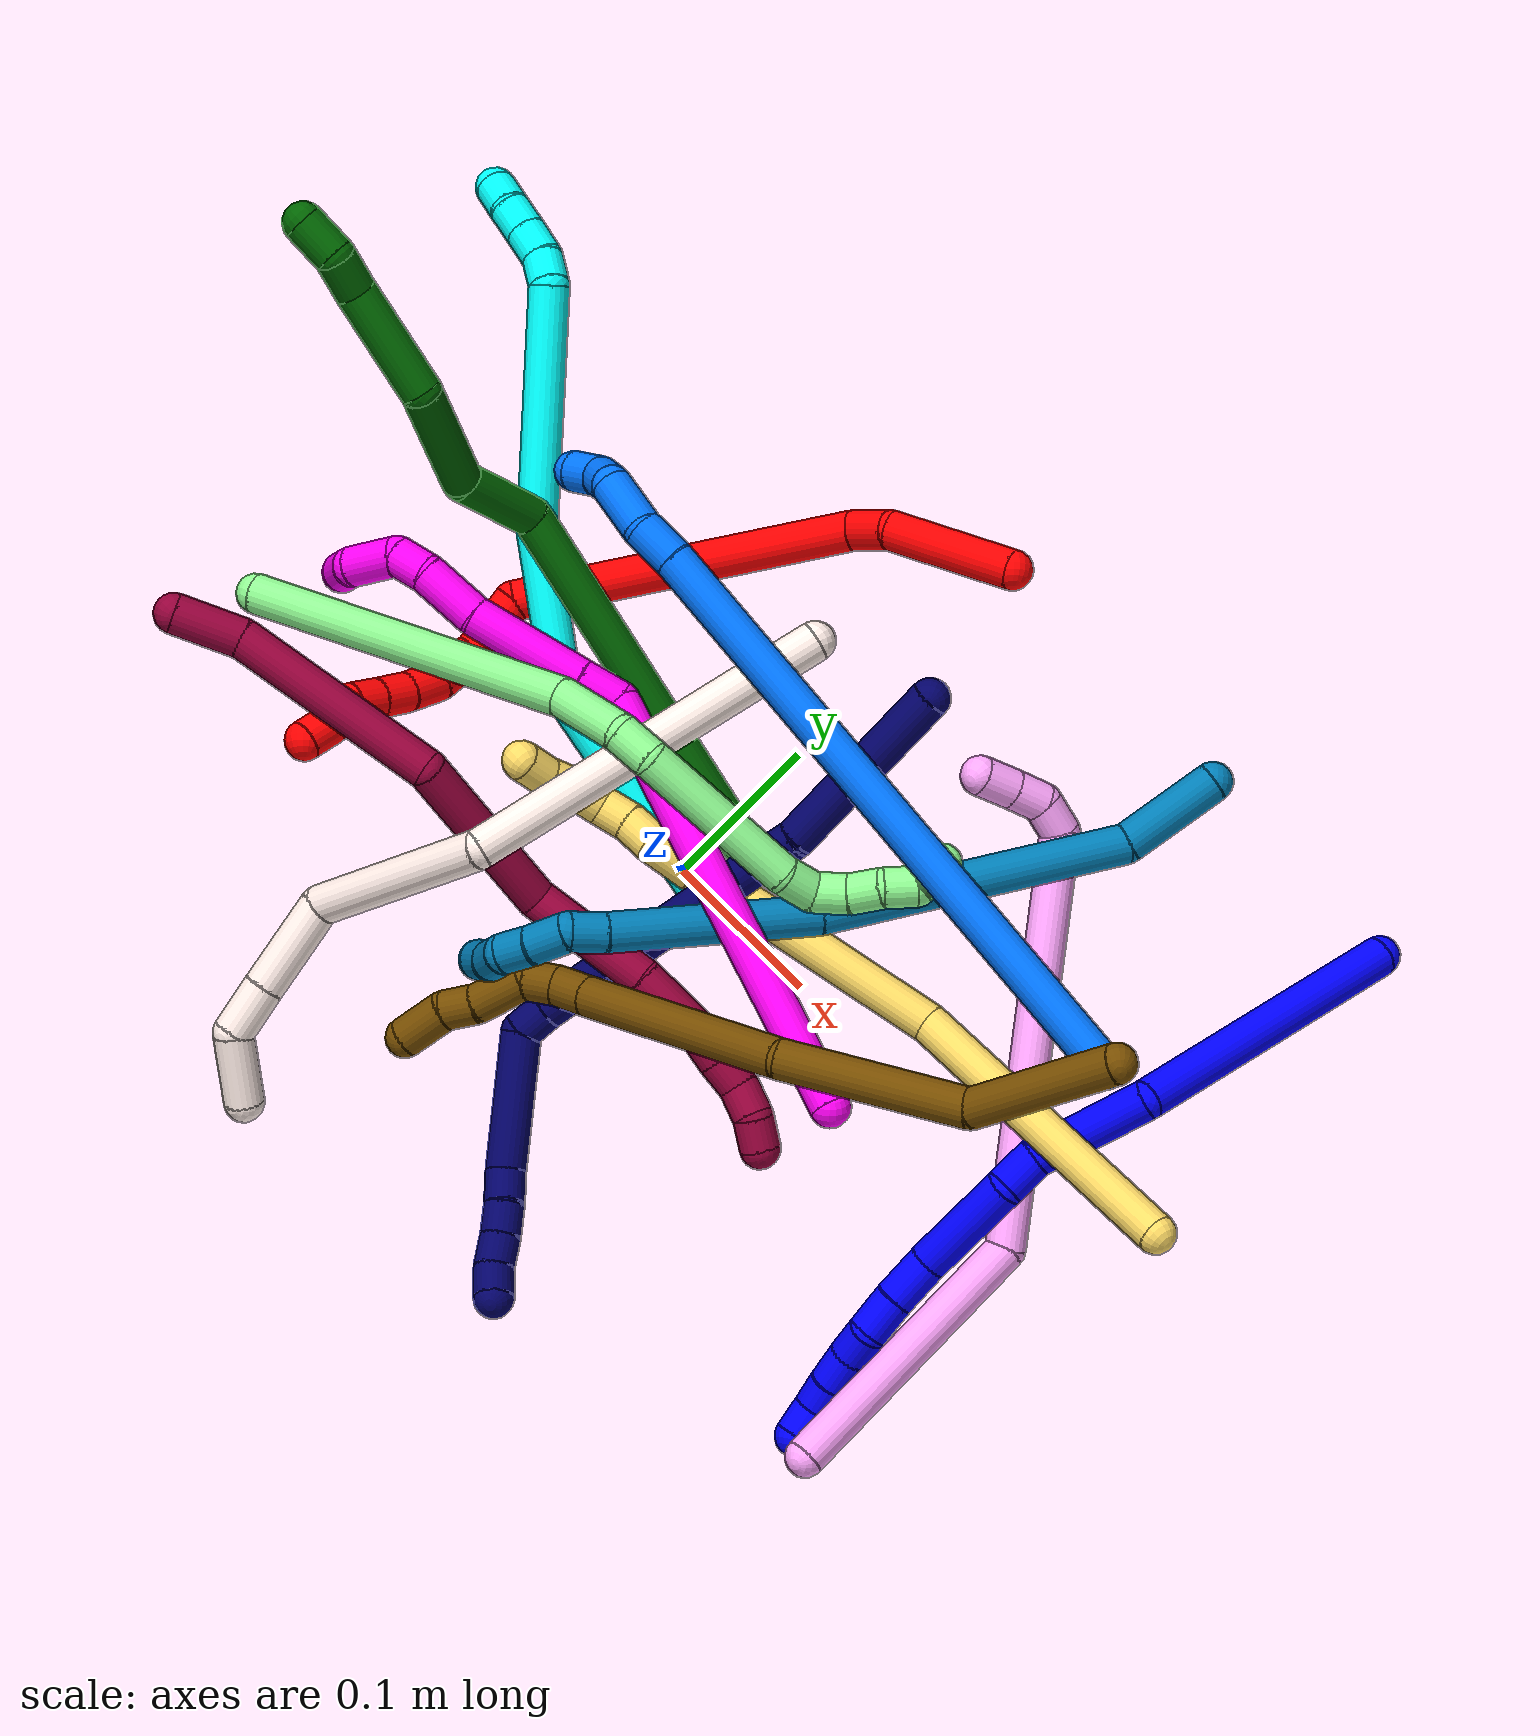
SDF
<sdf version="1.7">
 <world name="default">
  <plugin name="TubeGeneratorPlugin" filename="libtube_generator_plugin.so"/>
  <model name="photoneo_s_sensor">
   <static>1</static>
   <pose>0 0 2 1.57079 1.57079 3.14159</pose>
   <link name="link">
    <inertial><mass>0.1</mass></inertial>
    <sensor name="sensor" type="depth">
     <update_rate>30</update_rate>
     <camera>
      <horizontal_fov>1.22</horizontal_fov>
      <image><width>1920</width><height>1200</height><format>B8G8R8</format></image>
      <clip><near>0.1</near><far>4</far></clip>
      <depth_camera><output>points</output></depth_camera>
     </camera>
     <plugin name="camera_plugin" filename="libgazebo_ros_depth_camera.so">
      <baseline>0.2</baseline>
      <alwaysOn>1</alwaysOn>
      <updateRate>0.0</updateRate>
      <cameraName>camera_ir</cameraName>
      <imageTopicName>/camera/color/image_raw</imageTopicName>
      <cameraInfoTopicName>/camera/color/camera_info</cameraInfoTopicName>
      <depthImageTopicName>/camera/depth/image_raw</depthImageTopicName>
      <depthImageCameraInfoTopicName>/camera/depth/camera_info</depthImageCameraInfoTopicName>
      <pointCloudTopicName>/camera/depth/points</pointCloudTopicName>
      <frameName>fr_optical</frameName>
      <pointCloudCutoff>0.1</pointCloudCutoff>
      <pointCloudCutoffMax>2.0</pointCloudCutoffMax>
      <distortionK1>0</distortionK1>
      <distortionK2>0</distortionK2>
      <distortionK3>0</distortionK3>
      <distortionT1>0</distortionT1>
      <distortionT2>0</distortionT2>
      <CxPrime>0</CxPrime>
      <Cx>0</Cx>
      <Cy>0</Cy>
      <focalLength>0</focalLength>
      <hackBaseline>0</hackBaseline>
     </plugin>
    </sensor>
   </link>
  </model>
  <gravity>0 0 -9.8</gravity>
  <magnetic_field>6e-06 2.3e-05 -4.2e-05</magnetic_field>
  <atmosphere type="adiabatic"/>
  <physics name="default_physics" default="0" type="ode">
   <max_step_size>0.003</max_step_size>
   <real_time_factor>1</real_time_factor>
   <real_time_update_rate>1000</real_time_update_rate>
   <max_contacts>10000</max_contacts>
   <ode>
    <solver>
     <type>quick</type>
     <iters>100</iters>
     <sor>1.3</sor>
     <use_dynamic_moi_rescaling>0</use_dynamic_moi_rescaling>
    </solver>
    <constraints>
     <contact_max_correcting_vel>0</contact_max_correcting_vel>
     <contact_surface_layer>0.001</contact_surface_layer>
     <cfm>0</cfm>
     <erp>0.2</erp>
    </constraints>
   </ode>
  </physics>
  <scene><ambient>0.4 0.4 0.4 1</ambient><background>0.7 0.7 0.7 1</background><shadows>0</shadows></scene>
  <audio><device>default</device></audio>
  <spherical_coordinates>
   <surface_model>EARTH_WGS84</surface_model>
   <latitude_deg>0</latitude_deg>
   <longitude_deg>0</longitude_deg>
   <elevation>0</elevation>
   <heading_deg>0</heading_deg>
  </spherical_coordinates>
  <model name="bin">
   <static>1</static>
   <link name="bottom">
    <collision name="collision-bottom">
     <pose>0 0 -0.01 0 -0 0</pose>
     <geometry><box><size>0.8 0.6 0.02</size></box></geometry>
     <surface>
      <friction><ode><mu>100</mu><mu2>100</mu2></ode></friction>
      <contact><collide_bitmask>65535</collide_bitmask></contact>
     </surface>
    </collision>
   </link>
   <link name="west_wall">
    <collision name="collision-west_wall">
     <pose>-0.41 0 0.1 0 -0 0</pose>
     <geometry><box><size>0.02 0.6 0.2</size></box></geometry>
     <surface>
      <friction><ode><mu>100</mu><mu2>100</mu2></ode></friction>
      <contact><collide_bitmask>65535</collide_bitmask></contact>
     </surface>
    </collision>
   </link>
   <link name="east_wall">
    <collision name="collision-east_wall">
     <pose>0.41 0 0.1 0 -0 0</pose>
     <geometry><box><size>0.02 0.6 0.2</size></box></geometry>
     <surface>
      <friction><ode><mu>100</mu><mu2>100</mu2></ode></friction>
      <contact><collide_bitmask>65535</collide_bitmask></contact>
     </surface>
    </collision>
   </link>
   <link name="south_wall">
    <collision name="collision-south_wall">
     <pose>0 -0.31 0.1 0 -0 0</pose>
     <geometry><box><size>0.8 0.02 0.2</size></box></geometry>
     <surface>
      <friction><ode><mu>100</mu><mu2>100</mu2></ode></friction>
      <contact><collide_bitmask>65535</collide_bitmask></contact>
     </surface>
    </collision>
   </link>
   <link name="north_wall">
    <collision name="collision-north_wall">
     <pose>0 0.31 0.1 0 -0 0</pose>
     <geometry><box><size>0.8 0.02 0.2</size></box></geometry>
     <surface>
      <friction><ode><mu>100</mu><mu2>100</mu2></ode></friction>
      <contact><collide_bitmask>65535</collide_bitmask></contact>
     </surface>
    </collision>
   </link>
  </model>
  <model name="1">
   <static>0</static>
   <link name="1">
    <collision name="collision-cylinder-e_1_1_4">
     <pose>0.05638 -0.037189 -0.065543 2.62549 0.642316 1.80021</pose>
     <geometry><cylinder><radius>0.0125</radius><length>0.18823</length></cylinder></geometry>
     <surface>
      <friction><ode><mu>1.16</mu><mu2>1.16</mu2><slip1>0</slip1><slip2>0</slip2></ode></friction>
      <contact><ode><kp>1e+06</kp><kd>1</kd><max_vel>0</max_vel><min_depth>0.001</min_depth></ode></contact>
     </surface>
    </collision>
    <visual name="visual-cylinder-e_1_1_4">
     <pose>0.05638 -0.037189 -0.065543 2.62549 0.642316 1.80021</pose>
     <geometry><cylinder><radius>0.0125</radius><length>0.18823</length></cylinder></geometry>
     <material><ambient>0 0 1 1</ambient></material>
    </visual>
    <collision name="collision-cylinder-e_2_4_5">
     <pose>0.114122 -0.105321 -0.153749 2.20296 0.035507 0.069997</pose>
     <geometry><cylinder><radius>0.0125</radius><length>0.076755</length></cylinder></geometry>
     <surface>
      <friction><ode><mu>1.16</mu><mu2>1.16</mu2><slip1>0</slip1><slip2>0</slip2></ode></friction>
      <contact><ode><kp>1e+06</kp><kd>1</kd><max_vel>0</max_vel><min_depth>0.001</min_depth></ode></contact>
     </surface>
    </collision>
    <visual name="visual-cylinder-e_2_4_5">
     <pose>0.114122 -0.105321 -0.153749 2.20296 0.035507 0.069997</pose>
     <geometry><cylinder><radius>0.0125</radius><length>0.076755</length></cylinder></geometry>
     <material><ambient>0 0 1 1</ambient></material>
    </visual>
    <collision name="collision-cylinder-e_3_5_6">
     <pose>0.117973 -0.142558 -0.187363 2.61988 0.194553 0.700948</pose>
     <geometry><cylinder><radius>0.0125</radius><length>0.025749</length></cylinder></geometry>
     <surface>
      <friction><ode><mu>1.16</mu><mu2>1.16</mu2><slip1>0</slip1><slip2>0</slip2></ode></friction>
      <contact><ode><kp>1e+06</kp><kd>1</kd><max_vel>0</max_vel><min_depth>0.001</min_depth></ode></contact>
     </surface>
    </collision>
    <visual name="visual-cylinder-e_3_5_6">
     <pose>0.117973 -0.142558 -0.187363 2.61988 0.194553 0.700948</pose>
     <geometry><cylinder><radius>0.0125</radius><length>0.025749</length></cylinder></geometry>
     <material><ambient>0 0 1 1</ambient></material>
    </visual>
    <collision name="collision-cylinder-e_4_6_7">
     <pose>0.113312 -0.17193 -0.223152 2.39292 -0.207846 -0.518999</pose>
     <geometry><cylinder><radius>0.0125</radius><length>0.069299</length></cylinder></geometry>
     <surface>
      <friction><ode><mu>1.16</mu><mu2>1.16</mu2><slip1>0</slip1><slip2>0</slip2></ode></friction>
      <contact><ode><kp>1e+06</kp><kd>1</kd><max_vel>0</max_vel><min_depth>0.001</min_depth></ode></contact>
     </surface>
    </collision>
    <visual name="visual-cylinder-e_4_6_7">
     <pose>0.113312 -0.17193 -0.223152 2.39292 -0.207846 -0.518999</pose>
     <geometry><cylinder><radius>0.0125</radius><length>0.069299</length></cylinder></geometry>
     <material><ambient>0 0 1 1</ambient></material>
    </visual>
    <collision name="collision-cylinder-e_5_7_8">
     <pose>0.106541 -0.203095 -0.26092 2.58263 0.024795 0.086348</pose>
     <geometry><cylinder><radius>0.0125</radius><length>0.030513</length></cylinder></geometry>
     <surface>
      <friction><ode><mu>1.16</mu><mu2>1.16</mu2><slip1>0</slip1><slip2>0</slip2></ode></friction>
      <contact><ode><kp>1e+06</kp><kd>1</kd><max_vel>0</max_vel><min_depth>0.001</min_depth></ode></contact>
     </surface>
    </collision>
    <visual name="visual-cylinder-e_5_7_8">
     <pose>0.106541 -0.203095 -0.26092 2.58263 0.024795 0.086348</pose>
     <geometry><cylinder><radius>0.0125</radius><length>0.030513</length></cylinder></geometry>
     <material><ambient>0 0 1 1</ambient></material>
    </visual>
    <collision name="collision-cylinder-e_6_8_9">
     <pose>0.106536 -0.217521 -0.285051 2.62666 -0.029731 -0.1128</pose>
     <geometry><cylinder><radius>0.0125</radius><length>0.025749</length></cylinder></geometry>
     <surface>
      <friction><ode><mu>1.16</mu><mu2>1.16</mu2><slip1>0</slip1><slip2>0</slip2></ode></friction>
      <contact><ode><kp>1e+06</kp><kd>1</kd><max_vel>0</max_vel><min_depth>0.001</min_depth></ode></contact>
     </surface>
    </collision>
    <visual name="visual-cylinder-e_6_8_9">
     <pose>0.106536 -0.217521 -0.285051 2.62666 -0.029731 -0.1128</pose>
     <geometry><cylinder><radius>0.0125</radius><length>0.025749</length></cylinder></geometry>
     <material><ambient>0 0 1 1</ambient></material>
    </visual>
    <collision name="collision-cylinder-e_7_9_10">
     <pose>0.10222 -0.230234 -0.303656 2.43078 -0.382739 -0.962143</pose>
     <geometry><cylinder><radius>0.0125</radius><length>0.021066</length></cylinder></geometry>
     <surface>
      <friction><ode><mu>1.16</mu><mu2>1.16</mu2><slip1>0</slip1><slip2>0</slip2></ode></friction>
      <contact><ode><kp>1e+06</kp><kd>1</kd><max_vel>0</max_vel><min_depth>0.001</min_depth></ode></contact>
     </surface>
    </collision>
    <visual name="visual-cylinder-e_7_9_10">
     <pose>0.10222 -0.230234 -0.303656 2.43078 -0.382739 -0.962143</pose>
     <geometry><cylinder><radius>0.0125</radius><length>0.021066</length></cylinder></geometry>
     <material><ambient>0 0 1 1</ambient></material>
    </visual>
    <collision name="collision-cylinder-e_8_10_11">
     <pose>0.095186 -0.24257 -0.319888 2.54763 -0.283205 -0.871867</pose>
     <geometry><cylinder><radius>0.0125</radius><length>0.022188</length></cylinder></geometry>
     <surface>
      <friction><ode><mu>1.16</mu><mu2>1.16</mu2><slip1>0</slip1><slip2>0</slip2></ode></friction>
      <contact><ode><kp>1e+06</kp><kd>1</kd><max_vel>0</max_vel><min_depth>0.001</min_depth></ode></contact>
     </surface>
    </collision>
    <visual name="visual-cylinder-e_8_10_11">
     <pose>0.095186 -0.24257 -0.319888 2.54763 -0.283205 -0.871867</pose>
     <geometry><cylinder><radius>0.0125</radius><length>0.022188</length></cylinder></geometry>
     <material><ambient>0 0 1 1</ambient></material>
    </visual>
    <collision name="collision-cylinder-e_9_11_12">
     <pose>0.088803 -0.253685 -0.336683 2.56748 -0.33315 -1.03544</pose>
     <geometry><cylinder><radius>0.0125</radius><length>0.020081</length></cylinder></geometry>
     <surface>
      <friction><ode><mu>1.16</mu><mu2>1.16</mu2><slip1>0</slip1><slip2>0</slip2></ode></friction>
      <contact><ode><kp>1e+06</kp><kd>1</kd><max_vel>0</max_vel><min_depth>0.001</min_depth></ode></contact>
     </surface>
    </collision>
    <visual name="visual-cylinder-e_9_11_12">
     <pose>0.088803 -0.253685 -0.336683 2.56748 -0.33315 -1.03544</pose>
     <geometry><cylinder><radius>0.0125</radius><length>0.020081</length></cylinder></geometry>
     <material><ambient>0 0 1 1</ambient></material>
    </visual>
    <collision name="collision-cylinder-e_10_12_2">
     <pose>0.086436 -0.262387 -0.354152 2.78409 0.090113 0.4891</pose>
     <geometry><cylinder><radius>0.0125</radius><length>0.020369</length></cylinder></geometry>
     <surface>
      <friction><ode><mu>1.16</mu><mu2>1.16</mu2><slip1>0</slip1><slip2>0</slip2></ode></friction>
      <contact><ode><kp>1e+06</kp><kd>1</kd><max_vel>0</max_vel><min_depth>0.001</min_depth></ode></contact>
     </surface>
    </collision>
    <visual name="visual-cylinder-e_10_12_2">
     <pose>0.086436 -0.262387 -0.354152 2.78409 0.090113 0.4891</pose>
     <geometry><cylinder><radius>0.0125</radius><length>0.020369</length></cylinder></geometry>
     <material><ambient>0 0 1 1</ambient></material>
    </visual>
    <collision name="collision-sphere-2">
     <pose>0.087352 -0.265937 -0.363654 0 -0 0</pose>
     <geometry><sphere><radius>0.0125</radius></sphere></geometry>
     <surface>
      <friction><ode><mu>1.16</mu><mu2>1.16</mu2><slip1>0</slip1><slip2>0</slip2></ode></friction>
      <contact><ode><kp>1e+06</kp><kd>1</kd><max_vel>0</max_vel><min_depth>0.001</min_depth></ode></contact>
     </surface>
    </collision>
    <visual name="visual-sphere-2">
     <pose>0.087352 -0.265937 -0.363654 0 -0 0</pose>
     <geometry><sphere><radius>0.0125</radius></sphere></geometry>
     <material><ambient>0 0 1 1</ambient></material>
    </visual>
    <collision name="collision-sphere-12">
     <pose>0.085519 -0.258838 -0.34465 0 -0 0</pose>
     <geometry><sphere><radius>0.0125</radius></sphere></geometry>
     <surface>
      <friction><ode><mu>1.16</mu><mu2>1.16</mu2><slip1>0</slip1><slip2>0</slip2></ode></friction>
      <contact><ode><kp>1e+06</kp><kd>1</kd><max_vel>0</max_vel><min_depth>0.001</min_depth></ode></contact>
     </surface>
    </collision>
    <visual name="visual-sphere-12">
     <pose>0.085519 -0.258838 -0.34465 0 -0 0</pose>
     <geometry><sphere><radius>0.0125</radius></sphere></geometry>
     <material><ambient>0 0 1 1</ambient></material>
    </visual>
    <collision name="collision-sphere-11">
     <pose>0.092086 -0.248532 -0.328716 0 -0 0</pose>
     <geometry><sphere><radius>0.0125</radius></sphere></geometry>
     <surface>
      <friction><ode><mu>1.16</mu><mu2>1.16</mu2><slip1>0</slip1><slip2>0</slip2></ode></friction>
      <contact><ode><kp>1e+06</kp><kd>1</kd><max_vel>0</max_vel><min_depth>0.001</min_depth></ode></contact>
     </surface>
    </collision>
    <visual name="visual-sphere-11">
     <pose>0.092086 -0.248532 -0.328716 0 -0 0</pose>
     <geometry><sphere><radius>0.0125</radius></sphere></geometry>
     <material><ambient>0 0 1 1</ambient></material>
    </visual>
    <collision name="collision-sphere-10">
     <pose>0.098286 -0.236609 -0.311061 0 -0 0</pose>
     <geometry><sphere><radius>0.0125</radius></sphere></geometry>
     <surface>
      <friction><ode><mu>1.16</mu><mu2>1.16</mu2><slip1>0</slip1><slip2>0</slip2></ode></friction>
      <contact><ode><kp>1e+06</kp><kd>1</kd><max_vel>0</max_vel><min_depth>0.001</min_depth></ode></contact>
     </surface>
    </collision>
    <visual name="visual-sphere-10">
     <pose>0.098286 -0.236609 -0.311061 0 -0 0</pose>
     <geometry><sphere><radius>0.0125</radius></sphere></geometry>
     <material><ambient>0 0 1 1</ambient></material>
    </visual>
    <collision name="collision-sphere-9">
     <pose>0.106153 -0.223859 -0.296251 0 -0 0</pose>
     <geometry><sphere><radius>0.0125</radius></sphere></geometry>
     <surface>
      <friction><ode><mu>1.16</mu><mu2>1.16</mu2><slip1>0</slip1><slip2>0</slip2></ode></friction>
      <contact><ode><kp>1e+06</kp><kd>1</kd><max_vel>0</max_vel><min_depth>0.001</min_depth></ode></contact>
     </surface>
    </collision>
    <visual name="visual-sphere-9">
     <pose>0.106153 -0.223859 -0.296251 0 -0 0</pose>
     <geometry><sphere><radius>0.0125</radius></sphere></geometry>
     <material><ambient>0 0 1 1</ambient></material>
    </visual>
    <collision name="collision-sphere-4">
     <pose>0.11276 -0.074379 -0.131087 0 -0 0</pose>
     <geometry><sphere><radius>0.0125</radius></sphere></geometry>
     <surface>
      <friction><ode><mu>1.16</mu><mu2>1.16</mu2><slip1>0</slip1><slip2>0</slip2></ode></friction>
      <contact><ode><kp>1e+06</kp><kd>1</kd><max_vel>0</max_vel><min_depth>0.001</min_depth></ode></contact>
     </surface>
    </collision>
    <visual name="visual-sphere-4">
     <pose>0.11276 -0.074379 -0.131087 0 -0 0</pose>
     <geometry><sphere><radius>0.0125</radius></sphere></geometry>
     <material><ambient>0 0 1 1</ambient></material>
    </visual>
    <collision name="collision-sphere-1">
     <geometry><sphere><radius>0.0125</radius></sphere></geometry>
     <surface>
      <friction><ode><mu>1.16</mu><mu2>1.16</mu2><slip1>0</slip1><slip2>0</slip2></ode></friction>
      <contact><ode><kp>1e+06</kp><kd>1</kd><max_vel>0</max_vel><min_depth>0.001</min_depth></ode></contact>
     </surface>
    </collision>
    <visual name="visual-sphere-1">
     <geometry><sphere><radius>0.0125</radius></sphere></geometry>
     <material><ambient>0 0 1 1</ambient></material>
    </visual>
    <collision name="collision-sphere-8">
     <pose>0.106919 -0.211184 -0.273851 0 -0 0</pose>
     <geometry><sphere><radius>0.0125</radius></sphere></geometry>
     <surface>
      <friction><ode><mu>1.16</mu><mu2>1.16</mu2><slip1>0</slip1><slip2>0</slip2></ode></friction>
      <contact><ode><kp>1e+06</kp><kd>1</kd><max_vel>0</max_vel><min_depth>0.001</min_depth></ode></contact>
     </surface>
    </collision>
    <visual name="visual-sphere-8">
     <pose>0.106919 -0.211184 -0.273851 0 -0 0</pose>
     <geometry><sphere><radius>0.0125</radius></sphere></geometry>
     <material><ambient>0 0 1 1</ambient></material>
    </visual>
    <collision name="collision-sphere-5">
     <pose>0.115484 -0.136262 -0.176412 0 -0 0</pose>
     <geometry><sphere><radius>0.0125</radius></sphere></geometry>
     <surface>
      <friction><ode><mu>1.16</mu><mu2>1.16</mu2><slip1>0</slip1><slip2>0</slip2></ode></friction>
      <contact><ode><kp>1e+06</kp><kd>1</kd><max_vel>0</max_vel><min_depth>0.001</min_depth></ode></contact>
     </surface>
    </collision>
    <visual name="visual-sphere-5">
     <pose>0.115484 -0.136262 -0.176412 0 -0 0</pose>
     <geometry><sphere><radius>0.0125</radius></sphere></geometry>
     <material><ambient>0 0 1 1</ambient></material>
    </visual>
    <collision name="collision-sphere-6">
     <pose>0.120462 -0.148853 -0.198314 0 -0 0</pose>
     <geometry><sphere><radius>0.0125</radius></sphere></geometry>
     <surface>
      <friction><ode><mu>1.16</mu><mu2>1.16</mu2><slip1>0</slip1><slip2>0</slip2></ode></friction>
      <contact><ode><kp>1e+06</kp><kd>1</kd><max_vel>0</max_vel><min_depth>0.001</min_depth></ode></contact>
     </surface>
    </collision>
    <visual name="visual-sphere-6">
     <pose>0.120462 -0.148853 -0.198314 0 -0 0</pose>
     <geometry><sphere><radius>0.0125</radius></sphere></geometry>
     <material><ambient>0 0 1 1</ambient></material>
    </visual>
    <collision name="collision-sphere-7">
     <pose>0.106162 -0.195007 -0.247989 0 -0 0</pose>
     <geometry><sphere><radius>0.0125</radius></sphere></geometry>
     <surface>
      <friction><ode><mu>1.16</mu><mu2>1.16</mu2><slip1>0</slip1><slip2>0</slip2></ode></friction>
      <contact><ode><kp>1e+06</kp><kd>1</kd><max_vel>0</max_vel><min_depth>0.001</min_depth></ode></contact>
     </surface>
    </collision>
    <visual name="visual-sphere-7">
     <pose>0.106162 -0.195007 -0.247989 0 -0 0</pose>
     <geometry><sphere><radius>0.0125</radius></sphere></geometry>
     <material><ambient>0 0 1 1</ambient></material>
    </visual>
    <inertial>
     <pose>0.088131 -0.126277 -0.174395 0 -0 0</pose>
     <mass>0.5</mass>
     <inertia>
      <ixx>0.000408</ixx>
      <ixy>0</ixy>
      <ixz>0</ixz>
      <iyy>0.000628</iyy>
      <iyz>0</iyz>
      <izz>-7.7e-05</izz>
     </inertia>
    </inertial>
   </link>
   <pose>0.336672 0.261514 0.011496 1.89079 -1.01976 -2.88105</pose>
  </model>
  <model name="2">
   <static>0</static>
   <link name="2">
    <collision name="collision-cylinder-e_1_1_4">
     <pose>-0.031742 -0.020879 0.017692 0.867827 -0.859294 -0.41841</pose>
     <geometry><cylinder><radius>0.0125</radius><length>0.083821</length></cylinder></geometry>
     <surface>
      <friction><ode><mu>1.16</mu><mu2>1.16</mu2><slip1>0</slip1><slip2>0</slip2></ode></friction>
      <contact><ode><kp>1e+06</kp><kd>1</kd><max_vel>0</max_vel><min_depth>0.001</min_depth></ode></contact>
     </surface>
    </collision>
    <visual name="visual-cylinder-e_1_1_4">
     <pose>-0.031742 -0.020879 0.017692 0.867827 -0.859294 -0.41841</pose>
     <geometry><cylinder><radius>0.0125</radius><length>0.083821</length></cylinder></geometry>
     <material><ambient>1 0 0 1</ambient></material>
    </visual>
    <collision name="collision-cylinder-e_2_4_5">
     <pose>-0.078524 -0.044877 0.039244 0.679719 -1.25207 -0.500593</pose>
     <geometry><cylinder><radius>0.0125</radius><length>0.031674</length></cylinder></geometry>
     <surface>
      <friction><ode><mu>1.16</mu><mu2>1.16</mu2><slip1>0</slip1><slip2>0</slip2></ode></friction>
      <contact><ode><kp>1e+06</kp><kd>1</kd><max_vel>0</max_vel><min_depth>0.001</min_depth></ode></contact>
     </surface>
    </collision>
    <visual name="visual-cylinder-e_2_4_5">
     <pose>-0.078524 -0.044877 0.039244 0.679719 -1.25207 -0.500593</pose>
     <geometry><cylinder><radius>0.0125</radius><length>0.031674</length></cylinder></geometry>
     <material><ambient>1 0 0 1</ambient></material>
    </visual>
    <collision name="collision-cylinder-e_3_5_6">
     <pose>-0.161178 -0.126169 0.023517 1.8163 -0.698072 -0.872771</pose>
     <geometry><cylinder><radius>0.0125</radius><length>0.210394</length></cylinder></geometry>
     <surface>
      <friction><ode><mu>1.16</mu><mu2>1.16</mu2><slip1>0</slip1><slip2>0</slip2></ode></friction>
      <contact><ode><kp>1e+06</kp><kd>1</kd><max_vel>0</max_vel><min_depth>0.001</min_depth></ode></contact>
     </surface>
    </collision>
    <visual name="visual-cylinder-e_3_5_6">
     <pose>-0.161178 -0.126169 0.023517 1.8163 -0.698072 -0.872771</pose>
     <geometry><cylinder><radius>0.0125</radius><length>0.210394</length></cylinder></geometry>
     <material><ambient>1 0 0 1</ambient></material>
    </visual>
    <collision name="collision-cylinder-e_4_6_7">
     <pose>-0.239419 -0.211247 -0.010815 2.70367 -0.578225 -1.85699</pose>
     <geometry><cylinder><radius>0.0125</radius><length>0.038884</length></cylinder></geometry>
     <surface>
      <friction><ode><mu>1.16</mu><mu2>1.16</mu2><slip1>0</slip1><slip2>0</slip2></ode></friction>
      <contact><ode><kp>1e+06</kp><kd>1</kd><max_vel>0</max_vel><min_depth>0.001</min_depth></ode></contact>
     </surface>
    </collision>
    <visual name="visual-cylinder-e_4_6_7">
     <pose>-0.239419 -0.211247 -0.010815 2.70367 -0.578225 -1.85699</pose>
     <geometry><cylinder><radius>0.0125</radius><length>0.038884</length></cylinder></geometry>
     <material><ambient>1 0 0 1</ambient></material>
    </visual>
    <collision name="collision-cylinder-e_5_7_8">
     <pose>-0.256734 -0.226708 -0.034839 2.39667 -0.487305 -1.13334</pose>
     <geometry><cylinder><radius>0.0125</radius><length>0.02857</length></cylinder></geometry>
     <surface>
      <friction><ode><mu>1.16</mu><mu2>1.16</mu2><slip1>0</slip1><slip2>0</slip2></ode></friction>
      <contact><ode><kp>1e+06</kp><kd>1</kd><max_vel>0</max_vel><min_depth>0.001</min_depth></ode></contact>
     </surface>
    </collision>
    <visual name="visual-cylinder-e_5_7_8">
     <pose>-0.256734 -0.226708 -0.034839 2.39667 -0.487305 -1.13334</pose>
     <geometry><cylinder><radius>0.0125</radius><length>0.02857</length></cylinder></geometry>
     <material><ambient>1 0 0 1</ambient></material>
    </visual>
    <collision name="collision-cylinder-e_6_8_9">
     <pose>-0.26457 -0.24627 -0.049719 2.04156 -0.092674 -0.150971</pose>
     <geometry><cylinder><radius>0.0125</radius><length>0.024804</length></cylinder></geometry>
     <surface>
      <friction><ode><mu>1.16</mu><mu2>1.16</mu2><slip1>0</slip1><slip2>0</slip2></ode></friction>
      <contact><ode><kp>1e+06</kp><kd>1</kd><max_vel>0</max_vel><min_depth>0.001</min_depth></ode></contact>
     </surface>
    </collision>
    <visual name="visual-cylinder-e_6_8_9">
     <pose>-0.26457 -0.24627 -0.049719 2.04156 -0.092674 -0.150971</pose>
     <geometry><cylinder><radius>0.0125</radius><length>0.024804</length></cylinder></geometry>
     <material><ambient>1 0 0 1</ambient></material>
    </visual>
    <collision name="collision-cylinder-e_7_9_10">
     <pose>-0.266473 -0.267248 -0.059066 1.93013 -0.070788 -0.102163</pose>
     <geometry><cylinder><radius>0.0125</radius><length>0.021358</length></cylinder></geometry>
     <surface>
      <friction><ode><mu>1.16</mu><mu2>1.16</mu2><slip1>0</slip1><slip2>0</slip2></ode></friction>
      <contact><ode><kp>1e+06</kp><kd>1</kd><max_vel>0</max_vel><min_depth>0.001</min_depth></ode></contact>
     </surface>
    </collision>
    <visual name="visual-cylinder-e_7_9_10">
     <pose>-0.266473 -0.267248 -0.059066 1.93013 -0.070788 -0.102163</pose>
     <geometry><cylinder><radius>0.0125</radius><length>0.021358</length></cylinder></geometry>
     <material><ambient>1 0 0 1</ambient></material>
    </visual>
    <collision name="collision-cylinder-e_8_10_11">
     <pose>-0.267376 -0.286754 -0.06627 1.9187 -0.014569 -0.020781</pose>
     <geometry><cylinder><radius>0.0125</radius><length>0.020286</length></cylinder></geometry>
     <surface>
      <friction><ode><mu>1.16</mu><mu2>1.16</mu2><slip1>0</slip1><slip2>0</slip2></ode></friction>
      <contact><ode><kp>1e+06</kp><kd>1</kd><max_vel>0</max_vel><min_depth>0.001</min_depth></ode></contact>
     </surface>
    </collision>
    <visual name="visual-cylinder-e_8_10_11">
     <pose>-0.267376 -0.286754 -0.06627 1.9187 -0.014569 -0.020781</pose>
     <geometry><cylinder><radius>0.0125</radius><length>0.020286</length></cylinder></geometry>
     <material><ambient>1 0 0 1</ambient></material>
    </visual>
    <collision name="collision-cylinder-e_9_11_12">
     <pose>-0.268238 -0.302738 -0.077357 2.43983 -0.071389 -0.194504</pose>
     <geometry><cylinder><radius>0.0125</radius><length>0.020032</length></cylinder></geometry>
     <surface>
      <friction><ode><mu>1.16</mu><mu2>1.16</mu2><slip1>0</slip1><slip2>0</slip2></ode></friction>
      <contact><ode><kp>1e+06</kp><kd>1</kd><max_vel>0</max_vel><min_depth>0.001</min_depth></ode></contact>
     </surface>
    </collision>
    <visual name="visual-cylinder-e_9_11_12">
     <pose>-0.268238 -0.302738 -0.077357 2.43983 -0.071389 -0.194504</pose>
     <geometry><cylinder><radius>0.0125</radius><length>0.020032</length></cylinder></geometry>
     <material><ambient>1 0 0 1</ambient></material>
    </visual>
    <collision name="collision-cylinder-e_10_12_2">
     <pose>-0.271558 -0.316816 -0.091052 2.24244 -0.261229 -0.531587</pose>
     <geometry><cylinder><radius>0.0125</radius><length>0.020175</length></cylinder></geometry>
     <surface>
      <friction><ode><mu>1.16</mu><mu2>1.16</mu2><slip1>0</slip1><slip2>0</slip2></ode></friction>
      <contact><ode><kp>1e+06</kp><kd>1</kd><max_vel>0</max_vel><min_depth>0.001</min_depth></ode></contact>
     </surface>
    </collision>
    <visual name="visual-cylinder-e_10_12_2">
     <pose>-0.271558 -0.316816 -0.091052 2.24244 -0.261229 -0.531587</pose>
     <geometry><cylinder><radius>0.0125</radius><length>0.020175</length></cylinder></geometry>
     <material><ambient>1 0 0 1</ambient></material>
    </visual>
    <collision name="collision-sphere-2">
     <pose>-0.274164 -0.324445 -0.097116 0 -0 0</pose>
     <geometry><sphere><radius>0.0125</radius></sphere></geometry>
     <surface>
      <friction><ode><mu>1.16</mu><mu2>1.16</mu2><slip1>0</slip1><slip2>0</slip2></ode></friction>
      <contact><ode><kp>1e+06</kp><kd>1</kd><max_vel>0</max_vel><min_depth>0.001</min_depth></ode></contact>
     </surface>
    </collision>
    <visual name="visual-sphere-2">
     <pose>-0.274164 -0.324445 -0.097116 0 -0 0</pose>
     <geometry><sphere><radius>0.0125</radius></sphere></geometry>
     <material><ambient>1 0 0 1</ambient></material>
    </visual>
    <collision name="collision-sphere-12">
     <pose>-0.268953 -0.309188 -0.084987 0 -0 0</pose>
     <geometry><sphere><radius>0.0125</radius></sphere></geometry>
     <surface>
      <friction><ode><mu>1.16</mu><mu2>1.16</mu2><slip1>0</slip1><slip2>0</slip2></ode></friction>
      <contact><ode><kp>1e+06</kp><kd>1</kd><max_vel>0</max_vel><min_depth>0.001</min_depth></ode></contact>
     </surface>
    </collision>
    <visual name="visual-sphere-12">
     <pose>-0.268953 -0.309188 -0.084987 0 -0 0</pose>
     <geometry><sphere><radius>0.0125</radius></sphere></geometry>
     <material><ambient>1 0 0 1</ambient></material>
    </visual>
    <collision name="collision-sphere-11">
     <pose>-0.267524 -0.296289 -0.069728 0 -0 0</pose>
     <geometry><sphere><radius>0.0125</radius></sphere></geometry>
     <surface>
      <friction><ode><mu>1.16</mu><mu2>1.16</mu2><slip1>0</slip1><slip2>0</slip2></ode></friction>
      <contact><ode><kp>1e+06</kp><kd>1</kd><max_vel>0</max_vel><min_depth>0.001</min_depth></ode></contact>
     </surface>
    </collision>
    <visual name="visual-sphere-11">
     <pose>-0.267524 -0.296289 -0.069728 0 -0 0</pose>
     <geometry><sphere><radius>0.0125</radius></sphere></geometry>
     <material><ambient>1 0 0 1</ambient></material>
    </visual>
    <collision name="collision-sphere-10">
     <pose>-0.267229 -0.27722 -0.062812 0 -0 0</pose>
     <geometry><sphere><radius>0.0125</radius></sphere></geometry>
     <surface>
      <friction><ode><mu>1.16</mu><mu2>1.16</mu2><slip1>0</slip1><slip2>0</slip2></ode></friction>
      <contact><ode><kp>1e+06</kp><kd>1</kd><max_vel>0</max_vel><min_depth>0.001</min_depth></ode></contact>
     </surface>
    </collision>
    <visual name="visual-sphere-10">
     <pose>-0.267229 -0.27722 -0.062812 0 -0 0</pose>
     <geometry><sphere><radius>0.0125</radius></sphere></geometry>
     <material><ambient>1 0 0 1</ambient></material>
    </visual>
    <collision name="collision-sphere-9">
     <pose>-0.265718 -0.257276 -0.05532 0 -0 0</pose>
     <geometry><sphere><radius>0.0125</radius></sphere></geometry>
     <surface>
      <friction><ode><mu>1.16</mu><mu2>1.16</mu2><slip1>0</slip1><slip2>0</slip2></ode></friction>
      <contact><ode><kp>1e+06</kp><kd>1</kd><max_vel>0</max_vel><min_depth>0.001</min_depth></ode></contact>
     </surface>
    </collision>
    <visual name="visual-sphere-9">
     <pose>-0.265718 -0.257276 -0.05532 0 -0 0</pose>
     <geometry><sphere><radius>0.0125</radius></sphere></geometry>
     <material><ambient>1 0 0 1</ambient></material>
    </visual>
    <collision name="collision-sphere-4">
     <pose>-0.063485 -0.041757 0.035384 0 -0 0</pose>
     <geometry><sphere><radius>0.0125</radius></sphere></geometry>
     <surface>
      <friction><ode><mu>1.16</mu><mu2>1.16</mu2><slip1>0</slip1><slip2>0</slip2></ode></friction>
      <contact><ode><kp>1e+06</kp><kd>1</kd><max_vel>0</max_vel><min_depth>0.001</min_depth></ode></contact>
     </surface>
    </collision>
    <visual name="visual-sphere-4">
     <pose>-0.063485 -0.041757 0.035384 0 -0 0</pose>
     <geometry><sphere><radius>0.0125</radius></sphere></geometry>
     <material><ambient>1 0 0 1</ambient></material>
    </visual>
    <collision name="collision-sphere-1">
     <geometry><sphere><radius>0.0125</radius></sphere></geometry>
     <surface>
      <friction><ode><mu>1.16</mu><mu2>1.16</mu2><slip1>0</slip1><slip2>0</slip2></ode></friction>
      <contact><ode><kp>1e+06</kp><kd>1</kd><max_vel>0</max_vel><min_depth>0.001</min_depth></ode></contact>
     </surface>
    </collision>
    <visual name="visual-sphere-1">
     <geometry><sphere><radius>0.0125</radius></sphere></geometry>
     <material><ambient>1 0 0 1</ambient></material>
    </visual>
    <collision name="collision-sphere-8">
     <pose>-0.263422 -0.235265 -0.044118 0 -0 0</pose>
     <geometry><sphere><radius>0.0125</radius></sphere></geometry>
     <surface>
      <friction><ode><mu>1.16</mu><mu2>1.16</mu2><slip1>0</slip1><slip2>0</slip2></ode></friction>
      <contact><ode><kp>1e+06</kp><kd>1</kd><max_vel>0</max_vel><min_depth>0.001</min_depth></ode></contact>
     </surface>
    </collision>
    <visual name="visual-sphere-8">
     <pose>-0.263422 -0.235265 -0.044118 0 -0 0</pose>
     <geometry><sphere><radius>0.0125</radius></sphere></geometry>
     <material><ambient>1 0 0 1</ambient></material>
    </visual>
    <collision name="collision-sphere-5">
     <pose>-0.093564 -0.047996 0.043104 0 -0 0</pose>
     <geometry><sphere><radius>0.0125</radius></sphere></geometry>
     <surface>
      <friction><ode><mu>1.16</mu><mu2>1.16</mu2><slip1>0</slip1><slip2>0</slip2></ode></friction>
      <contact><ode><kp>1e+06</kp><kd>1</kd><max_vel>0</max_vel><min_depth>0.001</min_depth></ode></contact>
     </surface>
    </collision>
    <visual name="visual-sphere-5">
     <pose>-0.093564 -0.047996 0.043104 0 -0 0</pose>
     <geometry><sphere><radius>0.0125</radius></sphere></geometry>
     <material><ambient>1 0 0 1</ambient></material>
    </visual>
    <collision name="collision-sphere-6">
     <pose>-0.228793 -0.204343 0.00393 0 -0 0</pose>
     <geometry><sphere><radius>0.0125</radius></sphere></geometry>
     <surface>
      <friction><ode><mu>1.16</mu><mu2>1.16</mu2><slip1>0</slip1><slip2>0</slip2></ode></friction>
      <contact><ode><kp>1e+06</kp><kd>1</kd><max_vel>0</max_vel><min_depth>0.001</min_depth></ode></contact>
     </surface>
    </collision>
    <visual name="visual-sphere-6">
     <pose>-0.228793 -0.204343 0.00393 0 -0 0</pose>
     <geometry><sphere><radius>0.0125</radius></sphere></geometry>
     <material><ambient>1 0 0 1</ambient></material>
    </visual>
    <collision name="collision-sphere-7">
     <pose>-0.250045 -0.218151 -0.02556 0 -0 0</pose>
     <geometry><sphere><radius>0.0125</radius></sphere></geometry>
     <surface>
      <friction><ode><mu>1.16</mu><mu2>1.16</mu2><slip1>0</slip1><slip2>0</slip2></ode></friction>
      <contact><ode><kp>1e+06</kp><kd>1</kd><max_vel>0</max_vel><min_depth>0.001</min_depth></ode></contact>
     </surface>
    </collision>
    <visual name="visual-sphere-7">
     <pose>-0.250045 -0.218151 -0.02556 0 -0 0</pose>
     <geometry><sphere><radius>0.0125</radius></sphere></geometry>
     <material><ambient>1 0 0 1</ambient></material>
    </visual>
    <inertial>
     <pose>-0.168467 -0.148996 -0.001936 0 -0 0</pose>
     <mass>0.5</mass>
     <inertia>
      <ixx>-7.9e-05</ixx>
      <ixy>0</ixy>
      <ixz>0</ixz>
      <iyy>-0.000211</iyy>
      <iyz>0</iyz>
      <izz>0.001166</izz>
     </inertia>
    </inertial>
   </link>
   <pose>0.014621 0.266725 0.065844 -1.99662 -0.864245 1.12563</pose>
  </model>
  <model name="3">
   <static>0</static>
   <link name="3">
    <collision name="collision-cylinder-e_1_1_4">
     <pose>0.003706 -0.002853 0.010705 0.260473 0.322814 0.042646</pose>
     <geometry><cylinder><radius>0.0125</radius><length>0.023364</length></cylinder></geometry>
     <surface>
      <friction><ode><mu>1.16</mu><mu2>1.16</mu2><slip1>0</slip1><slip2>0</slip2></ode></friction>
      <contact><ode><kp>1e+06</kp><kd>1</kd><max_vel>0</max_vel><min_depth>0.001</min_depth></ode></contact>
     </surface>
    </collision>
    <visual name="visual-cylinder-e_1_1_4">
     <pose>0.003706 -0.002853 0.010705 0.260473 0.322814 0.042646</pose>
     <geometry><cylinder><radius>0.0125</radius><length>0.023364</length></cylinder></geometry>
     <material><ambient>0.003922 1 0.996078 1</ambient></material>
    </visual>
    <collision name="collision-cylinder-e_2_4_5">
     <pose>-0.002954 0.006583 0.09408 -0.167521 -0.13973 0.01175</pose>
     <geometry><cylinder><radius>0.0125</radius><length>0.148854</length></cylinder></geometry>
     <surface>
      <friction><ode><mu>1.16</mu><mu2>1.16</mu2><slip1>0</slip1><slip2>0</slip2></ode></friction>
      <contact><ode><kp>1e+06</kp><kd>1</kd><max_vel>0</max_vel><min_depth>0.001</min_depth></ode></contact>
     </surface>
    </collision>
    <visual name="visual-cylinder-e_2_4_5">
     <pose>-0.002954 0.006583 0.09408 -0.167521 -0.13973 0.01175</pose>
     <geometry><cylinder><radius>0.0125</radius><length>0.148854</length></cylinder></geometry>
     <material><ambient>0.003922 1 0.996078 1</ambient></material>
    </visual>
    <collision name="collision-cylinder-e_3_5_6">
     <pose>-0.039246 0.031713 0.206046 -0.315835 -0.560122 0.091539</pose>
     <geometry><cylinder><radius>0.0125</radius><length>0.097596</length></cylinder></geometry>
     <surface>
      <friction><ode><mu>1.16</mu><mu2>1.16</mu2><slip1>0</slip1><slip2>0</slip2></ode></friction>
      <contact><ode><kp>1e+06</kp><kd>1</kd><max_vel>0</max_vel><min_depth>0.001</min_depth></ode></contact>
     </surface>
    </collision>
    <visual name="visual-cylinder-e_3_5_6">
     <pose>-0.039246 0.031713 0.206046 -0.315835 -0.560122 0.091539</pose>
     <geometry><cylinder><radius>0.0125</radius><length>0.097596</length></cylinder></geometry>
     <material><ambient>0.003922 1 0.996078 1</ambient></material>
    </visual>
    <collision name="collision-cylinder-e_4_6_7">
     <pose>-0.114657 0.070023 0.294694 -0.476424 -0.727842 0.184451</pose>
     <geometry><cylinder><radius>0.0125</radius><length>0.148769</length></cylinder></geometry>
     <surface>
      <friction><ode><mu>1.16</mu><mu2>1.16</mu2><slip1>0</slip1><slip2>0</slip2></ode></friction>
      <contact><ode><kp>1e+06</kp><kd>1</kd><max_vel>0</max_vel><min_depth>0.001</min_depth></ode></contact>
     </surface>
    </collision>
    <visual name="visual-cylinder-e_4_6_7">
     <pose>-0.114657 0.070023 0.294694 -0.476424 -0.727842 0.184451</pose>
     <geometry><cylinder><radius>0.0125</radius><length>0.148769</length></cylinder></geometry>
     <material><ambient>0.003922 1 0.996078 1</ambient></material>
    </visual>
    <collision name="collision-cylinder-e_5_7_8">
     <pose>-0.170047 0.093233 0.35186 0.28144 -0.62797 -0.091934</pose>
     <geometry><cylinder><radius>0.0125</radius><length>0.020103</length></cylinder></geometry>
     <surface>
      <friction><ode><mu>1.16</mu><mu2>1.16</mu2><slip1>0</slip1><slip2>0</slip2></ode></friction>
      <contact><ode><kp>1e+06</kp><kd>1</kd><max_vel>0</max_vel><min_depth>0.001</min_depth></ode></contact>
     </surface>
    </collision>
    <visual name="visual-cylinder-e_5_7_8">
     <pose>-0.170047 0.093233 0.35186 0.28144 -0.62797 -0.091934</pose>
     <geometry><cylinder><radius>0.0125</radius><length>0.020103</length></cylinder></geometry>
     <material><ambient>0.003922 1 0.996078 1</ambient></material>
    </visual>
    <collision name="collision-cylinder-e_6_8_9">
     <pose>-0.179395 0.087767 0.369006 0.331015 -0.335673 -0.056587</pose>
     <geometry><cylinder><radius>0.0125</radius><length>0.020903</length></cylinder></geometry>
     <surface>
      <friction><ode><mu>1.16</mu><mu2>1.16</mu2><slip1>0</slip1><slip2>0</slip2></ode></friction>
      <contact><ode><kp>1e+06</kp><kd>1</kd><max_vel>0</max_vel><min_depth>0.001</min_depth></ode></contact>
     </surface>
    </collision>
    <visual name="visual-cylinder-e_6_8_9">
     <pose>-0.179395 0.087767 0.369006 0.331015 -0.335673 -0.056587</pose>
     <geometry><cylinder><radius>0.0125</radius><length>0.020903</length></cylinder></geometry>
     <material><ambient>0.003922 1 0.996078 1</ambient></material>
    </visual>
    <collision name="collision-cylinder-e_7_9_10">
     <pose>-0.185909 0.081615 0.387534 0.309885 -0.307917 -0.048469</pose>
     <geometry><cylinder><radius>0.0125</radius><length>0.020265</length></cylinder></geometry>
     <surface>
      <friction><ode><mu>1.16</mu><mu2>1.16</mu2><slip1>0</slip1><slip2>0</slip2></ode></friction>
      <contact><ode><kp>1e+06</kp><kd>1</kd><max_vel>0</max_vel><min_depth>0.001</min_depth></ode></contact>
     </surface>
    </collision>
    <visual name="visual-cylinder-e_7_9_10">
     <pose>-0.185909 0.081615 0.387534 0.309885 -0.307917 -0.048469</pose>
     <geometry><cylinder><radius>0.0125</radius><length>0.020265</length></cylinder></geometry>
     <material><ambient>0.003922 1 0.996078 1</ambient></material>
    </visual>
    <collision name="collision-cylinder-e_8_10_2">
     <pose>-0.192683 0.073928 0.404809 0.530808 -0.376507 -0.103475</pose>
     <geometry><cylinder><radius>0.0125</radius><length>0.020147</length></cylinder></geometry>
     <surface>
      <friction><ode><mu>1.16</mu><mu2>1.16</mu2><slip1>0</slip1><slip2>0</slip2></ode></friction>
      <contact><ode><kp>1e+06</kp><kd>1</kd><max_vel>0</max_vel><min_depth>0.001</min_depth></ode></contact>
     </surface>
    </collision>
    <visual name="visual-cylinder-e_8_10_2">
     <pose>-0.192683 0.073928 0.404809 0.530808 -0.376507 -0.103475</pose>
     <geometry><cylinder><radius>0.0125</radius><length>0.020147</length></cylinder></geometry>
     <material><ambient>0.003922 1 0.996078 1</ambient></material>
    </visual>
    <collision name="collision-sphere-2">
     <pose>-0.196387 0.069186 0.412888 0 -0 0</pose>
     <geometry><sphere><radius>0.0125</radius></sphere></geometry>
     <surface>
      <friction><ode><mu>1.16</mu><mu2>1.16</mu2><slip1>0</slip1><slip2>0</slip2></ode></friction>
      <contact><ode><kp>1e+06</kp><kd>1</kd><max_vel>0</max_vel><min_depth>0.001</min_depth></ode></contact>
     </surface>
    </collision>
    <visual name="visual-sphere-2">
     <pose>-0.196387 0.069186 0.412888 0 -0 0</pose>
     <geometry><sphere><radius>0.0125</radius></sphere></geometry>
     <material><ambient>0.003922 1 0.996078 1</ambient></material>
    </visual>
    <collision name="collision-sphere-10">
     <pose>-0.188979 0.07867 0.39673 0 -0 0</pose>
     <geometry><sphere><radius>0.0125</radius></sphere></geometry>
     <surface>
      <friction><ode><mu>1.16</mu><mu2>1.16</mu2><slip1>0</slip1><slip2>0</slip2></ode></friction>
      <contact><ode><kp>1e+06</kp><kd>1</kd><max_vel>0</max_vel><min_depth>0.001</min_depth></ode></contact>
     </surface>
    </collision>
    <visual name="visual-sphere-10">
     <pose>-0.188979 0.07867 0.39673 0 -0 0</pose>
     <geometry><sphere><radius>0.0125</radius></sphere></geometry>
     <material><ambient>0.003922 1 0.996078 1</ambient></material>
    </visual>
    <collision name="collision-sphere-9">
     <pose>-0.182838 0.084559 0.378339 0 -0 0</pose>
     <geometry><sphere><radius>0.0125</radius></sphere></geometry>
     <surface>
      <friction><ode><mu>1.16</mu><mu2>1.16</mu2><slip1>0</slip1><slip2>0</slip2></ode></friction>
      <contact><ode><kp>1e+06</kp><kd>1</kd><max_vel>0</max_vel><min_depth>0.001</min_depth></ode></contact>
     </surface>
    </collision>
    <visual name="visual-sphere-9">
     <pose>-0.182838 0.084559 0.378339 0 -0 0</pose>
     <geometry><sphere><radius>0.0125</radius></sphere></geometry>
     <material><ambient>0.003922 1 0.996078 1</ambient></material>
    </visual>
    <collision name="collision-sphere-4">
     <pose>0.007412 -0.005706 0.02141 0 -0 0</pose>
     <geometry><sphere><radius>0.0125</radius></sphere></geometry>
     <surface>
      <friction><ode><mu>1.16</mu><mu2>1.16</mu2><slip1>0</slip1><slip2>0</slip2></ode></friction>
      <contact><ode><kp>1e+06</kp><kd>1</kd><max_vel>0</max_vel><min_depth>0.001</min_depth></ode></contact>
     </surface>
    </collision>
    <visual name="visual-sphere-4">
     <pose>0.007412 -0.005706 0.02141 0 -0 0</pose>
     <geometry><sphere><radius>0.0125</radius></sphere></geometry>
     <material><ambient>0.003922 1 0.996078 1</ambient></material>
    </visual>
    <collision name="collision-sphere-1">
     <geometry><sphere><radius>0.0125</radius></sphere></geometry>
     <surface>
      <friction><ode><mu>1.16</mu><mu2>1.16</mu2><slip1>0</slip1><slip2>0</slip2></ode></friction>
      <contact><ode><kp>1e+06</kp><kd>1</kd><max_vel>0</max_vel><min_depth>0.001</min_depth></ode></contact>
     </surface>
    </collision>
    <visual name="visual-sphere-1">
     <geometry><sphere><radius>0.0125</radius></sphere></geometry>
     <material><ambient>0.003922 1 0.996078 1</ambient></material>
    </visual>
    <collision name="collision-sphere-8">
     <pose>-0.175952 0.090974 0.359673 0 -0 0</pose>
     <geometry><sphere><radius>0.0125</radius></sphere></geometry>
     <surface>
      <friction><ode><mu>1.16</mu><mu2>1.16</mu2><slip1>0</slip1><slip2>0</slip2></ode></friction>
      <contact><ode><kp>1e+06</kp><kd>1</kd><max_vel>0</max_vel><min_depth>0.001</min_depth></ode></contact>
     </surface>
    </collision>
    <visual name="visual-sphere-8">
     <pose>-0.175952 0.090974 0.359673 0 -0 0</pose>
     <geometry><sphere><radius>0.0125</radius></sphere></geometry>
     <material><ambient>0.003922 1 0.996078 1</ambient></material>
    </visual>
    <collision name="collision-sphere-5">
     <pose>-0.01332 0.018871 0.166749 0 -0 0</pose>
     <geometry><sphere><radius>0.0125</radius></sphere></geometry>
     <surface>
      <friction><ode><mu>1.16</mu><mu2>1.16</mu2><slip1>0</slip1><slip2>0</slip2></ode></friction>
      <contact><ode><kp>1e+06</kp><kd>1</kd><max_vel>0</max_vel><min_depth>0.001</min_depth></ode></contact>
     </surface>
    </collision>
    <visual name="visual-sphere-5">
     <pose>-0.01332 0.018871 0.166749 0 -0 0</pose>
     <geometry><sphere><radius>0.0125</radius></sphere></geometry>
     <material><ambient>0.003922 1 0.996078 1</ambient></material>
    </visual>
    <collision name="collision-sphere-6">
     <pose>-0.065172 0.044554 0.245342 0 -0 0</pose>
     <geometry><sphere><radius>0.0125</radius></sphere></geometry>
     <surface>
      <friction><ode><mu>1.16</mu><mu2>1.16</mu2><slip1>0</slip1><slip2>0</slip2></ode></friction>
      <contact><ode><kp>1e+06</kp><kd>1</kd><max_vel>0</max_vel><min_depth>0.001</min_depth></ode></contact>
     </surface>
    </collision>
    <visual name="visual-sphere-6">
     <pose>-0.065172 0.044554 0.245342 0 -0 0</pose>
     <geometry><sphere><radius>0.0125</radius></sphere></geometry>
     <material><ambient>0.003922 1 0.996078 1</ambient></material>
    </visual>
    <collision name="collision-sphere-7">
     <pose>-0.164142 0.095492 0.344046 0 -0 0</pose>
     <geometry><sphere><radius>0.0125</radius></sphere></geometry>
     <surface>
      <friction><ode><mu>1.16</mu><mu2>1.16</mu2><slip1>0</slip1><slip2>0</slip2></ode></friction>
      <contact><ode><kp>1e+06</kp><kd>1</kd><max_vel>0</max_vel><min_depth>0.001</min_depth></ode></contact>
     </surface>
    </collision>
    <visual name="visual-sphere-7">
     <pose>-0.164142 0.095492 0.344046 0 -0 0</pose>
     <geometry><sphere><radius>0.0125</radius></sphere></geometry>
     <material><ambient>0.003922 1 0.996078 1</ambient></material>
    </visual>
    <inertial>
     <pose>-0.072117 0.042555 0.218001 0 -0 0</pose>
     <mass>0.5</mass>
     <inertia>
      <ixx>0.000592</ixx>
      <ixy>0</ixy>
      <ixz>0</ixz>
      <iyy>0.000676</iyy>
      <iyz>0</iyz>
      <izz>0.000141</izz>
     </inertia>
    </inertial>
   </link>
   <pose>0.038619 0.006443 0.013934 1.55263 -0.335064 -1.56424</pose>
  </model>
  <model name="4">
   <static>0</static>
   <link name="4">
    <collision name="collision-cylinder-e_1_1_4">
     <pose>0.019542 0.049704 -0.070477 -2.52735 0.222836 -0.678271</pose>
     <geometry><cylinder><radius>0.0125</radius><length>0.176854</length></cylinder></geometry>
     <surface>
      <friction><ode><mu>1.16</mu><mu2>1.16</mu2><slip1>0</slip1><slip2>0</slip2></ode></friction>
      <contact><ode><kp>1e+06</kp><kd>1</kd><max_vel>0</max_vel><min_depth>0.001</min_depth></ode></contact>
     </surface>
    </collision>
    <visual name="visual-cylinder-e_1_1_4">
     <pose>0.019542 0.049704 -0.070477 -2.52735 0.222836 -0.678271</pose>
     <geometry><cylinder><radius>0.0125</radius><length>0.176854</length></cylinder></geometry>
     <material><ambient>1 0.65098 0.996078 1</ambient></material>
    </visual>
    <collision name="collision-cylinder-e_2_4_5">
     <pose>0.006421 0.210357 -0.195956 -2.03103 -0.257892 0.412079</pose>
     <geometry><cylinder><radius>0.0125</radius><length>0.25614</length></cylinder></geometry>
     <surface>
      <friction><ode><mu>1.16</mu><mu2>1.16</mu2><slip1>0</slip1><slip2>0</slip2></ode></friction>
      <contact><ode><kp>1e+06</kp><kd>1</kd><max_vel>0</max_vel><min_depth>0.001</min_depth></ode></contact>
     </surface>
    </collision>
    <visual name="visual-cylinder-e_2_4_5">
     <pose>0.006421 0.210357 -0.195956 -2.03103 -0.257892 0.412079</pose>
     <geometry><cylinder><radius>0.0125</radius><length>0.25614</length></cylinder></geometry>
     <material><ambient>1 0.65098 0.996078 1</ambient></material>
    </visual>
    <collision name="collision-cylinder-e_3_5_6">
     <pose>-0.032412 0.330119 -0.247975 -1.24436 -0.585551 0.425833</pose>
     <geometry><cylinder><radius>0.0125</radius><length>0.022326</length></cylinder></geometry>
     <surface>
      <friction><ode><mu>1.16</mu><mu2>1.16</mu2><slip1>0</slip1><slip2>0</slip2></ode></friction>
      <contact><ode><kp>1e+06</kp><kd>1</kd><max_vel>0</max_vel><min_depth>0.001</min_depth></ode></contact>
     </surface>
    </collision>
    <visual name="visual-cylinder-e_3_5_6">
     <pose>-0.032412 0.330119 -0.247975 -1.24436 -0.585551 0.425833</pose>
     <geometry><cylinder><radius>0.0125</radius><length>0.022326</length></cylinder></geometry>
     <material><ambient>1 0.65098 0.996078 1</ambient></material>
    </visual>
    <collision name="collision-cylinder-e_4_6_7">
     <pose>-0.046098 0.343169 -0.238368 -0.569169 -0.762792 0.233556</pose>
     <geometry><cylinder><radius>0.0125</radius><length>0.021756</length></cylinder></geometry>
     <surface>
      <friction><ode><mu>1.16</mu><mu2>1.16</mu2><slip1>0</slip1><slip2>0</slip2></ode></friction>
      <contact><ode><kp>1e+06</kp><kd>1</kd><max_vel>0</max_vel><min_depth>0.001</min_depth></ode></contact>
     </surface>
    </collision>
    <visual name="visual-cylinder-e_4_6_7">
     <pose>-0.046098 0.343169 -0.238368 -0.569169 -0.762792 0.233556</pose>
     <geometry><cylinder><radius>0.0125</radius><length>0.021756</length></cylinder></geometry>
     <material><ambient>1 0.65098 0.996078 1</ambient></material>
    </visual>
    <collision name="collision-cylinder-e_5_7_2">
     <pose>-0.061085 0.351782 -0.224233 -0.527489 -0.709997 0.199541</pose>
     <geometry><cylinder><radius>0.0125</radius><length>0.022924</length></cylinder></geometry>
     <surface>
      <friction><ode><mu>1.16</mu><mu2>1.16</mu2><slip1>0</slip1><slip2>0</slip2></ode></friction>
      <contact><ode><kp>1e+06</kp><kd>1</kd><max_vel>0</max_vel><min_depth>0.001</min_depth></ode></contact>
     </surface>
    </collision>
    <visual name="visual-cylinder-e_5_7_2">
     <pose>-0.061085 0.351782 -0.224233 -0.527489 -0.709997 0.199541</pose>
     <geometry><cylinder><radius>0.0125</radius><length>0.022924</length></cylinder></geometry>
     <material><ambient>1 0.65098 0.996078 1</ambient></material>
    </visual>
    <collision name="collision-sphere-2">
     <pose>-0.068556 0.356158 -0.216723 0 -0 0</pose>
     <geometry><sphere><radius>0.0125</radius></sphere></geometry>
     <surface>
      <friction><ode><mu>1.16</mu><mu2>1.16</mu2><slip1>0</slip1><slip2>0</slip2></ode></friction>
      <contact><ode><kp>1e+06</kp><kd>1</kd><max_vel>0</max_vel><min_depth>0.001</min_depth></ode></contact>
     </surface>
    </collision>
    <visual name="visual-sphere-2">
     <pose>-0.068556 0.356158 -0.216723 0 -0 0</pose>
     <geometry><sphere><radius>0.0125</radius></sphere></geometry>
     <material><ambient>1 0.65098 0.996078 1</ambient></material>
    </visual>
    <collision name="collision-sphere-7">
     <pose>-0.053614 0.347407 -0.231744 0 -0 0</pose>
     <geometry><sphere><radius>0.0125</radius></sphere></geometry>
     <surface>
      <friction><ode><mu>1.16</mu><mu2>1.16</mu2><slip1>0</slip1><slip2>0</slip2></ode></friction>
      <contact><ode><kp>1e+06</kp><kd>1</kd><max_vel>0</max_vel><min_depth>0.001</min_depth></ode></contact>
     </surface>
    </collision>
    <visual name="visual-sphere-7">
     <pose>-0.053614 0.347407 -0.231744 0 -0 0</pose>
     <geometry><sphere><radius>0.0125</radius></sphere></geometry>
     <material><ambient>1 0.65098 0.996078 1</ambient></material>
    </visual>
    <collision name="collision-sphere-6">
     <pose>-0.038582 0.338931 -0.244992 0 -0 0</pose>
     <geometry><sphere><radius>0.0125</radius></sphere></geometry>
     <surface>
      <friction><ode><mu>1.16</mu><mu2>1.16</mu2><slip1>0</slip1><slip2>0</slip2></ode></friction>
      <contact><ode><kp>1e+06</kp><kd>1</kd><max_vel>0</max_vel><min_depth>0.001</min_depth></ode></contact>
     </surface>
    </collision>
    <visual name="visual-sphere-6">
     <pose>-0.038582 0.338931 -0.244992 0 -0 0</pose>
     <geometry><sphere><radius>0.0125</radius></sphere></geometry>
     <material><ambient>1 0.65098 0.996078 1</ambient></material>
    </visual>
    <collision name="collision-sphere-5">
     <pose>-0.026243 0.321307 -0.250959 0 -0 0</pose>
     <geometry><sphere><radius>0.0125</radius></sphere></geometry>
     <surface>
      <friction><ode><mu>1.16</mu><mu2>1.16</mu2><slip1>0</slip1><slip2>0</slip2></ode></friction>
      <contact><ode><kp>1e+06</kp><kd>1</kd><max_vel>0</max_vel><min_depth>0.001</min_depth></ode></contact>
     </surface>
    </collision>
    <visual name="visual-sphere-5">
     <pose>-0.026243 0.321307 -0.250959 0 -0 0</pose>
     <geometry><sphere><radius>0.0125</radius></sphere></geometry>
     <material><ambient>1 0.65098 0.996078 1</ambient></material>
    </visual>
    <collision name="collision-sphere-1">
     <geometry><sphere><radius>0.0125</radius></sphere></geometry>
     <surface>
      <friction><ode><mu>1.16</mu><mu2>1.16</mu2><slip1>0</slip1><slip2>0</slip2></ode></friction>
      <contact><ode><kp>1e+06</kp><kd>1</kd><max_vel>0</max_vel><min_depth>0.001</min_depth></ode></contact>
     </surface>
    </collision>
    <visual name="visual-sphere-1">
     <geometry><sphere><radius>0.0125</radius></sphere></geometry>
     <material><ambient>1 0.65098 0.996078 1</ambient></material>
    </visual>
    <collision name="collision-sphere-4">
     <pose>0.039084 0.099408 -0.140954 0 -0 0</pose>
     <geometry><sphere><radius>0.0125</radius></sphere></geometry>
     <surface>
      <friction><ode><mu>1.16</mu><mu2>1.16</mu2><slip1>0</slip1><slip2>0</slip2></ode></friction>
      <contact><ode><kp>1e+06</kp><kd>1</kd><max_vel>0</max_vel><min_depth>0.001</min_depth></ode></contact>
     </surface>
    </collision>
    <visual name="visual-sphere-4">
     <pose>0.039084 0.099408 -0.140954 0 -0 0</pose>
     <geometry><sphere><radius>0.0125</radius></sphere></geometry>
     <material><ambient>1 0.65098 0.996078 1</ambient></material>
    </visual>
    <inertial>
     <pose>0.003948 0.171143 -0.157038 0 -0 0</pose>
     <mass>0.5</mass>
     <inertia>
      <ixx>0.001865</ixx>
      <ixy>0</ixy>
      <ixz>0</ixz>
      <iyy>-0.000412</iyy>
      <iyz>0</iyz>
      <izz>-0.001245</izz>
     </inertia>
    </inertial>
   </link>
   <pose>0.300606 -0.197487 0.053197 0.579851 -0.424847 0.366719</pose>
  </model>
  <model name="5">
   <static>0</static>
   <link name="5">
    <collision name="collision-cylinder-e_1_1_4">
     <pose>0.001102 -0.007092 -0.099608 3.07051 0.011036 0.307957</pose>
     <geometry><cylinder><radius>0.0125</radius><length>0.199732</length></cylinder></geometry>
     <surface>
      <friction><ode><mu>1.16</mu><mu2>1.16</mu2><slip1>0</slip1><slip2>0</slip2></ode></friction>
      <contact><ode><kp>1e+06</kp><kd>1</kd><max_vel>0</max_vel><min_depth>0.001</min_depth></ode></contact>
     </surface>
    </collision>
    <visual name="visual-cylinder-e_1_1_4">
     <pose>0.001102 -0.007092 -0.099608 3.07051 0.011036 0.307957</pose>
     <geometry><cylinder><radius>0.0125</radius><length>0.199732</length></cylinder></geometry>
     <material><ambient>1 0.858824 0.4 1</ambient></material>
    </visual>
    <collision name="collision-cylinder-e_2_4_5">
     <pose>-0.024085 -0.029339 -0.265756 2.91765 -0.3677 -2.05386</pose>
     <geometry><cylinder><radius>0.0125</radius><length>0.146266</length></cylinder></geometry>
     <surface>
      <friction><ode><mu>1.16</mu><mu2>1.16</mu2><slip1>0</slip1><slip2>0</slip2></ode></friction>
      <contact><ode><kp>1e+06</kp><kd>1</kd><max_vel>0</max_vel><min_depth>0.001</min_depth></ode></contact>
     </surface>
    </collision>
    <visual name="visual-cylinder-e_2_4_5">
     <pose>-0.024085 -0.029339 -0.265756 2.91765 -0.3677 -2.05386</pose>
     <geometry><cylinder><radius>0.0125</radius><length>0.146266</length></cylinder></geometry>
     <material><ambient>1 0.858824 0.4 1</ambient></material>
    </visual>
    <collision name="collision-cylinder-e_3_5_6">
     <pose>-0.05609 -0.048145 -0.342288 2.79136 -0.493126 -1.91615</pose>
     <geometry><cylinder><radius>0.0125</radius><length>0.024151</length></cylinder></geometry>
     <surface>
      <friction><ode><mu>1.16</mu><mu2>1.16</mu2><slip1>0</slip1><slip2>0</slip2></ode></friction>
      <contact><ode><kp>1e+06</kp><kd>1</kd><max_vel>0</max_vel><min_depth>0.001</min_depth></ode></contact>
     </surface>
    </collision>
    <visual name="visual-cylinder-e_3_5_6">
     <pose>-0.05609 -0.048145 -0.342288 2.79136 -0.493126 -1.91615</pose>
     <geometry><cylinder><radius>0.0125</radius><length>0.024151</length></cylinder></geometry>
     <material><ambient>1 0.858824 0.4 1</ambient></material>
    </visual>
    <collision name="collision-cylinder-e_4_6_7">
     <pose>-0.071442 -0.053974 -0.363337 2.94699 -0.707341 -2.62466</pose>
     <geometry><cylinder><radius>0.0125</radius><length>0.029656</length></cylinder></geometry>
     <surface>
      <friction><ode><mu>1.16</mu><mu2>1.16</mu2><slip1>0</slip1><slip2>0</slip2></ode></friction>
      <contact><ode><kp>1e+06</kp><kd>1</kd><max_vel>0</max_vel><min_depth>0.001</min_depth></ode></contact>
     </surface>
    </collision>
    <visual name="visual-cylinder-e_4_6_7">
     <pose>-0.071442 -0.053974 -0.363337 2.94699 -0.707341 -2.62466</pose>
     <geometry><cylinder><radius>0.0125</radius><length>0.029656</length></cylinder></geometry>
     <material><ambient>1 0.858824 0.4 1</ambient></material>
    </visual>
    <collision name="collision-cylinder-e_5_7_8">
     <pose>-0.082843 -0.056871 -0.384265 3.06903 -0.176549 -2.36323</pose>
     <geometry><cylinder><radius>0.0125</radius><length>0.020105</length></cylinder></geometry>
     <surface>
      <friction><ode><mu>1.16</mu><mu2>1.16</mu2><slip1>0</slip1><slip2>0</slip2></ode></friction>
      <contact><ode><kp>1e+06</kp><kd>1</kd><max_vel>0</max_vel><min_depth>0.001</min_depth></ode></contact>
     </surface>
    </collision>
    <visual name="visual-cylinder-e_5_7_8">
     <pose>-0.082843 -0.056871 -0.384265 3.06903 -0.176549 -2.36323</pose>
     <geometry><cylinder><radius>0.0125</radius><length>0.020105</length></cylinder></geometry>
     <material><ambient>1 0.858824 0.4 1</ambient></material>
    </visual>
    <collision name="collision-cylinder-e_6_8_9">
     <pose>-0.087548 -0.060151 -0.40337 2.8709 -0.297561 -1.66656</pose>
     <geometry><cylinder><radius>0.0125</radius><length>0.020048</length></cylinder></geometry>
     <surface>
      <friction><ode><mu>1.16</mu><mu2>1.16</mu2><slip1>0</slip1><slip2>0</slip2></ode></friction>
      <contact><ode><kp>1e+06</kp><kd>1</kd><max_vel>0</max_vel><min_depth>0.001</min_depth></ode></contact>
     </surface>
    </collision>
    <visual name="visual-cylinder-e_6_8_9">
     <pose>-0.087548 -0.060151 -0.40337 2.8709 -0.297561 -1.66656</pose>
     <geometry><cylinder><radius>0.0125</radius><length>0.020048</length></cylinder></geometry>
     <material><ambient>1 0.858824 0.4 1</ambient></material>
    </visual>
    <collision name="collision-cylinder-e_7_9_10">
     <pose>-0.097451 -0.06471 -0.419499 2.85975 -0.77029 -2.46836</pose>
     <geometry><cylinder><radius>0.0125</radius><length>0.020003</length></cylinder></geometry>
     <surface>
      <friction><ode><mu>1.16</mu><mu2>1.16</mu2><slip1>0</slip1><slip2>0</slip2></ode></friction>
      <contact><ode><kp>1e+06</kp><kd>1</kd><max_vel>0</max_vel><min_depth>0.001</min_depth></ode></contact>
     </surface>
    </collision>
    <visual name="visual-cylinder-e_7_9_10">
     <pose>-0.097451 -0.06471 -0.419499 2.85975 -0.77029 -2.46836</pose>
     <geometry><cylinder><radius>0.0125</radius><length>0.020003</length></cylinder></geometry>
     <material><ambient>1 0.858824 0.4 1</ambient></material>
    </visual>
    <collision name="collision-cylinder-e_8_10_11">
     <pose>-0.11209 -0.069797 -0.432041 2.64081 -0.872849 -2.13845</pose>
     <geometry><cylinder><radius>0.0125</radius><length>0.020033</length></cylinder></geometry>
     <surface>
      <friction><ode><mu>1.16</mu><mu2>1.16</mu2><slip1>0</slip1><slip2>0</slip2></ode></friction>
      <contact><ode><kp>1e+06</kp><kd>1</kd><max_vel>0</max_vel><min_depth>0.001</min_depth></ode></contact>
     </surface>
    </collision>
    <visual name="visual-cylinder-e_8_10_11">
     <pose>-0.11209 -0.069797 -0.432041 2.64081 -0.872849 -2.13845</pose>
     <geometry><cylinder><radius>0.0125</radius><length>0.020033</length></cylinder></geometry>
     <material><ambient>1 0.858824 0.4 1</ambient></material>
    </visual>
    <collision name="collision-cylinder-e_9_11_2">
     <pose>-0.128604 -0.074094 -0.44221 2.88075 -1.0838 -2.71254</pose>
     <geometry><cylinder><radius>0.0125</radius><length>0.020006</length></cylinder></geometry>
     <surface>
      <friction><ode><mu>1.16</mu><mu2>1.16</mu2><slip1>0</slip1><slip2>0</slip2></ode></friction>
      <contact><ode><kp>1e+06</kp><kd>1</kd><max_vel>0</max_vel><min_depth>0.001</min_depth></ode></contact>
     </surface>
    </collision>
    <visual name="visual-cylinder-e_9_11_2">
     <pose>-0.128604 -0.074094 -0.44221 2.88075 -1.0838 -2.71254</pose>
     <geometry><cylinder><radius>0.0125</radius><length>0.020006</length></cylinder></geometry>
     <material><ambient>1 0.858824 0.4 1</ambient></material>
    </visual>
    <collision name="collision-sphere-2">
     <pose>-0.137444 -0.075302 -0.446733 0 -0 0</pose>
     <geometry><sphere><radius>0.0125</radius></sphere></geometry>
     <surface>
      <friction><ode><mu>1.16</mu><mu2>1.16</mu2><slip1>0</slip1><slip2>0</slip2></ode></friction>
      <contact><ode><kp>1e+06</kp><kd>1</kd><max_vel>0</max_vel><min_depth>0.001</min_depth></ode></contact>
     </surface>
    </collision>
    <visual name="visual-sphere-2">
     <pose>-0.137444 -0.075302 -0.446733 0 -0 0</pose>
     <geometry><sphere><radius>0.0125</radius></sphere></geometry>
     <material><ambient>1 0.858824 0.4 1</ambient></material>
    </visual>
    <collision name="collision-sphere-11">
     <pose>-0.119764 -0.072887 -0.437687 0 -0 0</pose>
     <geometry><sphere><radius>0.0125</radius></sphere></geometry>
     <surface>
      <friction><ode><mu>1.16</mu><mu2>1.16</mu2><slip1>0</slip1><slip2>0</slip2></ode></friction>
      <contact><ode><kp>1e+06</kp><kd>1</kd><max_vel>0</max_vel><min_depth>0.001</min_depth></ode></contact>
     </surface>
    </collision>
    <visual name="visual-sphere-11">
     <pose>-0.119764 -0.072887 -0.437687 0 -0 0</pose>
     <geometry><sphere><radius>0.0125</radius></sphere></geometry>
     <material><ambient>1 0.858824 0.4 1</ambient></material>
    </visual>
    <collision name="collision-sphere-10">
     <pose>-0.104415 -0.066706 -0.426394 0 -0 0</pose>
     <geometry><sphere><radius>0.0125</radius></sphere></geometry>
     <surface>
      <friction><ode><mu>1.16</mu><mu2>1.16</mu2><slip1>0</slip1><slip2>0</slip2></ode></friction>
      <contact><ode><kp>1e+06</kp><kd>1</kd><max_vel>0</max_vel><min_depth>0.001</min_depth></ode></contact>
     </surface>
    </collision>
    <visual name="visual-sphere-10">
     <pose>-0.104415 -0.066706 -0.426394 0 -0 0</pose>
     <geometry><sphere><radius>0.0125</radius></sphere></geometry>
     <material><ambient>1 0.858824 0.4 1</ambient></material>
    </visual>
    <collision name="collision-sphere-9">
     <pose>-0.090487 -0.062713 -0.412605 0 -0 0</pose>
     <geometry><sphere><radius>0.0125</radius></sphere></geometry>
     <surface>
      <friction><ode><mu>1.16</mu><mu2>1.16</mu2><slip1>0</slip1><slip2>0</slip2></ode></friction>
      <contact><ode><kp>1e+06</kp><kd>1</kd><max_vel>0</max_vel><min_depth>0.001</min_depth></ode></contact>
     </surface>
    </collision>
    <visual name="visual-sphere-9">
     <pose>-0.090487 -0.062713 -0.412605 0 -0 0</pose>
     <geometry><sphere><radius>0.0125</radius></sphere></geometry>
     <material><ambient>1 0.858824 0.4 1</ambient></material>
    </visual>
    <collision name="collision-sphere-4">
     <pose>0.002204 -0.014184 -0.199216 0 -0 0</pose>
     <geometry><sphere><radius>0.0125</radius></sphere></geometry>
     <surface>
      <friction><ode><mu>1.16</mu><mu2>1.16</mu2><slip1>0</slip1><slip2>0</slip2></ode></friction>
      <contact><ode><kp>1e+06</kp><kd>1</kd><max_vel>0</max_vel><min_depth>0.001</min_depth></ode></contact>
     </surface>
    </collision>
    <visual name="visual-sphere-4">
     <pose>0.002204 -0.014184 -0.199216 0 -0 0</pose>
     <geometry><sphere><radius>0.0125</radius></sphere></geometry>
     <material><ambient>1 0.858824 0.4 1</ambient></material>
    </visual>
    <collision name="collision-sphere-1">
     <geometry><sphere><radius>0.0125</radius></sphere></geometry>
     <surface>
      <friction><ode><mu>1.16</mu><mu2>1.16</mu2><slip1>0</slip1><slip2>0</slip2></ode></friction>
      <contact><ode><kp>1e+06</kp><kd>1</kd><max_vel>0</max_vel><min_depth>0.001</min_depth></ode></contact>
     </surface>
    </collision>
    <visual name="visual-sphere-1">
     <geometry><sphere><radius>0.0125</radius></sphere></geometry>
     <material><ambient>1 0.858824 0.4 1</ambient></material>
    </visual>
    <collision name="collision-sphere-8">
     <pose>-0.084609 -0.057588 -0.394135 0 -0 0</pose>
     <geometry><sphere><radius>0.0125</radius></sphere></geometry>
     <surface>
      <friction><ode><mu>1.16</mu><mu2>1.16</mu2><slip1>0</slip1><slip2>0</slip2></ode></friction>
      <contact><ode><kp>1e+06</kp><kd>1</kd><max_vel>0</max_vel><min_depth>0.001</min_depth></ode></contact>
     </surface>
    </collision>
    <visual name="visual-sphere-8">
     <pose>-0.084609 -0.057588 -0.394135 0 -0 0</pose>
     <geometry><sphere><radius>0.0125</radius></sphere></geometry>
     <material><ambient>1 0.858824 0.4 1</ambient></material>
    </visual>
    <collision name="collision-sphere-5">
     <pose>-0.050374 -0.044495 -0.332297 0 -0 0</pose>
     <geometry><sphere><radius>0.0125</radius></sphere></geometry>
     <surface>
      <friction><ode><mu>1.16</mu><mu2>1.16</mu2><slip1>0</slip1><slip2>0</slip2></ode></friction>
      <contact><ode><kp>1e+06</kp><kd>1</kd><max_vel>0</max_vel><min_depth>0.001</min_depth></ode></contact>
     </surface>
    </collision>
    <visual name="visual-sphere-5">
     <pose>-0.050374 -0.044495 -0.332297 0 -0 0</pose>
     <geometry><sphere><radius>0.0125</radius></sphere></geometry>
     <material><ambient>1 0.858824 0.4 1</ambient></material>
    </visual>
    <collision name="collision-sphere-6">
     <pose>-0.061807 -0.051794 -0.352279 0 -0 0</pose>
     <geometry><sphere><radius>0.0125</radius></sphere></geometry>
     <surface>
      <friction><ode><mu>1.16</mu><mu2>1.16</mu2><slip1>0</slip1><slip2>0</slip2></ode></friction>
      <contact><ode><kp>1e+06</kp><kd>1</kd><max_vel>0</max_vel><min_depth>0.001</min_depth></ode></contact>
     </surface>
    </collision>
    <visual name="visual-sphere-6">
     <pose>-0.061807 -0.051794 -0.352279 0 -0 0</pose>
     <geometry><sphere><radius>0.0125</radius></sphere></geometry>
     <material><ambient>1 0.858824 0.4 1</ambient></material>
    </visual>
    <collision name="collision-sphere-7">
     <pose>-0.081078 -0.056153 -0.374395 0 -0 0</pose>
     <geometry><sphere><radius>0.0125</radius></sphere></geometry>
     <surface>
      <friction><ode><mu>1.16</mu><mu2>1.16</mu2><slip1>0</slip1><slip2>0</slip2></ode></friction>
      <contact><ode><kp>1e+06</kp><kd>1</kd><max_vel>0</max_vel><min_depth>0.001</min_depth></ode></contact>
     </surface>
    </collision>
    <visual name="visual-sphere-7">
     <pose>-0.081078 -0.056153 -0.374395 0 -0 0</pose>
     <geometry><sphere><radius>0.0125</radius></sphere></geometry>
     <material><ambient>1 0.858824 0.4 1</ambient></material>
    </visual>
    <inertial>
     <pose>-0.033929 -0.029991 -0.239026 0 -0 0</pose>
     <mass>0.5</mass>
     <inertia>
      <ixx>0.000484</ixx>
      <ixy>0</ixy>
      <ixz>0</ixz>
      <iyy>-0.000519</iyy>
      <iyz>0</iyz>
      <izz>0.000166</izz>
     </inertia>
    </inertial>
   </link>
   <pose>0.349631 0.043245 0.139076 0.21181 1.11565 0.182955</pose>
  </model>
  <model name="6">
   <static>0</static>
   <link name="6">
    <collision name="collision-cylinder-e_1_1_4">
     <pose>-0.036697 -0.004386 0.11533 0.038014 -0.307849 -0.005899</pose>
     <geometry><cylinder><radius>0.0125</radius><length>0.242214</length></cylinder></geometry>
     <surface>
      <friction><ode><mu>1.16</mu><mu2>1.16</mu2><slip1>0</slip1><slip2>0</slip2></ode></friction>
      <contact><ode><kp>1e+06</kp><kd>1</kd><max_vel>0</max_vel><min_depth>0.001</min_depth></ode></contact>
     </surface>
    </collision>
    <visual name="visual-cylinder-e_1_1_4">
     <pose>-0.036697 -0.004386 0.11533 0.038014 -0.307849 -0.005899</pose>
     <geometry><cylinder><radius>0.0125</radius><length>0.242214</length></cylinder></geometry>
     <material><ambient>0 0.392157 0.003922 1</ambient></material>
    </visual>
    <collision name="collision-cylinder-e_2_4_5">
     <pose>-0.086013 0.00815 0.251425 -0.683811 -0.440288 0.158937</pose>
     <geometry><cylinder><radius>0.0125</radius><length>0.059223</length></cylinder></geometry>
     <surface>
      <friction><ode><mu>1.16</mu><mu2>1.16</mu2><slip1>0</slip1><slip2>0</slip2></ode></friction>
      <contact><ode><kp>1e+06</kp><kd>1</kd><max_vel>0</max_vel><min_depth>0.001</min_depth></ode></contact>
     </surface>
    </collision>
    <visual name="visual-cylinder-e_2_4_5">
     <pose>-0.086013 0.00815 0.251425 -0.683811 -0.440288 0.158937</pose>
     <geometry><cylinder><radius>0.0125</radius><length>0.059223</length></cylinder></geometry>
     <material><ambient>0 0.392157 0.003922 1</ambient></material>
    </visual>
    <collision name="collision-cylinder-e_3_5_6">
     <pose>-0.126585 0.03164 0.297078 -0.257964 -0.826558 0.113636</pose>
     <geometry><cylinder><radius>0.0125</radius><length>0.075994</length></cylinder></geometry>
     <surface>
      <friction><ode><mu>1.16</mu><mu2>1.16</mu2><slip1>0</slip1><slip2>0</slip2></ode></friction>
      <contact><ode><kp>1e+06</kp><kd>1</kd><max_vel>0</max_vel><min_depth>0.001</min_depth></ode></contact>
     </surface>
    </collision>
    <visual name="visual-cylinder-e_3_5_6">
     <pose>-0.126585 0.03164 0.297078 -0.257964 -0.826558 0.113636</pose>
     <geometry><cylinder><radius>0.0125</radius><length>0.075994</length></cylinder></geometry>
     <material><ambient>0 0.392157 0.003922 1</ambient></material>
    </visual>
    <collision name="collision-cylinder-e_4_6_7">
     <pose>-0.16443 0.036757 0.355528 0.043169 -0.286439 -0.006226</pose>
     <geometry><cylinder><radius>0.0125</radius><length>0.070041</length></cylinder></geometry>
     <surface>
      <friction><ode><mu>1.16</mu><mu2>1.16</mu2><slip1>0</slip1><slip2>0</slip2></ode></friction>
      <contact><ode><kp>1e+06</kp><kd>1</kd><max_vel>0</max_vel><min_depth>0.001</min_depth></ode></contact>
     </surface>
    </collision>
    <visual name="visual-cylinder-e_4_6_7">
     <pose>-0.16443 0.036757 0.355528 0.043169 -0.286439 -0.006226</pose>
     <geometry><cylinder><radius>0.0125</radius><length>0.070041</length></cylinder></geometry>
     <material><ambient>0 0.392157 0.003922 1</ambient></material>
    </visual>
    <collision name="collision-cylinder-e_5_7_8">
     <pose>-0.181803 0.036853 0.399821 -0.143122 -0.603816 0.044641</pose>
     <geometry><cylinder><radius>0.0125</radius><length>0.026342</length></cylinder></geometry>
     <surface>
      <friction><ode><mu>1.16</mu><mu2>1.16</mu2><slip1>0</slip1><slip2>0</slip2></ode></friction>
      <contact><ode><kp>1e+06</kp><kd>1</kd><max_vel>0</max_vel><min_depth>0.001</min_depth></ode></contact>
     </surface>
    </collision>
    <visual name="visual-cylinder-e_5_7_8">
     <pose>-0.181803 0.036853 0.399821 -0.143122 -0.603816 0.044641</pose>
     <geometry><cylinder><radius>0.0125</radius><length>0.026342</length></cylinder></geometry>
     <material><ambient>0 0.392157 0.003922 1</ambient></material>
    </visual>
    <collision name="collision-cylinder-e_6_8_2">
     <pose>-0.189761 0.038461 0.423636 -0.004714 -0.036659 8.6e-05</pose>
     <geometry><cylinder><radius>0.0125</radius><length>0.026186</length></cylinder></geometry>
     <surface>
      <friction><ode><mu>1.16</mu><mu2>1.16</mu2><slip1>0</slip1><slip2>0</slip2></ode></friction>
      <contact><ode><kp>1e+06</kp><kd>1</kd><max_vel>0</max_vel><min_depth>0.001</min_depth></ode></contact>
     </surface>
    </collision>
    <visual name="visual-cylinder-e_6_8_2">
     <pose>-0.189761 0.038461 0.423636 -0.004714 -0.036659 8.6e-05</pose>
     <geometry><cylinder><radius>0.0125</radius><length>0.026186</length></cylinder></geometry>
     <material><ambient>0 0.392157 0.003922 1</ambient></material>
    </visual>
    <collision name="collision-sphere-2">
     <pose>-0.190241 0.038523 0.436721 0 -0 0</pose>
     <geometry><sphere><radius>0.0125</radius></sphere></geometry>
     <surface>
      <friction><ode><mu>1.16</mu><mu2>1.16</mu2><slip1>0</slip1><slip2>0</slip2></ode></friction>
      <contact><ode><kp>1e+06</kp><kd>1</kd><max_vel>0</max_vel><min_depth>0.001</min_depth></ode></contact>
     </surface>
    </collision>
    <visual name="visual-sphere-2">
     <pose>-0.190241 0.038523 0.436721 0 -0 0</pose>
     <geometry><sphere><radius>0.0125</radius></sphere></geometry>
     <material><ambient>0 0.392157 0.003922 1</ambient></material>
    </visual>
    <collision name="collision-sphere-4">
     <pose>-0.073393 -0.008773 0.23066 0 -0 0</pose>
     <geometry><sphere><radius>0.0125</radius></sphere></geometry>
     <surface>
      <friction><ode><mu>1.16</mu><mu2>1.16</mu2><slip1>0</slip1><slip2>0</slip2></ode></friction>
      <contact><ode><kp>1e+06</kp><kd>1</kd><max_vel>0</max_vel><min_depth>0.001</min_depth></ode></contact>
     </surface>
    </collision>
    <visual name="visual-sphere-4">
     <pose>-0.073393 -0.008773 0.23066 0 -0 0</pose>
     <geometry><sphere><radius>0.0125</radius></sphere></geometry>
     <material><ambient>0 0.392157 0.003922 1</ambient></material>
    </visual>
    <collision name="collision-sphere-1">
     <geometry><sphere><radius>0.0125</radius></sphere></geometry>
     <surface>
      <friction><ode><mu>1.16</mu><mu2>1.16</mu2><slip1>0</slip1><slip2>0</slip2></ode></friction>
      <contact><ode><kp>1e+06</kp><kd>1</kd><max_vel>0</max_vel><min_depth>0.001</min_depth></ode></contact>
     </surface>
    </collision>
    <visual name="visual-sphere-1">
     <geometry><sphere><radius>0.0125</radius></sphere></geometry>
     <material><ambient>0 0.392157 0.003922 1</ambient></material>
    </visual>
    <collision name="collision-sphere-8">
     <pose>-0.189281 0.0384 0.410552 0 -0 0</pose>
     <geometry><sphere><radius>0.0125</radius></sphere></geometry>
     <surface>
      <friction><ode><mu>1.16</mu><mu2>1.16</mu2><slip1>0</slip1><slip2>0</slip2></ode></friction>
      <contact><ode><kp>1e+06</kp><kd>1</kd><max_vel>0</max_vel><min_depth>0.001</min_depth></ode></contact>
     </surface>
    </collision>
    <visual name="visual-sphere-8">
     <pose>-0.189281 0.0384 0.410552 0 -0 0</pose>
     <geometry><sphere><radius>0.0125</radius></sphere></geometry>
     <material><ambient>0 0.392157 0.003922 1</ambient></material>
    </visual>
    <collision name="collision-sphere-5">
     <pose>-0.098634 0.025073 0.27219 0 -0 0</pose>
     <geometry><sphere><radius>0.0125</radius></sphere></geometry>
     <surface>
      <friction><ode><mu>1.16</mu><mu2>1.16</mu2><slip1>0</slip1><slip2>0</slip2></ode></friction>
      <contact><ode><kp>1e+06</kp><kd>1</kd><max_vel>0</max_vel><min_depth>0.001</min_depth></ode></contact>
     </surface>
    </collision>
    <visual name="visual-sphere-5">
     <pose>-0.098634 0.025073 0.27219 0 -0 0</pose>
     <geometry><sphere><radius>0.0125</radius></sphere></geometry>
     <material><ambient>0 0.392157 0.003922 1</ambient></material>
    </visual>
    <collision name="collision-sphere-6">
     <pose>-0.154536 0.038206 0.321966 0 -0 0</pose>
     <geometry><sphere><radius>0.0125</radius></sphere></geometry>
     <surface>
      <friction><ode><mu>1.16</mu><mu2>1.16</mu2><slip1>0</slip1><slip2>0</slip2></ode></friction>
      <contact><ode><kp>1e+06</kp><kd>1</kd><max_vel>0</max_vel><min_depth>0.001</min_depth></ode></contact>
     </surface>
    </collision>
    <visual name="visual-sphere-6">
     <pose>-0.154536 0.038206 0.321966 0 -0 0</pose>
     <geometry><sphere><radius>0.0125</radius></sphere></geometry>
     <material><ambient>0 0.392157 0.003922 1</ambient></material>
    </visual>
    <collision name="collision-sphere-7">
     <pose>-0.174325 0.035307 0.38909 0 -0 0</pose>
     <geometry><sphere><radius>0.0125</radius></sphere></geometry>
     <surface>
      <friction><ode><mu>1.16</mu><mu2>1.16</mu2><slip1>0</slip1><slip2>0</slip2></ode></friction>
      <contact><ode><kp>1e+06</kp><kd>1</kd><max_vel>0</max_vel><min_depth>0.001</min_depth></ode></contact>
     </surface>
    </collision>
    <visual name="visual-sphere-7">
     <pose>-0.174325 0.035307 0.38909 0 -0 0</pose>
     <geometry><sphere><radius>0.0125</radius></sphere></geometry>
     <material><ambient>0 0.392157 0.003922 1</ambient></material>
    </visual>
    <inertial>
     <pose>-0.089754 0.012754 0.223856 0 -0 0</pose>
     <mass>0.5</mass>
     <inertia>
      <ixx>0.001201</ixx>
      <ixy>0</ixy>
      <ixz>0</ixz>
      <iyy>0.001286</iyy>
      <iyz>0</iyz>
      <izz>0.00047</izz>
     </inertia>
    </inertial>
   </link>
   <pose>0.016244 0.03597 0.012355 1.49428 1.03286 -1.65616</pose>
  </model>
  <model name="7">
   <static>0</static>
   <link name="7">
    <collision name="collision-cylinder-e_1_1_4">
     <pose>0.019179 -0.055381 0.005611 1.46982 0.331811 0.300392</pose>
     <geometry><cylinder><radius>0.0125</radius><length>0.117753</length></cylinder></geometry>
     <surface>
      <friction><ode><mu>1.16</mu><mu2>1.16</mu2><slip1>0</slip1><slip2>0</slip2></ode></friction>
      <contact><ode><kp>1e+06</kp><kd>1</kd><max_vel>0</max_vel><min_depth>0.001</min_depth></ode></contact>
     </surface>
    </collision>
    <visual name="visual-cylinder-e_1_1_4">
     <pose>0.019179 -0.055381 0.005611 1.46982 0.331811 0.300392</pose>
     <geometry><cylinder><radius>0.0125</radius><length>0.117753</length></cylinder></geometry>
     <material><ambient>0.003922 0 0.403922 1</ambient></material>
    </visual>
    <collision name="collision-cylinder-e_2_4_5">
     <pose>0.047631 -0.169287 0.008178 1.62278 0.156923 0.165263</pose>
     <geometry><cylinder><radius>0.0125</radius><length>0.118663</length></cylinder></geometry>
     <surface>
      <friction><ode><mu>1.16</mu><mu2>1.16</mu2><slip1>0</slip1><slip2>0</slip2></ode></friction>
      <contact><ode><kp>1e+06</kp><kd>1</kd><max_vel>0</max_vel><min_depth>0.001</min_depth></ode></contact>
     </surface>
    </collision>
    <visual name="visual-cylinder-e_2_4_5">
     <pose>0.047631 -0.169287 0.008178 1.62278 0.156923 0.165263</pose>
     <geometry><cylinder><radius>0.0125</radius><length>0.118663</length></cylinder></geometry>
     <material><ambient>0.003922 0 0.403922 1</ambient></material>
    </visual>
    <collision name="collision-cylinder-e_3_5_6">
     <pose>0.063045 -0.264945 0.003968 1.60214 0.163816 0.169007</pose>
     <geometry><cylinder><radius>0.0125</radius><length>0.075315</length></cylinder></geometry>
     <surface>
      <friction><ode><mu>1.16</mu><mu2>1.16</mu2><slip1>0</slip1><slip2>0</slip2></ode></friction>
      <contact><ode><kp>1e+06</kp><kd>1</kd><max_vel>0</max_vel><min_depth>0.001</min_depth></ode></contact>
     </surface>
    </collision>
    <visual name="visual-cylinder-e_3_5_6">
     <pose>0.063045 -0.264945 0.003968 1.60214 0.163816 0.169007</pose>
     <geometry><cylinder><radius>0.0125</radius><length>0.075315</length></cylinder></geometry>
     <material><ambient>0.003922 0 0.403922 1</ambient></material>
    </visual>
    <collision name="collision-cylinder-e_4_6_7">
     <pose>0.071323 -0.312098 0.004974 1.35746 0.205577 0.166015</pose>
     <geometry><cylinder><radius>0.0125</radius><length>0.02094</length></cylinder></geometry>
     <surface>
      <friction><ode><mu>1.16</mu><mu2>1.16</mu2><slip1>0</slip1><slip2>0</slip2></ode></friction>
      <contact><ode><kp>1e+06</kp><kd>1</kd><max_vel>0</max_vel><min_depth>0.001</min_depth></ode></contact>
     </surface>
    </collision>
    <visual name="visual-cylinder-e_4_6_7">
     <pose>0.071323 -0.312098 0.004974 1.35746 0.205577 0.166015</pose>
     <geometry><cylinder><radius>0.0125</radius><length>0.02094</length></cylinder></geometry>
     <material><ambient>0.003922 0 0.403922 1</ambient></material>
    </visual>
    <collision name="collision-cylinder-e_5_7_8">
     <pose>0.106702 -0.343467 0.022709 0.940896 0.89917 0.481266</pose>
     <geometry><cylinder><radius>0.0125</radius><length>0.084929</length></cylinder></geometry>
     <surface>
      <friction><ode><mu>1.16</mu><mu2>1.16</mu2><slip1>0</slip1><slip2>0</slip2></ode></friction>
      <contact><ode><kp>1e+06</kp><kd>1</kd><max_vel>0</max_vel><min_depth>0.001</min_depth></ode></contact>
     </surface>
    </collision>
    <visual name="visual-cylinder-e_5_7_8">
     <pose>0.106702 -0.343467 0.022709 0.940896 0.89917 0.481266</pose>
     <geometry><cylinder><radius>0.0125</radius><length>0.084929</length></cylinder></geometry>
     <material><ambient>0.003922 0 0.403922 1</ambient></material>
    </visual>
    <collision name="collision-cylinder-e_6_8_9">
     <pose>0.147164 -0.367861 0.046185 0.367016 0.705603 0.136463</pose>
     <geometry><cylinder><radius>0.0125</radius><length>0.022265</length></cylinder></geometry>
     <surface>
      <friction><ode><mu>1.16</mu><mu2>1.16</mu2><slip1>0</slip1><slip2>0</slip2></ode></friction>
      <contact><ode><kp>1e+06</kp><kd>1</kd><max_vel>0</max_vel><min_depth>0.001</min_depth></ode></contact>
     </surface>
    </collision>
    <visual name="visual-cylinder-e_6_8_9">
     <pose>0.147164 -0.367861 0.046185 0.367016 0.705603 0.136463</pose>
     <geometry><cylinder><radius>0.0125</radius><length>0.022265</length></cylinder></geometry>
     <material><ambient>0.003922 0 0.403922 1</ambient></material>
    </visual>
    <collision name="collision-cylinder-e_7_9_10">
     <pose>0.161116 -0.374862 0.060374 0.562664 0.73665 0.222151</pose>
     <geometry><cylinder><radius>0.0125</radius><length>0.020045</length></cylinder></geometry>
     <surface>
      <friction><ode><mu>1.16</mu><mu2>1.16</mu2><slip1>0</slip1><slip2>0</slip2></ode></friction>
      <contact><ode><kp>1e+06</kp><kd>1</kd><max_vel>0</max_vel><min_depth>0.001</min_depth></ode></contact>
     </surface>
    </collision>
    <visual name="visual-cylinder-e_7_9_10">
     <pose>0.161116 -0.374862 0.060374 0.562664 0.73665 0.222151</pose>
     <geometry><cylinder><radius>0.0125</radius><length>0.020045</length></cylinder></geometry>
     <material><ambient>0.003922 0 0.403922 1</ambient></material>
    </visual>
    <collision name="collision-cylinder-e_8_10_11">
     <pose>0.173993 -0.383311 0.07316 0.603884 0.660685 0.212801</pose>
     <geometry><cylinder><radius>0.0125</radius><length>0.020023</length></cylinder></geometry>
     <surface>
      <friction><ode><mu>1.16</mu><mu2>1.16</mu2><slip1>0</slip1><slip2>0</slip2></ode></friction>
      <contact><ode><kp>1e+06</kp><kd>1</kd><max_vel>0</max_vel><min_depth>0.001</min_depth></ode></contact>
     </surface>
    </collision>
    <visual name="visual-cylinder-e_8_10_11">
     <pose>0.173993 -0.383311 0.07316 0.603884 0.660685 0.212801</pose>
     <geometry><cylinder><radius>0.0125</radius><length>0.020023</length></cylinder></geometry>
     <material><ambient>0.003922 0 0.403922 1</ambient></material>
    </visual>
    <collision name="collision-cylinder-e_9_11_2">
     <pose>0.186452 -0.38984 0.087191 0.264762 0.68088 0.094269</pose>
     <geometry><cylinder><radius>0.0125</radius><length>0.020066</length></cylinder></geometry>
     <surface>
      <friction><ode><mu>1.16</mu><mu2>1.16</mu2><slip1>0</slip1><slip2>0</slip2></ode></friction>
      <contact><ode><kp>1e+06</kp><kd>1</kd><max_vel>0</max_vel><min_depth>0.001</min_depth></ode></contact>
     </surface>
    </collision>
    <visual name="visual-cylinder-e_9_11_2">
     <pose>0.186452 -0.38984 0.087191 0.264762 0.68088 0.094269</pose>
     <geometry><cylinder><radius>0.0125</radius><length>0.020066</length></cylinder></geometry>
     <material><ambient>0.003922 0 0.403922 1</ambient></material>
    </visual>
    <collision name="collision-sphere-2">
     <pose>0.192768 -0.39188 0.094716 0 -0 0</pose>
     <geometry><sphere><radius>0.0125</radius></sphere></geometry>
     <surface>
      <friction><ode><mu>1.16</mu><mu2>1.16</mu2><slip1>0</slip1><slip2>0</slip2></ode></friction>
      <contact><ode><kp>1e+06</kp><kd>1</kd><max_vel>0</max_vel><min_depth>0.001</min_depth></ode></contact>
     </surface>
    </collision>
    <visual name="visual-sphere-2">
     <pose>0.192768 -0.39188 0.094716 0 -0 0</pose>
     <geometry><sphere><radius>0.0125</radius></sphere></geometry>
     <material><ambient>0.003922 0 0.403922 1</ambient></material>
    </visual>
    <collision name="collision-sphere-11">
     <pose>0.180136 -0.3878 0.079667 0 -0 0</pose>
     <geometry><sphere><radius>0.0125</radius></sphere></geometry>
     <surface>
      <friction><ode><mu>1.16</mu><mu2>1.16</mu2><slip1>0</slip1><slip2>0</slip2></ode></friction>
      <contact><ode><kp>1e+06</kp><kd>1</kd><max_vel>0</max_vel><min_depth>0.001</min_depth></ode></contact>
     </surface>
    </collision>
    <visual name="visual-sphere-11">
     <pose>0.180136 -0.3878 0.079667 0 -0 0</pose>
     <geometry><sphere><radius>0.0125</radius></sphere></geometry>
     <material><ambient>0.003922 0 0.403922 1</ambient></material>
    </visual>
    <collision name="collision-sphere-10">
     <pose>0.167849 -0.378822 0.066654 0 -0 0</pose>
     <geometry><sphere><radius>0.0125</radius></sphere></geometry>
     <surface>
      <friction><ode><mu>1.16</mu><mu2>1.16</mu2><slip1>0</slip1><slip2>0</slip2></ode></friction>
      <contact><ode><kp>1e+06</kp><kd>1</kd><max_vel>0</max_vel><min_depth>0.001</min_depth></ode></contact>
     </surface>
    </collision>
    <visual name="visual-sphere-10">
     <pose>0.167849 -0.378822 0.066654 0 -0 0</pose>
     <geometry><sphere><radius>0.0125</radius></sphere></geometry>
     <material><ambient>0.003922 0 0.403922 1</ambient></material>
    </visual>
    <collision name="collision-sphere-9">
     <pose>0.154383 -0.370902 0.054095 0 -0 0</pose>
     <geometry><sphere><radius>0.0125</radius></sphere></geometry>
     <surface>
      <friction><ode><mu>1.16</mu><mu2>1.16</mu2><slip1>0</slip1><slip2>0</slip2></ode></friction>
      <contact><ode><kp>1e+06</kp><kd>1</kd><max_vel>0</max_vel><min_depth>0.001</min_depth></ode></contact>
     </surface>
    </collision>
    <visual name="visual-sphere-9">
     <pose>0.154383 -0.370902 0.054095 0 -0 0</pose>
     <geometry><sphere><radius>0.0125</radius></sphere></geometry>
     <material><ambient>0.003922 0 0.403922 1</ambient></material>
    </visual>
    <collision name="collision-sphere-4">
     <pose>0.038359 -0.110763 0.011223 0 -0 0</pose>
     <geometry><sphere><radius>0.0125</radius></sphere></geometry>
     <surface>
      <friction><ode><mu>1.16</mu><mu2>1.16</mu2><slip1>0</slip1><slip2>0</slip2></ode></friction>
      <contact><ode><kp>1e+06</kp><kd>1</kd><max_vel>0</max_vel><min_depth>0.001</min_depth></ode></contact>
     </surface>
    </collision>
    <visual name="visual-sphere-4">
     <pose>0.038359 -0.110763 0.011223 0 -0 0</pose>
     <geometry><sphere><radius>0.0125</radius></sphere></geometry>
     <material><ambient>0.003922 0 0.403922 1</ambient></material>
    </visual>
    <collision name="collision-sphere-1">
     <geometry><sphere><radius>0.0125</radius></sphere></geometry>
     <surface>
      <friction><ode><mu>1.16</mu><mu2>1.16</mu2><slip1>0</slip1><slip2>0</slip2></ode></friction>
      <contact><ode><kp>1e+06</kp><kd>1</kd><max_vel>0</max_vel><min_depth>0.001</min_depth></ode></contact>
     </surface>
    </collision>
    <visual name="visual-sphere-1">
     <geometry><sphere><radius>0.0125</radius></sphere></geometry>
     <material><ambient>0.003922 0 0.403922 1</ambient></material>
    </visual>
    <collision name="collision-sphere-8">
     <pose>0.139944 -0.36482 0.038275 0 -0 0</pose>
     <geometry><sphere><radius>0.0125</radius></sphere></geometry>
     <surface>
      <friction><ode><mu>1.16</mu><mu2>1.16</mu2><slip1>0</slip1><slip2>0</slip2></ode></friction>
      <contact><ode><kp>1e+06</kp><kd>1</kd><max_vel>0</max_vel><min_depth>0.001</min_depth></ode></contact>
     </surface>
    </collision>
    <visual name="visual-sphere-8">
     <pose>0.139944 -0.36482 0.038275 0 -0 0</pose>
     <geometry><sphere><radius>0.0125</radius></sphere></geometry>
     <material><ambient>0.003922 0 0.403922 1</ambient></material>
    </visual>
    <collision name="collision-sphere-5">
     <pose>0.056903 -0.22781 0.005132 0 -0 0</pose>
     <geometry><sphere><radius>0.0125</radius></sphere></geometry>
     <surface>
      <friction><ode><mu>1.16</mu><mu2>1.16</mu2><slip1>0</slip1><slip2>0</slip2></ode></friction>
      <contact><ode><kp>1e+06</kp><kd>1</kd><max_vel>0</max_vel><min_depth>0.001</min_depth></ode></contact>
     </surface>
    </collision>
    <visual name="visual-sphere-5">
     <pose>0.056903 -0.22781 0.005132 0 -0 0</pose>
     <geometry><sphere><radius>0.0125</radius></sphere></geometry>
     <material><ambient>0.003922 0 0.403922 1</ambient></material>
    </visual>
    <collision name="collision-sphere-6">
     <pose>0.069186 -0.302081 0.002804 0 -0 0</pose>
     <geometry><sphere><radius>0.0125</radius></sphere></geometry>
     <surface>
      <friction><ode><mu>1.16</mu><mu2>1.16</mu2><slip1>0</slip1><slip2>0</slip2></ode></friction>
      <contact><ode><kp>1e+06</kp><kd>1</kd><max_vel>0</max_vel><min_depth>0.001</min_depth></ode></contact>
     </surface>
    </collision>
    <visual name="visual-sphere-6">
     <pose>0.069186 -0.302081 0.002804 0 -0 0</pose>
     <geometry><sphere><radius>0.0125</radius></sphere></geometry>
     <material><ambient>0.003922 0 0.403922 1</ambient></material>
    </visual>
    <collision name="collision-sphere-7">
     <pose>0.073461 -0.322115 0.007144 0 -0 0</pose>
     <geometry><sphere><radius>0.0125</radius></sphere></geometry>
     <surface>
      <friction><ode><mu>1.16</mu><mu2>1.16</mu2><slip1>0</slip1><slip2>0</slip2></ode></friction>
      <contact><ode><kp>1e+06</kp><kd>1</kd><max_vel>0</max_vel><min_depth>0.001</min_depth></ode></contact>
     </surface>
    </collision>
    <visual name="visual-sphere-7">
     <pose>0.073461 -0.322115 0.007144 0 -0 0</pose>
     <geometry><sphere><radius>0.0125</radius></sphere></geometry>
     <material><ambient>0.003922 0 0.403922 1</ambient></material>
    </visual>
    <inertial>
     <pose>0.073892 -0.226944 0.018832 0 -0 0</pose>
     <mass>0.5</mass>
     <inertia>
      <ixx>0.000442</ixx>
      <ixy>0</ixy>
      <ixz>0</ixz>
      <iyy>0.000129</iyy>
      <iyz>0</iyz>
      <izz>0.000229</izz>
     </inertia>
    </inertial>
   </link>
   <pose>0.035092 0.17393 0.113632 0.289734 0.259166 -0.271332</pose>
  </model>
  <model name="8">
   <static>0</static>
   <link name="8">
    <collision name="collision-cylinder-e_1_1_4">
     <pose>0.017761 0.007852 0.009365 -0.697743 0.968101 -0.377934</pose>
     <geometry><cylinder><radius>0.0125</radius><length>0.04312</length></cylinder></geometry>
     <surface>
      <friction><ode><mu>1.16</mu><mu2>1.16</mu2><slip1>0</slip1><slip2>0</slip2></ode></friction>
      <contact><ode><kp>1e+06</kp><kd>1</kd><max_vel>0</max_vel><min_depth>0.001</min_depth></ode></contact>
     </surface>
    </collision>
    <visual name="visual-cylinder-e_1_1_4">
     <pose>0.017761 0.007852 0.009365 -0.697743 0.968101 -0.377934</pose>
     <geometry><cylinder><radius>0.0125</radius><length>0.04312</length></cylinder></geometry>
     <material><ambient>0.584314 0 0.227451 1</ambient></material>
    </visual>
    <collision name="collision-cylinder-e_2_4_5">
     <pose>0.08894 0.022753 0.059716 -0.170319 0.909292 -0.083405</pose>
     <geometry><cylinder><radius>0.0125</radius><length>0.135395</length></cylinder></geometry>
     <surface>
      <friction><ode><mu>1.16</mu><mu2>1.16</mu2><slip1>0</slip1><slip2>0</slip2></ode></friction>
      <contact><ode><kp>1e+06</kp><kd>1</kd><max_vel>0</max_vel><min_depth>0.001</min_depth></ode></contact>
     </surface>
    </collision>
    <visual name="visual-cylinder-e_2_4_5">
     <pose>0.08894 0.022753 0.059716 -0.170319 0.909292 -0.083405</pose>
     <geometry><cylinder><radius>0.0125</radius><length>0.135395</length></cylinder></geometry>
     <material><ambient>0.584314 0 0.227451 1</ambient></material>
    </visual>
    <collision name="collision-cylinder-e_3_5_6">
     <pose>0.198563 0.022499 0.102645 1.31063 1.43713 1.18363</pose>
     <geometry><cylinder><radius>0.0125</radius><length>0.113422</length></cylinder></geometry>
     <surface>
      <friction><ode><mu>1.16</mu><mu2>1.16</mu2><slip1>0</slip1><slip2>0</slip2></ode></friction>
      <contact><ode><kp>1e+06</kp><kd>1</kd><max_vel>0</max_vel><min_depth>0.001</min_depth></ode></contact>
     </surface>
    </collision>
    <visual name="visual-cylinder-e_3_5_6">
     <pose>0.198563 0.022499 0.102645 1.31063 1.43713 1.18363</pose>
     <geometry><cylinder><radius>0.0125</radius><length>0.113422</length></cylinder></geometry>
     <material><ambient>0.584314 0 0.227451 1</ambient></material>
    </visual>
    <collision name="collision-cylinder-e_4_6_7">
     <pose>0.286349 0.018449 0.129461 -0.13008 0.899555 -0.062868</pose>
     <geometry><cylinder><radius>0.0125</radius><length>0.080661</length></cylinder></geometry>
     <surface>
      <friction><ode><mu>1.16</mu><mu2>1.16</mu2><slip1>0</slip1><slip2>0</slip2></ode></friction>
      <contact><ode><kp>1e+06</kp><kd>1</kd><max_vel>0</max_vel><min_depth>0.001</min_depth></ode></contact>
     </surface>
    </collision>
    <visual name="visual-cylinder-e_4_6_7">
     <pose>0.286349 0.018449 0.129461 -0.13008 0.899555 -0.062868</pose>
     <geometry><cylinder><radius>0.0125</radius><length>0.080661</length></cylinder></geometry>
     <material><ambient>0.584314 0 0.227451 1</ambient></material>
    </visual>
    <collision name="collision-cylinder-e_5_7_8">
     <pose>0.337469 0.020503 0.166247 0.100353 1.021 0.056231</pose>
     <geometry><cylinder><radius>0.0125</radius><length>0.045833</length></cylinder></geometry>
     <surface>
      <friction><ode><mu>1.16</mu><mu2>1.16</mu2><slip1>0</slip1><slip2>0</slip2></ode></friction>
      <contact><ode><kp>1e+06</kp><kd>1</kd><max_vel>0</max_vel><min_depth>0.001</min_depth></ode></contact>
     </surface>
    </collision>
    <visual name="visual-cylinder-e_5_7_8">
     <pose>0.337469 0.020503 0.166247 0.100353 1.021 0.056231</pose>
     <geometry><cylinder><radius>0.0125</radius><length>0.045833</length></cylinder></geometry>
     <material><ambient>0.584314 0 0.227451 1</ambient></material>
    </visual>
    <collision name="collision-cylinder-e_6_8_9">
     <pose>0.36619 0.016849 0.181819 0.590963 1.12342 0.378545</pose>
     <geometry><cylinder><radius>0.0125</radius><length>0.020368</length></cylinder></geometry>
     <surface>
      <friction><ode><mu>1.16</mu><mu2>1.16</mu2><slip1>0</slip1><slip2>0</slip2></ode></friction>
      <contact><ode><kp>1e+06</kp><kd>1</kd><max_vel>0</max_vel><min_depth>0.001</min_depth></ode></contact>
     </surface>
    </collision>
    <visual name="visual-cylinder-e_6_8_9">
     <pose>0.36619 0.016849 0.181819 0.590963 1.12342 0.378545</pose>
     <geometry><cylinder><radius>0.0125</radius><length>0.020368</length></cylinder></geometry>
     <material><ambient>0.584314 0 0.227451 1</ambient></material>
    </visual>
    <collision name="collision-cylinder-e_7_9_10">
     <pose>0.384405 0.01271 0.190062 0.35208 1.07515 0.211293</pose>
     <geometry><cylinder><radius>0.0125</radius><length>0.020538</length></cylinder></geometry>
     <surface>
      <friction><ode><mu>1.16</mu><mu2>1.16</mu2><slip1>0</slip1><slip2>0</slip2></ode></friction>
      <contact><ode><kp>1e+06</kp><kd>1</kd><max_vel>0</max_vel><min_depth>0.001</min_depth></ode></contact>
     </surface>
    </collision>
    <visual name="visual-cylinder-e_7_9_10">
     <pose>0.384405 0.01271 0.190062 0.35208 1.07515 0.211293</pose>
     <geometry><cylinder><radius>0.0125</radius><length>0.020538</length></cylinder></geometry>
     <material><ambient>0.584314 0 0.227451 1</ambient></material>
    </visual>
    <collision name="collision-cylinder-e_8_10_11">
     <pose>0.400329 0.006981 0.201107 0.559409 0.735056 0.220288</pose>
     <geometry><cylinder><radius>0.0125</radius><length>0.020552</length></cylinder></geometry>
     <surface>
      <friction><ode><mu>1.16</mu><mu2>1.16</mu2><slip1>0</slip1><slip2>0</slip2></ode></friction>
      <contact><ode><kp>1e+06</kp><kd>1</kd><max_vel>0</max_vel><min_depth>0.001</min_depth></ode></contact>
     </surface>
    </collision>
    <visual name="visual-cylinder-e_8_10_11">
     <pose>0.400329 0.006981 0.201107 0.559409 0.735056 0.220288</pose>
     <geometry><cylinder><radius>0.0125</radius><length>0.020552</length></cylinder></geometry>
     <material><ambient>0.584314 0 0.227451 1</ambient></material>
    </visual>
    <collision name="collision-cylinder-e_9_11_2">
     <pose>0.414965 -0.002868 0.210302 1.13052 0.878971 0.579643</pose>
     <geometry><cylinder><radius>0.0125</radius><length>0.020113</length></cylinder></geometry>
     <surface>
      <friction><ode><mu>1.16</mu><mu2>1.16</mu2><slip1>0</slip1><slip2>0</slip2></ode></friction>
      <contact><ode><kp>1e+06</kp><kd>1</kd><max_vel>0</max_vel><min_depth>0.001</min_depth></ode></contact>
     </surface>
    </collision>
    <visual name="visual-cylinder-e_9_11_2">
     <pose>0.414965 -0.002868 0.210302 1.13052 0.878971 0.579643</pose>
     <geometry><cylinder><radius>0.0125</radius><length>0.020113</length></cylinder></geometry>
     <material><ambient>0.584314 0 0.227451 1</ambient></material>
    </visual>
    <collision name="collision-sphere-2">
     <pose>0.422709 -0.008671 0.213036 0 -0 0</pose>
     <geometry><sphere><radius>0.0125</radius></sphere></geometry>
     <surface>
      <friction><ode><mu>1.16</mu><mu2>1.16</mu2><slip1>0</slip1><slip2>0</slip2></ode></friction>
      <contact><ode><kp>1e+06</kp><kd>1</kd><max_vel>0</max_vel><min_depth>0.001</min_depth></ode></contact>
     </surface>
    </collision>
    <visual name="visual-sphere-2">
     <pose>0.422709 -0.008671 0.213036 0 -0 0</pose>
     <geometry><sphere><radius>0.0125</radius></sphere></geometry>
     <material><ambient>0.584314 0 0.227451 1</ambient></material>
    </visual>
    <collision name="collision-sphere-11">
     <pose>0.407221 0.002936 0.207568 0 -0 0</pose>
     <geometry><sphere><radius>0.0125</radius></sphere></geometry>
     <surface>
      <friction><ode><mu>1.16</mu><mu2>1.16</mu2><slip1>0</slip1><slip2>0</slip2></ode></friction>
      <contact><ode><kp>1e+06</kp><kd>1</kd><max_vel>0</max_vel><min_depth>0.001</min_depth></ode></contact>
     </surface>
    </collision>
    <visual name="visual-sphere-11">
     <pose>0.407221 0.002936 0.207568 0 -0 0</pose>
     <geometry><sphere><radius>0.0125</radius></sphere></geometry>
     <material><ambient>0.584314 0 0.227451 1</ambient></material>
    </visual>
    <collision name="collision-sphere-10">
     <pose>0.393438 0.011026 0.194646 0 -0 0</pose>
     <geometry><sphere><radius>0.0125</radius></sphere></geometry>
     <surface>
      <friction><ode><mu>1.16</mu><mu2>1.16</mu2><slip1>0</slip1><slip2>0</slip2></ode></friction>
      <contact><ode><kp>1e+06</kp><kd>1</kd><max_vel>0</max_vel><min_depth>0.001</min_depth></ode></contact>
     </surface>
    </collision>
    <visual name="visual-sphere-10">
     <pose>0.393438 0.011026 0.194646 0 -0 0</pose>
     <geometry><sphere><radius>0.0125</radius></sphere></geometry>
     <material><ambient>0.584314 0 0.227451 1</ambient></material>
    </visual>
    <collision name="collision-sphere-9">
     <pose>0.375372 0.014395 0.185478 0 -0 0</pose>
     <geometry><sphere><radius>0.0125</radius></sphere></geometry>
     <surface>
      <friction><ode><mu>1.16</mu><mu2>1.16</mu2><slip1>0</slip1><slip2>0</slip2></ode></friction>
      <contact><ode><kp>1e+06</kp><kd>1</kd><max_vel>0</max_vel><min_depth>0.001</min_depth></ode></contact>
     </surface>
    </collision>
    <visual name="visual-sphere-9">
     <pose>0.375372 0.014395 0.185478 0 -0 0</pose>
     <geometry><sphere><radius>0.0125</radius></sphere></geometry>
     <material><ambient>0.584314 0 0.227451 1</ambient></material>
    </visual>
    <collision name="collision-sphere-4">
     <pose>0.035522 0.015704 0.018731 0 -0 0</pose>
     <geometry><sphere><radius>0.0125</radius></sphere></geometry>
     <surface>
      <friction><ode><mu>1.16</mu><mu2>1.16</mu2><slip1>0</slip1><slip2>0</slip2></ode></friction>
      <contact><ode><kp>1e+06</kp><kd>1</kd><max_vel>0</max_vel><min_depth>0.001</min_depth></ode></contact>
     </surface>
    </collision>
    <visual name="visual-sphere-4">
     <pose>0.035522 0.015704 0.018731 0 -0 0</pose>
     <geometry><sphere><radius>0.0125</radius></sphere></geometry>
     <material><ambient>0.584314 0 0.227451 1</ambient></material>
    </visual>
    <collision name="collision-sphere-1">
     <geometry><sphere><radius>0.0125</radius></sphere></geometry>
     <surface>
      <friction><ode><mu>1.16</mu><mu2>1.16</mu2><slip1>0</slip1><slip2>0</slip2></ode></friction>
      <contact><ode><kp>1e+06</kp><kd>1</kd><max_vel>0</max_vel><min_depth>0.001</min_depth></ode></contact>
     </surface>
    </collision>
    <visual name="visual-sphere-1">
     <geometry><sphere><radius>0.0125</radius></sphere></geometry>
     <material><ambient>0.584314 0 0.227451 1</ambient></material>
    </visual>
    <collision name="collision-sphere-8">
     <pose>0.357008 0.019304 0.178161 0 -0 0</pose>
     <geometry><sphere><radius>0.0125</radius></sphere></geometry>
     <surface>
      <friction><ode><mu>1.16</mu><mu2>1.16</mu2><slip1>0</slip1><slip2>0</slip2></ode></friction>
      <contact><ode><kp>1e+06</kp><kd>1</kd><max_vel>0</max_vel><min_depth>0.001</min_depth></ode></contact>
     </surface>
    </collision>
    <visual name="visual-sphere-8">
     <pose>0.357008 0.019304 0.178161 0 -0 0</pose>
     <geometry><sphere><radius>0.0125</radius></sphere></geometry>
     <material><ambient>0.584314 0 0.227451 1</ambient></material>
    </visual>
    <collision name="collision-sphere-5">
     <pose>0.142358 0.029802 0.100701 0 -0 0</pose>
     <geometry><sphere><radius>0.0125</radius></sphere></geometry>
     <surface>
      <friction><ode><mu>1.16</mu><mu2>1.16</mu2><slip1>0</slip1><slip2>0</slip2></ode></friction>
      <contact><ode><kp>1e+06</kp><kd>1</kd><max_vel>0</max_vel><min_depth>0.001</min_depth></ode></contact>
     </surface>
    </collision>
    <visual name="visual-sphere-5">
     <pose>0.142358 0.029802 0.100701 0 -0 0</pose>
     <geometry><sphere><radius>0.0125</radius></sphere></geometry>
     <material><ambient>0.584314 0 0.227451 1</ambient></material>
    </visual>
    <collision name="collision-sphere-6">
     <pose>0.254768 0.015196 0.104589 0 -0 0</pose>
     <geometry><sphere><radius>0.0125</radius></sphere></geometry>
     <surface>
      <friction><ode><mu>1.16</mu><mu2>1.16</mu2><slip1>0</slip1><slip2>0</slip2></ode></friction>
      <contact><ode><kp>1e+06</kp><kd>1</kd><max_vel>0</max_vel><min_depth>0.001</min_depth></ode></contact>
     </surface>
    </collision>
    <visual name="visual-sphere-6">
     <pose>0.254768 0.015196 0.104589 0 -0 0</pose>
     <geometry><sphere><radius>0.0125</radius></sphere></geometry>
     <material><ambient>0.584314 0 0.227451 1</ambient></material>
    </visual>
    <collision name="collision-sphere-7">
     <pose>0.31793 0.021703 0.154333 0 -0 0</pose>
     <geometry><sphere><radius>0.0125</radius></sphere></geometry>
     <surface>
      <friction><ode><mu>1.16</mu><mu2>1.16</mu2><slip1>0</slip1><slip2>0</slip2></ode></friction>
      <contact><ode><kp>1e+06</kp><kd>1</kd><max_vel>0</max_vel><min_depth>0.001</min_depth></ode></contact>
     </surface>
    </collision>
    <visual name="visual-sphere-7">
     <pose>0.31793 0.021703 0.154333 0 -0 0</pose>
     <geometry><sphere><radius>0.0125</radius></sphere></geometry>
     <material><ambient>0.584314 0 0.227451 1</ambient></material>
    </visual>
    <inertial>
     <pose>0.211641 0.018178 0.108325 0 -0 0</pose>
     <mass>0.5</mass>
     <inertia>
      <ixx>0.000214</ixx>
      <ixy>0</ixy>
      <ixz>0</ixz>
      <iyy>0.000406</iyy>
      <iyz>0</iyz>
      <izz>-0.000343</izz>
     </inertia>
    </inertial>
   </link>
   <pose>-0.318233 -0.105433 0.107453 -0.003602 0.581587 0.05805</pose>
  </model>
  <model name="9">
   <static>0</static>
   <link name="9">
    <collision name="collision-cylinder-e_1_1_4">
     <pose>-0.010965 -0.019174 0.02348 0.684786 -0.34706 -0.124798</pose>
     <geometry><cylinder><radius>0.0125</radius><length>0.064474</length></cylinder></geometry>
     <surface>
      <friction><ode><mu>1.16</mu><mu2>1.16</mu2><slip1>0</slip1><slip2>0</slip2></ode></friction>
      <contact><ode><kp>1e+06</kp><kd>1</kd><max_vel>0</max_vel><min_depth>0.001</min_depth></ode></contact>
     </surface>
    </collision>
    <visual name="visual-cylinder-e_1_1_4">
     <pose>-0.010965 -0.019174 0.02348 0.684786 -0.34706 -0.124798</pose>
     <geometry><cylinder><radius>0.0125</radius><length>0.064474</length></cylinder></geometry>
     <material><ambient>0 0.490196 0.709804 1</ambient></material>
    </visual>
    <collision name="collision-cylinder-e_2_4_5">
     <pose>-0.075404 -0.108778 0.086455 1.05973 -0.584942 -0.349147</pose>
     <geometry><cylinder><radius>0.0125</radius><length>0.193696</length></cylinder></geometry>
     <surface>
      <friction><ode><mu>1.16</mu><mu2>1.16</mu2><slip1>0</slip1><slip2>0</slip2></ode></friction>
      <contact><ode><kp>1e+06</kp><kd>1</kd><max_vel>0</max_vel><min_depth>0.001</min_depth></ode></contact>
     </surface>
    </collision>
    <visual name="visual-cylinder-e_2_4_5">
     <pose>-0.075404 -0.108778 0.086455 1.05973 -0.584942 -0.349147</pose>
     <geometry><cylinder><radius>0.0125</radius><length>0.193696</length></cylinder></geometry>
     <material><ambient>0 0.490196 0.709804 1</ambient></material>
    </visual>
    <collision name="collision-cylinder-e_3_5_6">
     <pose>-0.172797 -0.225505 0.143678 1.20507 -0.724948 -0.510348</pose>
     <geometry><cylinder><radius>0.0125</radius><length>0.132464</length></cylinder></geometry>
     <surface>
      <friction><ode><mu>1.16</mu><mu2>1.16</mu2><slip1>0</slip1><slip2>0</slip2></ode></friction>
      <contact><ode><kp>1e+06</kp><kd>1</kd><max_vel>0</max_vel><min_depth>0.001</min_depth></ode></contact>
     </surface>
    </collision>
    <visual name="visual-cylinder-e_3_5_6">
     <pose>-0.172797 -0.225505 0.143678 1.20507 -0.724948 -0.510348</pose>
     <geometry><cylinder><radius>0.0125</radius><length>0.132464</length></cylinder></geometry>
     <material><ambient>0 0.490196 0.709804 1</ambient></material>
    </visual>
    <collision name="collision-cylinder-e_4_6_7">
     <pose>-0.224019 -0.280158 0.163314 1.3465 -0.705802 -0.571436</pose>
     <geometry><cylinder><radius>0.0125</radius><length>0.022517</length></cylinder></geometry>
     <surface>
      <friction><ode><mu>1.16</mu><mu2>1.16</mu2><slip1>0</slip1><slip2>0</slip2></ode></friction>
      <contact><ode><kp>1e+06</kp><kd>1</kd><max_vel>0</max_vel><min_depth>0.001</min_depth></ode></contact>
     </surface>
    </collision>
    <visual name="visual-cylinder-e_4_6_7">
     <pose>-0.224019 -0.280158 0.163314 1.3465 -0.705802 -0.571436</pose>
     <geometry><cylinder><radius>0.0125</radius><length>0.022517</length></cylinder></geometry>
     <material><ambient>0 0.490196 0.709804 1</ambient></material>
    </visual>
    <collision name="collision-cylinder-e_5_7_8">
     <pose>-0.231674 -0.299573 0.171278 1.06971 -0.02797 -0.016572</pose>
     <geometry><cylinder><radius>0.0125</radius><length>0.025234</length></cylinder></geometry>
     <surface>
      <friction><ode><mu>1.16</mu><mu2>1.16</mu2><slip1>0</slip1><slip2>0</slip2></ode></friction>
      <contact><ode><kp>1e+06</kp><kd>1</kd><max_vel>0</max_vel><min_depth>0.001</min_depth></ode></contact>
     </surface>
    </collision>
    <visual name="visual-cylinder-e_5_7_8">
     <pose>-0.231674 -0.299573 0.171278 1.06971 -0.02797 -0.016572</pose>
     <geometry><cylinder><radius>0.0125</radius><length>0.025234</length></cylinder></geometry>
     <material><ambient>0 0.490196 0.709804 1</ambient></material>
    </visual>
    <collision name="collision-cylinder-e_6_8_9">
     <pose>-0.231605 -0.319884 0.181446 1.15264 0.041628 0.027057</pose>
     <geometry><cylinder><radius>0.0125</radius><length>0.02026</length></cylinder></geometry>
     <surface>
      <friction><ode><mu>1.16</mu><mu2>1.16</mu2><slip1>0</slip1><slip2>0</slip2></ode></friction>
      <contact><ode><kp>1e+06</kp><kd>1</kd><max_vel>0</max_vel><min_depth>0.001</min_depth></ode></contact>
     </surface>
    </collision>
    <visual name="visual-cylinder-e_6_8_9">
     <pose>-0.231605 -0.319884 0.181446 1.15264 0.041628 0.027057</pose>
     <geometry><cylinder><radius>0.0125</radius><length>0.02026</length></cylinder></geometry>
     <material><ambient>0 0.490196 0.709804 1</ambient></material>
    </visual>
    <collision name="collision-cylinder-e_7_9_10">
     <pose>-0.22438 -0.33672 0.18844 1.20758 0.697629 0.491535</pose>
     <geometry><cylinder><radius>0.0125</radius><length>0.021182</length></cylinder></geometry>
     <surface>
      <friction><ode><mu>1.16</mu><mu2>1.16</mu2><slip1>0</slip1><slip2>0</slip2></ode></friction>
      <contact><ode><kp>1e+06</kp><kd>1</kd><max_vel>0</max_vel><min_depth>0.001</min_depth></ode></contact>
     </surface>
    </collision>
    <visual name="visual-cylinder-e_7_9_10">
     <pose>-0.22438 -0.33672 0.18844 1.20758 0.697629 0.491535</pose>
     <geometry><cylinder><radius>0.0125</radius><length>0.021182</length></cylinder></geometry>
     <material><ambient>0 0.490196 0.709804 1</ambient></material>
    </visual>
    <collision name="collision-cylinder-e_8_10_2">
     <pose>-0.211186 -0.352097 0.191795 1.51036 0.68614 0.648716</pose>
     <geometry><cylinder><radius>0.0125</radius><length>0.020173</length></cylinder></geometry>
     <surface>
      <friction><ode><mu>1.16</mu><mu2>1.16</mu2><slip1>0</slip1><slip2>0</slip2></ode></friction>
      <contact><ode><kp>1e+06</kp><kd>1</kd><max_vel>0</max_vel><min_depth>0.001</min_depth></ode></contact>
     </surface>
    </collision>
    <visual name="visual-cylinder-e_8_10_2">
     <pose>-0.211186 -0.352097 0.191795 1.51036 0.68614 0.648716</pose>
     <geometry><cylinder><radius>0.0125</radius><length>0.020173</length></cylinder></geometry>
     <material><ambient>0 0.490196 0.709804 1</ambient></material>
    </visual>
    <collision name="collision-sphere-2">
     <pose>-0.204796 -0.359886 0.192267 0 -0 0</pose>
     <geometry><sphere><radius>0.0125</radius></sphere></geometry>
     <surface>
      <friction><ode><mu>1.16</mu><mu2>1.16</mu2><slip1>0</slip1><slip2>0</slip2></ode></friction>
      <contact><ode><kp>1e+06</kp><kd>1</kd><max_vel>0</max_vel><min_depth>0.001</min_depth></ode></contact>
     </surface>
    </collision>
    <visual name="visual-sphere-2">
     <pose>-0.204796 -0.359886 0.192267 0 -0 0</pose>
     <geometry><sphere><radius>0.0125</radius></sphere></geometry>
     <material><ambient>0 0.490196 0.709804 1</ambient></material>
    </visual>
    <collision name="collision-sphere-10">
     <pose>-0.217577 -0.344307 0.191324 0 -0 0</pose>
     <geometry><sphere><radius>0.0125</radius></sphere></geometry>
     <surface>
      <friction><ode><mu>1.16</mu><mu2>1.16</mu2><slip1>0</slip1><slip2>0</slip2></ode></friction>
      <contact><ode><kp>1e+06</kp><kd>1</kd><max_vel>0</max_vel><min_depth>0.001</min_depth></ode></contact>
     </surface>
    </collision>
    <visual name="visual-sphere-10">
     <pose>-0.217577 -0.344307 0.191324 0 -0 0</pose>
     <geometry><sphere><radius>0.0125</radius></sphere></geometry>
     <material><ambient>0 0.490196 0.709804 1</ambient></material>
    </visual>
    <collision name="collision-sphere-9">
     <pose>-0.231184 -0.329133 0.185556 0 -0 0</pose>
     <geometry><sphere><radius>0.0125</radius></sphere></geometry>
     <surface>
      <friction><ode><mu>1.16</mu><mu2>1.16</mu2><slip1>0</slip1><slip2>0</slip2></ode></friction>
      <contact><ode><kp>1e+06</kp><kd>1</kd><max_vel>0</max_vel><min_depth>0.001</min_depth></ode></contact>
     </surface>
    </collision>
    <visual name="visual-sphere-9">
     <pose>-0.231184 -0.329133 0.185556 0 -0 0</pose>
     <geometry><sphere><radius>0.0125</radius></sphere></geometry>
     <material><ambient>0 0.490196 0.709804 1</ambient></material>
    </visual>
    <collision name="collision-sphere-4">
     <pose>-0.02193 -0.038349 0.046961 0 -0 0</pose>
     <geometry><sphere><radius>0.0125</radius></sphere></geometry>
     <surface>
      <friction><ode><mu>1.16</mu><mu2>1.16</mu2><slip1>0</slip1><slip2>0</slip2></ode></friction>
      <contact><ode><kp>1e+06</kp><kd>1</kd><max_vel>0</max_vel><min_depth>0.001</min_depth></ode></contact>
     </surface>
    </collision>
    <visual name="visual-sphere-4">
     <pose>-0.02193 -0.038349 0.046961 0 -0 0</pose>
     <geometry><sphere><radius>0.0125</radius></sphere></geometry>
     <material><ambient>0 0.490196 0.709804 1</ambient></material>
    </visual>
    <collision name="collision-sphere-1">
     <geometry><sphere><radius>0.0125</radius></sphere></geometry>
     <surface>
      <friction><ode><mu>1.16</mu><mu2>1.16</mu2><slip1>0</slip1><slip2>0</slip2></ode></friction>
      <contact><ode><kp>1e+06</kp><kd>1</kd><max_vel>0</max_vel><min_depth>0.001</min_depth></ode></contact>
     </surface>
    </collision>
    <visual name="visual-sphere-1">
     <geometry><sphere><radius>0.0125</radius></sphere></geometry>
     <material><ambient>0 0.490196 0.709804 1</ambient></material>
    </visual>
    <collision name="collision-sphere-8">
     <pose>-0.232027 -0.310634 0.177336 0 -0 0</pose>
     <geometry><sphere><radius>0.0125</radius></sphere></geometry>
     <surface>
      <friction><ode><mu>1.16</mu><mu2>1.16</mu2><slip1>0</slip1><slip2>0</slip2></ode></friction>
      <contact><ode><kp>1e+06</kp><kd>1</kd><max_vel>0</max_vel><min_depth>0.001</min_depth></ode></contact>
     </surface>
    </collision>
    <visual name="visual-sphere-8">
     <pose>-0.232027 -0.310634 0.177336 0 -0 0</pose>
     <geometry><sphere><radius>0.0125</radius></sphere></geometry>
     <material><ambient>0 0.490196 0.709804 1</ambient></material>
    </visual>
    <collision name="collision-sphere-5">
     <pose>-0.128879 -0.179207 0.125948 0 -0 0</pose>
     <geometry><sphere><radius>0.0125</radius></sphere></geometry>
     <surface>
      <friction><ode><mu>1.16</mu><mu2>1.16</mu2><slip1>0</slip1><slip2>0</slip2></ode></friction>
      <contact><ode><kp>1e+06</kp><kd>1</kd><max_vel>0</max_vel><min_depth>0.001</min_depth></ode></contact>
     </surface>
    </collision>
    <visual name="visual-sphere-5">
     <pose>-0.128879 -0.179207 0.125948 0 -0 0</pose>
     <geometry><sphere><radius>0.0125</radius></sphere></geometry>
     <material><ambient>0 0.490196 0.709804 1</ambient></material>
    </visual>
    <collision name="collision-sphere-6">
     <pose>-0.216716 -0.271803 0.161408 0 -0 0</pose>
     <geometry><sphere><radius>0.0125</radius></sphere></geometry>
     <surface>
      <friction><ode><mu>1.16</mu><mu2>1.16</mu2><slip1>0</slip1><slip2>0</slip2></ode></friction>
      <contact><ode><kp>1e+06</kp><kd>1</kd><max_vel>0</max_vel><min_depth>0.001</min_depth></ode></contact>
     </surface>
    </collision>
    <visual name="visual-sphere-6">
     <pose>-0.216716 -0.271803 0.161408 0 -0 0</pose>
     <geometry><sphere><radius>0.0125</radius></sphere></geometry>
     <material><ambient>0 0.490196 0.709804 1</ambient></material>
    </visual>
    <collision name="collision-sphere-7">
     <pose>-0.231321 -0.288512 0.165219 0 -0 0</pose>
     <geometry><sphere><radius>0.0125</radius></sphere></geometry>
     <surface>
      <friction><ode><mu>1.16</mu><mu2>1.16</mu2><slip1>0</slip1><slip2>0</slip2></ode></friction>
      <contact><ode><kp>1e+06</kp><kd>1</kd><max_vel>0</max_vel><min_depth>0.001</min_depth></ode></contact>
     </surface>
    </collision>
    <visual name="visual-sphere-7">
     <pose>-0.231321 -0.288512 0.165219 0 -0 0</pose>
     <geometry><sphere><radius>0.0125</radius></sphere></geometry>
     <material><ambient>0 0.490196 0.709804 1</ambient></material>
    </visual>
    <inertial>
     <pose>-0.125595 -0.173523 0.113656 0 -0 0</pose>
     <mass>0.5</mass>
     <inertia><ixx>0.000374</ixx><ixy>0</ixy><ixz>0</ixz><iyy>0.000251</iyy><iyz>0</iyz><izz>0.0011</izz></inertia>
    </inertial>
   </link>
   <pose>0.189969 0.264083 0.027143 1.60016 1.10398 0.611891</pose>
  </model>
  <model name="10">
   <static>0</static>
   <link name="10">
    <collision name="collision-cylinder-e_1_1_4">
     <pose>-0.101646 0.028951 0.092093 -0.304585 -0.811177 0.131618</pose>
     <geometry><cylinder><radius>0.0125</radius><length>0.280366</length></cylinder></geometry>
     <surface>
      <friction><ode><mu>1.16</mu><mu2>1.16</mu2><slip1>0</slip1><slip2>0</slip2></ode></friction>
      <contact><ode><kp>1e+06</kp><kd>1</kd><max_vel>0</max_vel><min_depth>0.001</min_depth></ode></contact>
     </surface>
    </collision>
    <visual name="visual-cylinder-e_1_1_4">
     <pose>-0.101646 0.028951 0.092093 -0.304585 -0.811177 0.131618</pose>
     <geometry><cylinder><radius>0.0125</radius><length>0.280366</length></cylinder></geometry>
     <material><ambient>1 0 0.964706 1</ambient></material>
    </visual>
    <collision name="collision-cylinder-e_2_4_5">
     <pose>-0.214425 0.053029 0.190221 0.679259 -0.962249 -0.364795</pose>
     <geometry><cylinder><radius>0.0125</radius><length>0.027137</length></cylinder></geometry>
     <surface>
      <friction><ode><mu>1.16</mu><mu2>1.16</mu2><slip1>0</slip1><slip2>0</slip2></ode></friction>
      <contact><ode><kp>1e+06</kp><kd>1</kd><max_vel>0</max_vel><min_depth>0.001</min_depth></ode></contact>
     </surface>
    </collision>
    <visual name="visual-cylinder-e_2_4_5">
     <pose>-0.214425 0.053029 0.190221 0.679259 -0.962249 -0.364795</pose>
     <geometry><cylinder><radius>0.0125</radius><length>0.027137</length></cylinder></geometry>
     <material><ambient>1 0 0.964706 1</ambient></material>
    </visual>
    <collision name="collision-cylinder-e_3_5_6">
     <pose>-0.25729 0.037081 0.211978 0.613682 -1.02595 -0.353222</pose>
     <geometry><cylinder><radius>0.0125</radius><length>0.07421</length></cylinder></geometry>
     <surface>
      <friction><ode><mu>1.16</mu><mu2>1.16</mu2><slip1>0</slip1><slip2>0</slip2></ode></friction>
      <contact><ode><kp>1e+06</kp><kd>1</kd><max_vel>0</max_vel><min_depth>0.001</min_depth></ode></contact>
     </surface>
    </collision>
    <visual name="visual-cylinder-e_3_5_6">
     <pose>-0.25729 0.037081 0.211978 0.613682 -1.02595 -0.353222</pose>
     <geometry><cylinder><radius>0.0125</radius><length>0.07421</length></cylinder></geometry>
     <material><ambient>1 0 0.964706 1</ambient></material>
    </visual>
    <collision name="collision-cylinder-e_4_6_7">
     <pose>-0.305298 0.023349 0.238089 0.250401 -0.988184 -0.135382</pose>
     <geometry><cylinder><radius>0.0125</radius><length>0.038981</length></cylinder></geometry>
     <surface>
      <friction><ode><mu>1.16</mu><mu2>1.16</mu2><slip1>0</slip1><slip2>0</slip2></ode></friction>
      <contact><ode><kp>1e+06</kp><kd>1</kd><max_vel>0</max_vel><min_depth>0.001</min_depth></ode></contact>
     </surface>
    </collision>
    <visual name="visual-cylinder-e_4_6_7">
     <pose>-0.305298 0.023349 0.238089 0.250401 -0.988184 -0.135382</pose>
     <geometry><cylinder><radius>0.0125</radius><length>0.038981</length></cylinder></geometry>
     <material><ambient>1 0 0.964706 1</ambient></material>
    </visual>
    <collision name="collision-cylinder-e_5_7_8">
     <pose>-0.332303 0.019801 0.25177 0.264223 -1.26317 -0.193814</pose>
     <geometry><cylinder><radius>0.0125</radius><length>0.022517</length></cylinder></geometry>
     <surface>
      <friction><ode><mu>1.16</mu><mu2>1.16</mu2><slip1>0</slip1><slip2>0</slip2></ode></friction>
      <contact><ode><kp>1e+06</kp><kd>1</kd><max_vel>0</max_vel><min_depth>0.001</min_depth></ode></contact>
     </surface>
    </collision>
    <visual name="visual-cylinder-e_5_7_8">
     <pose>-0.332303 0.019801 0.25177 0.264223 -1.26317 -0.193814</pose>
     <geometry><cylinder><radius>0.0125</radius><length>0.022517</length></cylinder></geometry>
     <material><ambient>1 0 0.964706 1</ambient></material>
    </visual>
    <collision name="collision-cylinder-e_6_8_9">
     <pose>-0.358396 0.015544 0.248731 2.65266 -1.13416 -2.39493</pose>
     <geometry><cylinder><radius>0.0125</radius><length>0.033907</length></cylinder></geometry>
     <surface>
      <friction><ode><mu>1.16</mu><mu2>1.16</mu2><slip1>0</slip1><slip2>0</slip2></ode></friction>
      <contact><ode><kp>1e+06</kp><kd>1</kd><max_vel>0</max_vel><min_depth>0.001</min_depth></ode></contact>
     </surface>
    </collision>
    <visual name="visual-cylinder-e_6_8_9">
     <pose>-0.358396 0.015544 0.248731 2.65266 -1.13416 -2.39493</pose>
     <geometry><cylinder><radius>0.0125</radius><length>0.033907</length></cylinder></geometry>
     <material><ambient>1 0 0.964706 1</ambient></material>
    </visual>
    <collision name="collision-cylinder-e_7_9_2">
     <pose>-0.382288 0.017198 0.236663 -2.42272 -0.841267 1.74427</pose>
     <geometry><cylinder><radius>0.0125</radius><length>0.022882</length></cylinder></geometry>
     <surface>
      <friction><ode><mu>1.16</mu><mu2>1.16</mu2><slip1>0</slip1><slip2>0</slip2></ode></friction>
      <contact><ode><kp>1e+06</kp><kd>1</kd><max_vel>0</max_vel><min_depth>0.001</min_depth></ode></contact>
     </surface>
    </collision>
    <visual name="visual-cylinder-e_7_9_2">
     <pose>-0.382288 0.017198 0.236663 -2.42272 -0.841267 1.74427</pose>
     <geometry><cylinder><radius>0.0125</radius><length>0.022882</length></cylinder></geometry>
     <material><ambient>1 0 0.964706 1</ambient></material>
    </visual>
    <collision name="collision-sphere-2">
     <pose>-0.390817 0.02222 0.230924 0 -0 0</pose>
     <geometry><sphere><radius>0.0125</radius></sphere></geometry>
     <surface>
      <friction><ode><mu>1.16</mu><mu2>1.16</mu2><slip1>0</slip1><slip2>0</slip2></ode></friction>
      <contact><ode><kp>1e+06</kp><kd>1</kd><max_vel>0</max_vel><min_depth>0.001</min_depth></ode></contact>
     </surface>
    </collision>
    <visual name="visual-sphere-2">
     <pose>-0.390817 0.02222 0.230924 0 -0 0</pose>
     <geometry><sphere><radius>0.0125</radius></sphere></geometry>
     <material><ambient>1 0 0.964706 1</ambient></material>
    </visual>
    <collision name="collision-sphere-9">
     <pose>-0.373759 0.012176 0.242401 0 -0 0</pose>
     <geometry><sphere><radius>0.0125</radius></sphere></geometry>
     <surface>
      <friction><ode><mu>1.16</mu><mu2>1.16</mu2><slip1>0</slip1><slip2>0</slip2></ode></friction>
      <contact><ode><kp>1e+06</kp><kd>1</kd><max_vel>0</max_vel><min_depth>0.001</min_depth></ode></contact>
     </surface>
    </collision>
    <visual name="visual-sphere-9">
     <pose>-0.373759 0.012176 0.242401 0 -0 0</pose>
     <geometry><sphere><radius>0.0125</radius></sphere></geometry>
     <material><ambient>1 0 0.964706 1</ambient></material>
    </visual>
    <collision name="collision-sphere-4">
     <pose>-0.203293 0.057902 0.184186 0 -0 0</pose>
     <geometry><sphere><radius>0.0125</radius></sphere></geometry>
     <surface>
      <friction><ode><mu>1.16</mu><mu2>1.16</mu2><slip1>0</slip1><slip2>0</slip2></ode></friction>
      <contact><ode><kp>1e+06</kp><kd>1</kd><max_vel>0</max_vel><min_depth>0.001</min_depth></ode></contact>
     </surface>
    </collision>
    <visual name="visual-sphere-4">
     <pose>-0.203293 0.057902 0.184186 0 -0 0</pose>
     <geometry><sphere><radius>0.0125</radius></sphere></geometry>
     <material><ambient>1 0 0.964706 1</ambient></material>
    </visual>
    <collision name="collision-sphere-1">
     <geometry><sphere><radius>0.0125</radius></sphere></geometry>
     <surface>
      <friction><ode><mu>1.16</mu><mu2>1.16</mu2><slip1>0</slip1><slip2>0</slip2></ode></friction>
      <contact><ode><kp>1e+06</kp><kd>1</kd><max_vel>0</max_vel><min_depth>0.001</min_depth></ode></contact>
     </surface>
    </collision>
    <visual name="visual-sphere-1">
     <geometry><sphere><radius>0.0125</radius></sphere></geometry>
     <material><ambient>1 0 0.964706 1</ambient></material>
    </visual>
    <collision name="collision-sphere-8">
     <pose>-0.343033 0.018911 0.25506 0 -0 0</pose>
     <geometry><sphere><radius>0.0125</radius></sphere></geometry>
     <surface>
      <friction><ode><mu>1.16</mu><mu2>1.16</mu2><slip1>0</slip1><slip2>0</slip2></ode></friction>
      <contact><ode><kp>1e+06</kp><kd>1</kd><max_vel>0</max_vel><min_depth>0.001</min_depth></ode></contact>
     </surface>
    </collision>
    <visual name="visual-sphere-8">
     <pose>-0.343033 0.018911 0.25506 0 -0 0</pose>
     <geometry><sphere><radius>0.0125</radius></sphere></geometry>
     <material><ambient>1 0 0.964706 1</ambient></material>
    </visual>
    <collision name="collision-sphere-5">
     <pose>-0.225558 0.048156 0.196256 0 -0 0</pose>
     <geometry><sphere><radius>0.0125</radius></sphere></geometry>
     <surface>
      <friction><ode><mu>1.16</mu><mu2>1.16</mu2><slip1>0</slip1><slip2>0</slip2></ode></friction>
      <contact><ode><kp>1e+06</kp><kd>1</kd><max_vel>0</max_vel><min_depth>0.001</min_depth></ode></contact>
     </surface>
    </collision>
    <visual name="visual-sphere-5">
     <pose>-0.225558 0.048156 0.196256 0 -0 0</pose>
     <geometry><sphere><radius>0.0125</radius></sphere></geometry>
     <material><ambient>1 0 0.964706 1</ambient></material>
    </visual>
    <collision name="collision-sphere-6">
     <pose>-0.289023 0.026006 0.2277 0 -0 0</pose>
     <geometry><sphere><radius>0.0125</radius></sphere></geometry>
     <surface>
      <friction><ode><mu>1.16</mu><mu2>1.16</mu2><slip1>0</slip1><slip2>0</slip2></ode></friction>
      <contact><ode><kp>1e+06</kp><kd>1</kd><max_vel>0</max_vel><min_depth>0.001</min_depth></ode></contact>
     </surface>
    </collision>
    <visual name="visual-sphere-6">
     <pose>-0.289023 0.026006 0.2277 0 -0 0</pose>
     <geometry><sphere><radius>0.0125</radius></sphere></geometry>
     <material><ambient>1 0 0.964706 1</ambient></material>
    </visual>
    <collision name="collision-sphere-7">
     <pose>-0.321573 0.020692 0.248479 0 -0 0</pose>
     <geometry><sphere><radius>0.0125</radius></sphere></geometry>
     <surface>
      <friction><ode><mu>1.16</mu><mu2>1.16</mu2><slip1>0</slip1><slip2>0</slip2></ode></friction>
      <contact><ode><kp>1e+06</kp><kd>1</kd><max_vel>0</max_vel><min_depth>0.001</min_depth></ode></contact>
     </surface>
    </collision>
    <visual name="visual-sphere-7">
     <pose>-0.321573 0.020692 0.248479 0 -0 0</pose>
     <geometry><sphere><radius>0.0125</radius></sphere></geometry>
     <material><ambient>1 0 0.964706 1</ambient></material>
    </visual>
    <inertial>
     <pose>-0.187387 0.029169 0.151024 0 -0 0</pose>
     <mass>0.5</mass>
     <inertia>
      <ixx>0.001412</ixx>
      <ixy>0</ixy>
      <ixz>0</ixz>
      <iyy>0.002012</iyy>
      <iyz>0</iyz>
      <izz>0.001036</izz>
     </inertia>
    </inertial>
   </link>
   <pose>0.162901 -0.038489 0.130483 -1.00045 -0.560643 0.442008</pose>
  </model>
  <model name="11">
   <static>0</static>
   <link name="11">
    <collision name="collision-cylinder-e_1_1_4">
     <pose>-0.032821 -0.076034 0.084009 0.735608 -0.281947 -0.109262</pose>
     <geometry><cylinder><radius>0.0125</radius><length>0.235931</length></cylinder></geometry>
     <surface>
      <friction><ode><mu>1.16</mu><mu2>1.16</mu2><slip1>0</slip1><slip2>0</slip2></ode></friction>
      <contact><ode><kp>1e+06</kp><kd>1</kd><max_vel>0</max_vel><min_depth>0.001</min_depth></ode></contact>
     </surface>
    </collision>
    <visual name="visual-cylinder-e_1_1_4">
     <pose>-0.032821 -0.076034 0.084009 0.735608 -0.281947 -0.109262</pose>
     <geometry><cylinder><radius>0.0125</radius><length>0.235931</length></cylinder></geometry>
     <material><ambient>1 0.933333 0.909804 1</ambient></material>
    </visual>
    <collision name="collision-cylinder-e_2_4_5">
     <pose>-0.101041 -0.202942 0.173521 1.46304 -0.605173 -0.546431</pose>
     <geometry><cylinder><radius>0.0125</radius><length>0.124444</length></cylinder></geometry>
     <surface>
      <friction><ode><mu>1.16</mu><mu2>1.16</mu2><slip1>0</slip1><slip2>0</slip2></ode></friction>
      <contact><ode><kp>1e+06</kp><kd>1</kd><max_vel>0</max_vel><min_depth>0.001</min_depth></ode></contact>
     </surface>
    </collision>
    <visual name="visual-cylinder-e_2_4_5">
     <pose>-0.101041 -0.202942 0.173521 1.46304 -0.605173 -0.546431</pose>
     <geometry><cylinder><radius>0.0125</radius><length>0.124444</length></cylinder></geometry>
     <material><ambient>1 0.933333 0.909804 1</ambient></material>
    </visual>
    <collision name="collision-cylinder-e_3_5_6">
     <pose>-0.134704 -0.279478 0.19458 1.02584 0.057753 0.032533</pose>
     <geometry><cylinder><radius>0.0125</radius><length>0.060115</length></cylinder></geometry>
     <surface>
      <friction><ode><mu>1.16</mu><mu2>1.16</mu2><slip1>0</slip1><slip2>0</slip2></ode></friction>
      <contact><ode><kp>1e+06</kp><kd>1</kd><max_vel>0</max_vel><min_depth>0.001</min_depth></ode></contact>
     </surface>
    </collision>
    <visual name="visual-cylinder-e_3_5_6">
     <pose>-0.134704 -0.279478 0.19458 1.02584 0.057753 0.032533</pose>
     <geometry><cylinder><radius>0.0125</radius><length>0.060115</length></cylinder></geometry>
     <material><ambient>1 0.933333 0.909804 1</ambient></material>
    </visual>
    <collision name="collision-cylinder-e_4_6_7">
     <pose>-0.131794 -0.319633 0.218825 1.03075 0.069397 0.03932</pose>
     <geometry><cylinder><radius>0.0125</radius><length>0.033881</length></cylinder></geometry>
     <surface>
      <friction><ode><mu>1.16</mu><mu2>1.16</mu2><slip1>0</slip1><slip2>0</slip2></ode></friction>
      <contact><ode><kp>1e+06</kp><kd>1</kd><max_vel>0</max_vel><min_depth>0.001</min_depth></ode></contact>
     </surface>
    </collision>
    <visual name="visual-cylinder-e_4_6_7">
     <pose>-0.131794 -0.319633 0.218825 1.03075 0.069397 0.03932</pose>
     <geometry><cylinder><radius>0.0125</radius><length>0.033881</length></cylinder></geometry>
     <material><ambient>1 0.933333 0.909804 1</ambient></material>
    </visual>
    <collision name="collision-cylinder-e_5_7_2">
     <pose>-0.117783 -0.352968 0.226644 1.61696 0.597593 0.624078</pose>
     <geometry><cylinder><radius>0.0125</radius><length>0.04563</length></cylinder></geometry>
     <surface>
      <friction><ode><mu>1.16</mu><mu2>1.16</mu2><slip1>0</slip1><slip2>0</slip2></ode></friction>
      <contact><ode><kp>1e+06</kp><kd>1</kd><max_vel>0</max_vel><min_depth>0.001</min_depth></ode></contact>
     </surface>
    </collision>
    <visual name="visual-cylinder-e_5_7_2">
     <pose>-0.117783 -0.352968 0.226644 1.61696 0.597593 0.624078</pose>
     <geometry><cylinder><radius>0.0125</radius><length>0.04563</length></cylinder></geometry>
     <material><ambient>1 0.933333 0.909804 1</ambient></material>
    </visual>
    <collision name="collision-sphere-2">
     <pose>-0.104946 -0.371809 0.225773 0 -0 0</pose>
     <geometry><sphere><radius>0.0125</radius></sphere></geometry>
     <surface>
      <friction><ode><mu>1.16</mu><mu2>1.16</mu2><slip1>0</slip1><slip2>0</slip2></ode></friction>
      <contact><ode><kp>1e+06</kp><kd>1</kd><max_vel>0</max_vel><min_depth>0.001</min_depth></ode></contact>
     </surface>
    </collision>
    <visual name="visual-sphere-2">
     <pose>-0.104946 -0.371809 0.225773 0 -0 0</pose>
     <geometry><sphere><radius>0.0125</radius></sphere></geometry>
     <material><ambient>1 0.933333 0.909804 1</ambient></material>
    </visual>
    <collision name="collision-sphere-7">
     <pose>-0.13062 -0.334128 0.227514 0 -0 0</pose>
     <geometry><sphere><radius>0.0125</radius></sphere></geometry>
     <surface>
      <friction><ode><mu>1.16</mu><mu2>1.16</mu2><slip1>0</slip1><slip2>0</slip2></ode></friction>
      <contact><ode><kp>1e+06</kp><kd>1</kd><max_vel>0</max_vel><min_depth>0.001</min_depth></ode></contact>
     </surface>
    </collision>
    <visual name="visual-sphere-7">
     <pose>-0.13062 -0.334128 0.227514 0 -0 0</pose>
     <geometry><sphere><radius>0.0125</radius></sphere></geometry>
     <material><ambient>1 0.933333 0.909804 1</ambient></material>
    </visual>
    <collision name="collision-sphere-6">
     <pose>-0.132969 -0.305138 0.210135 0 -0 0</pose>
     <geometry><sphere><radius>0.0125</radius></sphere></geometry>
     <surface>
      <friction><ode><mu>1.16</mu><mu2>1.16</mu2><slip1>0</slip1><slip2>0</slip2></ode></friction>
      <contact><ode><kp>1e+06</kp><kd>1</kd><max_vel>0</max_vel><min_depth>0.001</min_depth></ode></contact>
     </surface>
    </collision>
    <visual name="visual-sphere-6">
     <pose>-0.132969 -0.305138 0.210135 0 -0 0</pose>
     <geometry><sphere><radius>0.0125</radius></sphere></geometry>
     <material><ambient>1 0.933333 0.909804 1</ambient></material>
    </visual>
    <collision name="collision-sphere-5">
     <pose>-0.136439 -0.253817 0.179025 0 -0 0</pose>
     <geometry><sphere><radius>0.0125</radius></sphere></geometry>
     <surface>
      <friction><ode><mu>1.16</mu><mu2>1.16</mu2><slip1>0</slip1><slip2>0</slip2></ode></friction>
      <contact><ode><kp>1e+06</kp><kd>1</kd><max_vel>0</max_vel><min_depth>0.001</min_depth></ode></contact>
     </surface>
    </collision>
    <visual name="visual-sphere-5">
     <pose>-0.136439 -0.253817 0.179025 0 -0 0</pose>
     <geometry><sphere><radius>0.0125</radius></sphere></geometry>
     <material><ambient>1 0.933333 0.909804 1</ambient></material>
    </visual>
    <collision name="collision-sphere-1">
     <geometry><sphere><radius>0.0125</radius></sphere></geometry>
     <surface>
      <friction><ode><mu>1.16</mu><mu2>1.16</mu2><slip1>0</slip1><slip2>0</slip2></ode></friction>
      <contact><ode><kp>1e+06</kp><kd>1</kd><max_vel>0</max_vel><min_depth>0.001</min_depth></ode></contact>
     </surface>
    </collision>
    <visual name="visual-sphere-1">
     <geometry><sphere><radius>0.0125</radius></sphere></geometry>
     <material><ambient>1 0.933333 0.909804 1</ambient></material>
    </visual>
    <collision name="collision-sphere-4">
     <pose>-0.065642 -0.152067 0.168018 0 -0 0</pose>
     <geometry><sphere><radius>0.0125</radius></sphere></geometry>
     <surface>
      <friction><ode><mu>1.16</mu><mu2>1.16</mu2><slip1>0</slip1><slip2>0</slip2></ode></friction>
      <contact><ode><kp>1e+06</kp><kd>1</kd><max_vel>0</max_vel><min_depth>0.001</min_depth></ode></contact>
     </surface>
    </collision>
    <visual name="visual-sphere-4">
     <pose>-0.065642 -0.152067 0.168018 0 -0 0</pose>
     <geometry><sphere><radius>0.0125</radius></sphere></geometry>
     <material><ambient>1 0.933333 0.909804 1</ambient></material>
    </visual>
    <inertial>
     <pose>-0.07651 -0.173859 0.141733 0 -0 0</pose>
     <mass>0.5</mass>
     <inertia>
      <ixx>0.001012</ixx>
      <ixy>0</ixy>
      <ixz>0</ixz>
      <iyy>0.000706</iyy>
      <iyz>0</iyz>
      <izz>0.001288</izz>
     </inertia>
    </inertial>
   </link>
   <pose>-0.038312 0.151703 0.085653 0.655337 -0.236441 0.09025</pose>
  </model>
  <model name="12">
   <static>0</static>
   <link name="12">
    <collision name="collision-cylinder-e_1_1_4">
     <pose>-0.0249 -0.036738 0.023232 1.00691 -0.520206 -0.291095</pose>
     <geometry><cylinder><radius>0.0125</radius><length>0.100188</length></cylinder></geometry>
     <surface>
      <friction><ode><mu>1.16</mu><mu2>1.16</mu2><slip1>0</slip1><slip2>0</slip2></ode></friction>
      <contact><ode><kp>1e+06</kp><kd>1</kd><max_vel>0</max_vel><min_depth>0.001</min_depth></ode></contact>
     </surface>
    </collision>
    <visual name="visual-cylinder-e_1_1_4">
     <pose>-0.0249 -0.036738 0.023232 1.00691 -0.520206 -0.291095</pose>
     <geometry><cylinder><radius>0.0125</radius><length>0.100188</length></cylinder></geometry>
     <material><ambient>0.466667 0.301961 0 1</ambient></material>
    </visual>
    <collision name="collision-cylinder-e_2_4_5">
     <pose>-0.047407 -0.125278 0.076891 1.03973 0.039807 0.022787</pose>
     <geometry><cylinder><radius>0.0125</radius><length>0.120249</length></cylinder></geometry>
     <surface>
      <friction><ode><mu>1.16</mu><mu2>1.16</mu2><slip1>0</slip1><slip2>0</slip2></ode></friction>
      <contact><ode><kp>1e+06</kp><kd>1</kd><max_vel>0</max_vel><min_depth>0.001</min_depth></ode></contact>
     </surface>
    </collision>
    <visual name="visual-cylinder-e_2_4_5">
     <pose>-0.047407 -0.125278 0.076891 1.03973 0.039807 0.022787</pose>
     <geometry><cylinder><radius>0.0125</radius><length>0.120249</length></cylinder></geometry>
     <material><ambient>0.466667 0.301961 0 1</ambient></material>
    </visual>
    <collision name="collision-cylinder-e_3_5_6">
     <pose>-0.049605 -0.226941 0.161578 0.743156 -0.06222 -0.024253</pose>
     <geometry><cylinder><radius>0.0125</radius><length>0.147666</length></cylinder></geometry>
     <surface>
      <friction><ode><mu>1.16</mu><mu2>1.16</mu2><slip1>0</slip1><slip2>0</slip2></ode></friction>
      <contact><ode><kp>1e+06</kp><kd>1</kd><max_vel>0</max_vel><min_depth>0.001</min_depth></ode></contact>
     </surface>
    </collision>
    <visual name="visual-cylinder-e_3_5_6">
     <pose>-0.049605 -0.226941 0.161578 0.743156 -0.06222 -0.024253</pose>
     <geometry><cylinder><radius>0.0125</radius><length>0.147666</length></cylinder></geometry>
     <material><ambient>0.466667 0.301961 0 1</ambient></material>
    </visual>
    <collision name="collision-cylinder-e_4_6_7">
     <pose>-0.054411 -0.285285 0.224349 0.783823 -0.017925 -0.007408</pose>
     <geometry><cylinder><radius>0.0125</radius><length>0.024037</length></cylinder></geometry>
     <surface>
      <friction><ode><mu>1.16</mu><mu2>1.16</mu2><slip1>0</slip1><slip2>0</slip2></ode></friction>
      <contact><ode><kp>1e+06</kp><kd>1</kd><max_vel>0</max_vel><min_depth>0.001</min_depth></ode></contact>
     </surface>
    </collision>
    <visual name="visual-cylinder-e_4_6_7">
     <pose>-0.054411 -0.285285 0.224349 0.783823 -0.017925 -0.007408</pose>
     <geometry><cylinder><radius>0.0125</radius><length>0.024037</length></cylinder></geometry>
     <material><ambient>0.466667 0.301961 0 1</ambient></material>
    </visual>
    <collision name="collision-cylinder-e_5_7_8">
     <pose>-0.054169 -0.303285 0.236548 1.20107 0.044844 0.030718</pose>
     <geometry><cylinder><radius>0.0125</radius><length>0.020434</length></cylinder></geometry>
     <surface>
      <friction><ode><mu>1.16</mu><mu2>1.16</mu2><slip1>0</slip1><slip2>0</slip2></ode></friction>
      <contact><ode><kp>1e+06</kp><kd>1</kd><max_vel>0</max_vel><min_depth>0.001</min_depth></ode></contact>
     </surface>
    </collision>
    <visual name="visual-cylinder-e_5_7_8">
     <pose>-0.054169 -0.303285 0.236548 1.20107 0.044844 0.030718</pose>
     <geometry><cylinder><radius>0.0125</radius><length>0.020434</length></cylinder></geometry>
     <material><ambient>0.466667 0.301961 0 1</ambient></material>
    </visual>
    <collision name="collision-cylinder-e_6_8_9">
     <pose>-0.06341 -0.326608 0.24419 1.29185 -0.594021 -0.453483</pose>
     <geometry><cylinder><radius>0.0125</radius><length>0.03466</length></cylinder></geometry>
     <surface>
      <friction><ode><mu>1.16</mu><mu2>1.16</mu2><slip1>0</slip1><slip2>0</slip2></ode></friction>
      <contact><ode><kp>1e+06</kp><kd>1</kd><max_vel>0</max_vel><min_depth>0.001</min_depth></ode></contact>
     </surface>
    </collision>
    <visual name="visual-cylinder-e_6_8_9">
     <pose>-0.06341 -0.326608 0.24419 1.29185 -0.594021 -0.453483</pose>
     <geometry><cylinder><radius>0.0125</radius><length>0.03466</length></cylinder></geometry>
     <material><ambient>0.466667 0.301961 0 1</ambient></material>
    </visual>
    <collision name="collision-cylinder-e_7_9_10">
     <pose>-0.076736 -0.349773 0.251549 1.22189 -0.349235 -0.245848</pose>
     <geometry><cylinder><radius>0.0125</radius><length>0.021198</length></cylinder></geometry>
     <surface>
      <friction><ode><mu>1.16</mu><mu2>1.16</mu2><slip1>0</slip1><slip2>0</slip2></ode></friction>
      <contact><ode><kp>1e+06</kp><kd>1</kd><max_vel>0</max_vel><min_depth>0.001</min_depth></ode></contact>
     </surface>
    </collision>
    <visual name="visual-cylinder-e_7_9_10">
     <pose>-0.076736 -0.349773 0.251549 1.22189 -0.349235 -0.245848</pose>
     <geometry><cylinder><radius>0.0125</radius><length>0.021198</length></cylinder></geometry>
     <material><ambient>0.466667 0.301961 0 1</ambient></material>
    </visual>
    <collision name="collision-cylinder-e_8_10_2">
     <pose>-0.090704 -0.370671 0.257963 1.31572 -0.714397 -0.561509</pose>
     <geometry><cylinder><radius>0.0125</radius><length>0.031568</length></cylinder></geometry>
     <surface>
      <friction><ode><mu>1.16</mu><mu2>1.16</mu2><slip1>0</slip1><slip2>0</slip2></ode></friction>
      <contact><ode><kp>1e+06</kp><kd>1</kd><max_vel>0</max_vel><min_depth>0.001</min_depth></ode></contact>
     </surface>
    </collision>
    <visual name="visual-cylinder-e_8_10_2">
     <pose>-0.090704 -0.370671 0.257963 1.31572 -0.714397 -0.561509</pose>
     <geometry><cylinder><radius>0.0125</radius><length>0.031568</length></cylinder></geometry>
     <material><ambient>0.466667 0.301961 0 1</ambient></material>
    </visual>
    <collision name="collision-sphere-2">
     <pose>-0.101045 -0.38221 0.260971 0 -0 0</pose>
     <geometry><sphere><radius>0.0125</radius></sphere></geometry>
     <surface>
      <friction><ode><mu>1.16</mu><mu2>1.16</mu2><slip1>0</slip1><slip2>0</slip2></ode></friction>
      <contact><ode><kp>1e+06</kp><kd>1</kd><max_vel>0</max_vel><min_depth>0.001</min_depth></ode></contact>
     </surface>
    </collision>
    <visual name="visual-sphere-2">
     <pose>-0.101045 -0.38221 0.260971 0 -0 0</pose>
     <geometry><sphere><radius>0.0125</radius></sphere></geometry>
     <material><ambient>0.466667 0.301961 0 1</ambient></material>
    </visual>
    <collision name="collision-sphere-10">
     <pose>-0.080363 -0.359132 0.254954 0 -0 0</pose>
     <geometry><sphere><radius>0.0125</radius></sphere></geometry>
     <surface>
      <friction><ode><mu>1.16</mu><mu2>1.16</mu2><slip1>0</slip1><slip2>0</slip2></ode></friction>
      <contact><ode><kp>1e+06</kp><kd>1</kd><max_vel>0</max_vel><min_depth>0.001</min_depth></ode></contact>
     </surface>
    </collision>
    <visual name="visual-sphere-10">
     <pose>-0.080363 -0.359132 0.254954 0 -0 0</pose>
     <geometry><sphere><radius>0.0125</radius></sphere></geometry>
     <material><ambient>0.466667 0.301961 0 1</ambient></material>
    </visual>
    <collision name="collision-sphere-9">
     <pose>-0.07311 -0.340414 0.248144 0 -0 0</pose>
     <geometry><sphere><radius>0.0125</radius></sphere></geometry>
     <surface>
      <friction><ode><mu>1.16</mu><mu2>1.16</mu2><slip1>0</slip1><slip2>0</slip2></ode></friction>
      <contact><ode><kp>1e+06</kp><kd>1</kd><max_vel>0</max_vel><min_depth>0.001</min_depth></ode></contact>
     </surface>
    </collision>
    <visual name="visual-sphere-9">
     <pose>-0.07311 -0.340414 0.248144 0 -0 0</pose>
     <geometry><sphere><radius>0.0125</radius></sphere></geometry>
     <material><ambient>0.466667 0.301961 0 1</ambient></material>
    </visual>
    <collision name="collision-sphere-4">
     <pose>-0.049799 -0.073476 0.046465 0 -0 0</pose>
     <geometry><sphere><radius>0.0125</radius></sphere></geometry>
     <surface>
      <friction><ode><mu>1.16</mu><mu2>1.16</mu2><slip1>0</slip1><slip2>0</slip2></ode></friction>
      <contact><ode><kp>1e+06</kp><kd>1</kd><max_vel>0</max_vel><min_depth>0.001</min_depth></ode></contact>
     </surface>
    </collision>
    <visual name="visual-sphere-4">
     <pose>-0.049799 -0.073476 0.046465 0 -0 0</pose>
     <geometry><sphere><radius>0.0125</radius></sphere></geometry>
     <material><ambient>0.466667 0.301961 0 1</ambient></material>
    </visual>
    <collision name="collision-sphere-1">
     <geometry><sphere><radius>0.0125</radius></sphere></geometry>
     <surface>
      <friction><ode><mu>1.16</mu><mu2>1.16</mu2><slip1>0</slip1><slip2>0</slip2></ode></friction>
      <contact><ode><kp>1e+06</kp><kd>1</kd><max_vel>0</max_vel><min_depth>0.001</min_depth></ode></contact>
     </surface>
    </collision>
    <visual name="visual-sphere-1">
     <geometry><sphere><radius>0.0125</radius></sphere></geometry>
     <material><ambient>0.466667 0.301961 0 1</ambient></material>
    </visual>
    <collision name="collision-sphere-8">
     <pose>-0.053711 -0.312802 0.240236 0 -0 0</pose>
     <geometry><sphere><radius>0.0125</radius></sphere></geometry>
     <surface>
      <friction><ode><mu>1.16</mu><mu2>1.16</mu2><slip1>0</slip1><slip2>0</slip2></ode></friction>
      <contact><ode><kp>1e+06</kp><kd>1</kd><max_vel>0</max_vel><min_depth>0.001</min_depth></ode></contact>
     </surface>
    </collision>
    <visual name="visual-sphere-8">
     <pose>-0.053711 -0.312802 0.240236 0 -0 0</pose>
     <geometry><sphere><radius>0.0125</radius></sphere></geometry>
     <material><ambient>0.466667 0.301961 0 1</ambient></material>
    </visual>
    <collision name="collision-sphere-5">
     <pose>-0.045014 -0.177081 0.107317 0 -0 0</pose>
     <geometry><sphere><radius>0.0125</radius></sphere></geometry>
     <surface>
      <friction><ode><mu>1.16</mu><mu2>1.16</mu2><slip1>0</slip1><slip2>0</slip2></ode></friction>
      <contact><ode><kp>1e+06</kp><kd>1</kd><max_vel>0</max_vel><min_depth>0.001</min_depth></ode></contact>
     </surface>
    </collision>
    <visual name="visual-sphere-5">
     <pose>-0.045014 -0.177081 0.107317 0 -0 0</pose>
     <geometry><sphere><radius>0.0125</radius></sphere></geometry>
     <material><ambient>0.466667 0.301961 0 1</ambient></material>
    </visual>
    <collision name="collision-sphere-6">
     <pose>-0.054196 -0.276801 0.215839 0 -0 0</pose>
     <geometry><sphere><radius>0.0125</radius></sphere></geometry>
     <surface>
      <friction><ode><mu>1.16</mu><mu2>1.16</mu2><slip1>0</slip1><slip2>0</slip2></ode></friction>
      <contact><ode><kp>1e+06</kp><kd>1</kd><max_vel>0</max_vel><min_depth>0.001</min_depth></ode></contact>
     </surface>
    </collision>
    <visual name="visual-sphere-6">
     <pose>-0.054196 -0.276801 0.215839 0 -0 0</pose>
     <geometry><sphere><radius>0.0125</radius></sphere></geometry>
     <material><ambient>0.466667 0.301961 0 1</ambient></material>
    </visual>
    <collision name="collision-sphere-7">
     <pose>-0.054627 -0.293768 0.232859 0 -0 0</pose>
     <geometry><sphere><radius>0.0125</radius></sphere></geometry>
     <surface>
      <friction><ode><mu>1.16</mu><mu2>1.16</mu2><slip1>0</slip1><slip2>0</slip2></ode></friction>
      <contact><ode><kp>1e+06</kp><kd>1</kd><max_vel>0</max_vel><min_depth>0.001</min_depth></ode></contact>
     </surface>
    </collision>
    <visual name="visual-sphere-7">
     <pose>-0.054627 -0.293768 0.232859 0 -0 0</pose>
     <geometry><sphere><radius>0.0125</radius></sphere></geometry>
     <material><ambient>0.466667 0.301961 0 1</ambient></material>
    </visual>
    <inertial>
     <pose>-0.049245 -0.191495 0.135197 0 -0 0</pose>
     <mass>0.5</mass>
     <inertia><ixx>0.00047</ixx><ixy>0</ixy><ixz>0</ixz><iyy>0.000282</iyy><iyz>0</iyz><izz>0.00047</izz></inertia>
    </inertial>
   </link>
   <pose>0.259962 0.093884 0.232582 -2.97919 -0.451199 2.30324</pose>
  </model>
  <model name="13">
   <static>0</static>
   <link name="13">
    <collision name="collision-cylinder-e_1_1_4">
     <pose>0.095529 0.041922 -0.024375 -2.09746 1.10106 -1.63557</pose>
     <geometry><cylinder><radius>0.0125</radius><length>0.214266</length></cylinder></geometry>
     <surface>
      <friction><ode><mu>1.16</mu><mu2>1.16</mu2><slip1>0</slip1><slip2>0</slip2></ode></friction>
      <contact><ode><kp>1e+06</kp><kd>1</kd><max_vel>0</max_vel><min_depth>0.001</min_depth></ode></contact>
     </surface>
    </collision>
    <visual name="visual-cylinder-e_1_1_4">
     <pose>0.095529 0.041922 -0.024375 -2.09746 1.10106 -1.63557</pose>
     <geometry><cylinder><radius>0.0125</radius><length>0.214266</length></cylinder></geometry>
     <material><ambient>0.564706 0.984314 0.572549 1</ambient></material>
    </visual>
    <collision name="collision-cylinder-e_2_4_5">
     <pose>0.213769 0.093467 -0.047167 -1.40767 1.16523 -1.01996</pose>
     <geometry><cylinder><radius>0.0125</radius><length>0.049431</length></cylinder></geometry>
     <surface>
      <friction><ode><mu>1.16</mu><mu2>1.16</mu2><slip1>0</slip1><slip2>0</slip2></ode></friction>
      <contact><ode><kp>1e+06</kp><kd>1</kd><max_vel>0</max_vel><min_depth>0.001</min_depth></ode></contact>
     </surface>
    </collision>
    <visual name="visual-cylinder-e_2_4_5">
     <pose>0.213769 0.093467 -0.047167 -1.40767 1.16523 -1.01996</pose>
     <geometry><cylinder><radius>0.0125</radius><length>0.049431</length></cylinder></geometry>
     <material><ambient>0.564706 0.984314 0.572549 1</ambient></material>
    </visual>
    <collision name="collision-cylinder-e_3_5_6">
     <pose>0.248393 0.103055 -0.047265 3.12144 1.43054 3.1184</pose>
     <geometry><cylinder><radius>0.0125</radius><length>0.024063</length></cylinder></geometry>
     <surface>
      <friction><ode><mu>1.16</mu><mu2>1.16</mu2><slip1>0</slip1><slip2>0</slip2></ode></friction>
      <contact><ode><kp>1e+06</kp><kd>1</kd><max_vel>0</max_vel><min_depth>0.001</min_depth></ode></contact>
     </surface>
    </collision>
    <visual name="visual-cylinder-e_3_5_6">
     <pose>0.248393 0.103055 -0.047265 3.12144 1.43054 3.1184</pose>
     <geometry><cylinder><radius>0.0125</radius><length>0.024063</length></cylinder></geometry>
     <material><ambient>0.564706 0.984314 0.572549 1</ambient></material>
    </visual>
    <collision name="collision-cylinder-e_4_6_7">
     <pose>0.307384 0.088369 -0.06818 2.49058 1.09634 2.13166</pose>
     <geometry><cylinder><radius>0.0125</radius><length>0.105847</length></cylinder></geometry>
     <surface>
      <friction><ode><mu>1.16</mu><mu2>1.16</mu2><slip1>0</slip1><slip2>0</slip2></ode></friction>
      <contact><ode><kp>1e+06</kp><kd>1</kd><max_vel>0</max_vel><min_depth>0.001</min_depth></ode></contact>
     </surface>
    </collision>
    <visual name="visual-cylinder-e_4_6_7">
     <pose>0.307384 0.088369 -0.06818 2.49058 1.09634 2.13166</pose>
     <geometry><cylinder><radius>0.0125</radius><length>0.105847</length></cylinder></geometry>
     <material><ambient>0.564706 0.984314 0.572549 1</ambient></material>
    </visual>
    <collision name="collision-cylinder-e_5_7_8">
     <pose>0.362645 0.069978 -0.094406 2.6506 0.801187 2.07311</pose>
     <geometry><cylinder><radius>0.0125</radius><length>0.02279</length></cylinder></geometry>
     <surface>
      <friction><ode><mu>1.16</mu><mu2>1.16</mu2><slip1>0</slip1><slip2>0</slip2></ode></friction>
      <contact><ode><kp>1e+06</kp><kd>1</kd><max_vel>0</max_vel><min_depth>0.001</min_depth></ode></contact>
     </surface>
    </collision>
    <visual name="visual-cylinder-e_5_7_8">
     <pose>0.362645 0.069978 -0.094406 2.6506 0.801187 2.07311</pose>
     <geometry><cylinder><radius>0.0125</radius><length>0.02279</length></cylinder></geometry>
     <material><ambient>0.564706 0.984314 0.572549 1</ambient></material>
    </visual>
    <collision name="collision-cylinder-e_6_8_9">
     <pose>0.379015 0.070597 -0.107738 -2.53947 0.816509 -1.89642</pose>
     <geometry><cylinder><radius>0.0125</radius><length>0.022468</length></cylinder></geometry>
     <surface>
      <friction><ode><mu>1.16</mu><mu2>1.16</mu2><slip1>0</slip1><slip2>0</slip2></ode></friction>
      <contact><ode><kp>1e+06</kp><kd>1</kd><max_vel>0</max_vel><min_depth>0.001</min_depth></ode></contact>
     </surface>
    </collision>
    <visual name="visual-cylinder-e_6_8_9">
     <pose>0.379015 0.070597 -0.107738 -2.53947 0.816509 -1.89642</pose>
     <geometry><cylinder><radius>0.0125</radius><length>0.022468</length></cylinder></geometry>
     <material><ambient>0.564706 0.984314 0.572549 1</ambient></material>
    </visual>
    <collision name="collision-cylinder-e_7_9_10">
     <pose>0.393284 0.081713 -0.11943 -2.2405 0.614364 -1.16087</pose>
     <geometry><cylinder><radius>0.0125</radius><length>0.021102</length></cylinder></geometry>
     <surface>
      <friction><ode><mu>1.16</mu><mu2>1.16</mu2><slip1>0</slip1><slip2>0</slip2></ode></friction>
      <contact><ode><kp>1e+06</kp><kd>1</kd><max_vel>0</max_vel><min_depth>0.001</min_depth></ode></contact>
     </surface>
    </collision>
    <visual name="visual-cylinder-e_7_9_10">
     <pose>0.393284 0.081713 -0.11943 -2.2405 0.614364 -1.16087</pose>
     <geometry><cylinder><radius>0.0125</radius><length>0.021102</length></cylinder></geometry>
     <material><ambient>0.564706 0.984314 0.572549 1</ambient></material>
    </visual>
    <collision name="collision-cylinder-e_8_10_11">
     <pose>0.405601 0.09197 -0.131777 -2.67795 0.673042 -1.95436</pose>
     <geometry><cylinder><radius>0.0125</radius><length>0.020003</length></cylinder></geometry>
     <surface>
      <friction><ode><mu>1.16</mu><mu2>1.16</mu2><slip1>0</slip1><slip2>0</slip2></ode></friction>
      <contact><ode><kp>1e+06</kp><kd>1</kd><max_vel>0</max_vel><min_depth>0.001</min_depth></ode></contact>
     </surface>
    </collision>
    <visual name="visual-cylinder-e_8_10_11">
     <pose>0.405601 0.09197 -0.131777 -2.67795 0.673042 -1.95436</pose>
     <geometry><cylinder><radius>0.0125</radius><length>0.020003</length></cylinder></geometry>
     <material><ambient>0.564706 0.984314 0.572549 1</ambient></material>
    </visual>
    <collision name="collision-cylinder-e_9_11_2">
     <pose>0.411843 0.101525 -0.146747 -2.49198 0.000781 -0.002319</pose>
     <geometry><cylinder><radius>0.0125</radius><length>0.02003</length></cylinder></geometry>
     <surface>
      <friction><ode><mu>1.16</mu><mu2>1.16</mu2><slip1>0</slip1><slip2>0</slip2></ode></friction>
      <contact><ode><kp>1e+06</kp><kd>1</kd><max_vel>0</max_vel><min_depth>0.001</min_depth></ode></contact>
     </surface>
    </collision>
    <visual name="visual-cylinder-e_9_11_2">
     <pose>0.411843 0.101525 -0.146747 -2.49198 0.000781 -0.002319</pose>
     <geometry><cylinder><radius>0.0125</radius><length>0.02003</length></cylinder></geometry>
     <material><ambient>0.564706 0.984314 0.572549 1</ambient></material>
    </visual>
    <collision name="collision-sphere-2">
     <pose>0.411851 0.107583 -0.154722 0 -0 0</pose>
     <geometry><sphere><radius>0.0125</radius></sphere></geometry>
     <surface>
      <friction><ode><mu>1.16</mu><mu2>1.16</mu2><slip1>0</slip1><slip2>0</slip2></ode></friction>
      <contact><ode><kp>1e+06</kp><kd>1</kd><max_vel>0</max_vel><min_depth>0.001</min_depth></ode></contact>
     </surface>
    </collision>
    <visual name="visual-sphere-2">
     <pose>0.411851 0.107583 -0.154722 0 -0 0</pose>
     <geometry><sphere><radius>0.0125</radius></sphere></geometry>
     <material><ambient>0.564706 0.984314 0.572549 1</ambient></material>
    </visual>
    <collision name="collision-sphere-11">
     <pose>0.411835 0.095467 -0.138771 0 -0 0</pose>
     <geometry><sphere><radius>0.0125</radius></sphere></geometry>
     <surface>
      <friction><ode><mu>1.16</mu><mu2>1.16</mu2><slip1>0</slip1><slip2>0</slip2></ode></friction>
      <contact><ode><kp>1e+06</kp><kd>1</kd><max_vel>0</max_vel><min_depth>0.001</min_depth></ode></contact>
     </surface>
    </collision>
    <visual name="visual-sphere-11">
     <pose>0.411835 0.095467 -0.138771 0 -0 0</pose>
     <geometry><sphere><radius>0.0125</radius></sphere></geometry>
     <material><ambient>0.564706 0.984314 0.572549 1</ambient></material>
    </visual>
    <collision name="collision-sphere-10">
     <pose>0.399366 0.088473 -0.124782 0 -0 0</pose>
     <geometry><sphere><radius>0.0125</radius></sphere></geometry>
     <surface>
      <friction><ode><mu>1.16</mu><mu2>1.16</mu2><slip1>0</slip1><slip2>0</slip2></ode></friction>
      <contact><ode><kp>1e+06</kp><kd>1</kd><max_vel>0</max_vel><min_depth>0.001</min_depth></ode></contact>
     </surface>
    </collision>
    <visual name="visual-sphere-10">
     <pose>0.399366 0.088473 -0.124782 0 -0 0</pose>
     <geometry><sphere><radius>0.0125</radius></sphere></geometry>
     <material><ambient>0.564706 0.984314 0.572549 1</ambient></material>
    </visual>
    <collision name="collision-sphere-9">
     <pose>0.387202 0.074954 -0.114078 0 -0 0</pose>
     <geometry><sphere><radius>0.0125</radius></sphere></geometry>
     <surface>
      <friction><ode><mu>1.16</mu><mu2>1.16</mu2><slip1>0</slip1><slip2>0</slip2></ode></friction>
      <contact><ode><kp>1e+06</kp><kd>1</kd><max_vel>0</max_vel><min_depth>0.001</min_depth></ode></contact>
     </surface>
    </collision>
    <visual name="visual-sphere-9">
     <pose>0.387202 0.074954 -0.114078 0 -0 0</pose>
     <geometry><sphere><radius>0.0125</radius></sphere></geometry>
     <material><ambient>0.564706 0.984314 0.572549 1</ambient></material>
    </visual>
    <collision name="collision-sphere-4">
     <pose>0.191058 0.083845 -0.048751 0 -0 0</pose>
     <geometry><sphere><radius>0.0125</radius></sphere></geometry>
     <surface>
      <friction><ode><mu>1.16</mu><mu2>1.16</mu2><slip1>0</slip1><slip2>0</slip2></ode></friction>
      <contact><ode><kp>1e+06</kp><kd>1</kd><max_vel>0</max_vel><min_depth>0.001</min_depth></ode></contact>
     </surface>
    </collision>
    <visual name="visual-sphere-4">
     <pose>0.191058 0.083845 -0.048751 0 -0 0</pose>
     <geometry><sphere><radius>0.0125</radius></sphere></geometry>
     <material><ambient>0.564706 0.984314 0.572549 1</ambient></material>
    </visual>
    <collision name="collision-sphere-1">
     <geometry><sphere><radius>0.0125</radius></sphere></geometry>
     <surface>
      <friction><ode><mu>1.16</mu><mu2>1.16</mu2><slip1>0</slip1><slip2>0</slip2></ode></friction>
      <contact><ode><kp>1e+06</kp><kd>1</kd><max_vel>0</max_vel><min_depth>0.001</min_depth></ode></contact>
     </surface>
    </collision>
    <visual name="visual-sphere-1">
     <geometry><sphere><radius>0.0125</radius></sphere></geometry>
     <material><ambient>0.564706 0.984314 0.572549 1</ambient></material>
    </visual>
    <collision name="collision-sphere-8">
     <pose>0.370829 0.06624 -0.101398 0 -0 0</pose>
     <geometry><sphere><radius>0.0125</radius></sphere></geometry>
     <surface>
      <friction><ode><mu>1.16</mu><mu2>1.16</mu2><slip1>0</slip1><slip2>0</slip2></ode></friction>
      <contact><ode><kp>1e+06</kp><kd>1</kd><max_vel>0</max_vel><min_depth>0.001</min_depth></ode></contact>
     </surface>
    </collision>
    <visual name="visual-sphere-8">
     <pose>0.370829 0.06624 -0.101398 0 -0 0</pose>
     <geometry><sphere><radius>0.0125</radius></sphere></geometry>
     <material><ambient>0.564706 0.984314 0.572549 1</ambient></material>
    </visual>
    <collision name="collision-sphere-5">
     <pose>0.236479 0.103089 -0.045584 0 -0 0</pose>
     <geometry><sphere><radius>0.0125</radius></sphere></geometry>
     <surface>
      <friction><ode><mu>1.16</mu><mu2>1.16</mu2><slip1>0</slip1><slip2>0</slip2></ode></friction>
      <contact><ode><kp>1e+06</kp><kd>1</kd><max_vel>0</max_vel><min_depth>0.001</min_depth></ode></contact>
     </surface>
    </collision>
    <visual name="visual-sphere-5">
     <pose>0.236479 0.103089 -0.045584 0 -0 0</pose>
     <geometry><sphere><radius>0.0125</radius></sphere></geometry>
     <material><ambient>0.564706 0.984314 0.572549 1</ambient></material>
    </visual>
    <collision name="collision-sphere-6">
     <pose>0.260306 0.103021 -0.048947 0 -0 0</pose>
     <geometry><sphere><radius>0.0125</radius></sphere></geometry>
     <surface>
      <friction><ode><mu>1.16</mu><mu2>1.16</mu2><slip1>0</slip1><slip2>0</slip2></ode></friction>
      <contact><ode><kp>1e+06</kp><kd>1</kd><max_vel>0</max_vel><min_depth>0.001</min_depth></ode></contact>
     </surface>
    </collision>
    <visual name="visual-sphere-6">
     <pose>0.260306 0.103021 -0.048947 0 -0 0</pose>
     <geometry><sphere><radius>0.0125</radius></sphere></geometry>
     <material><ambient>0.564706 0.984314 0.572549 1</ambient></material>
    </visual>
    <collision name="collision-sphere-7">
     <pose>0.354461 0.073717 -0.087413 0 -0 0</pose>
     <geometry><sphere><radius>0.0125</radius></sphere></geometry>
     <surface>
      <friction><ode><mu>1.16</mu><mu2>1.16</mu2><slip1>0</slip1><slip2>0</slip2></ode></friction>
      <contact><ode><kp>1e+06</kp><kd>1</kd><max_vel>0</max_vel><min_depth>0.001</min_depth></ode></contact>
     </surface>
    </collision>
    <visual name="visual-sphere-7">
     <pose>0.354461 0.073717 -0.087413 0 -0 0</pose>
     <geometry><sphere><radius>0.0125</radius></sphere></geometry>
     <material><ambient>0.564706 0.984314 0.572549 1</ambient></material>
    </visual>
    <inertial>
     <pose>0.22198 0.068429 -0.057152 0 -0 0</pose>
     <mass>0.5</mass>
     <inertia>
      <ixx>-0.000355</ixx>
      <ixy>0</ixy>
      <ixz>0</ixz>
      <iyy>0.000437</iyy>
      <iyz>0</iyz>
      <izz>-0.001162</izz>
     </inertia>
    </inertial>
   </link>
   <pose>-0.302598 -0.063486 0.019304 0.87058 -0.227779 -0.033766</pose>
  </model>
  <model name="14">
   <static>0</static>
   <link name="14">
    <collision name="collision-cylinder-e_1_1_4">
     <pose>-0.058735 -0.048036 -0.182551 2.88429 -0.301656 -1.73121</pose>
     <geometry><cylinder><radius>0.0125</radius><length>0.395384</length></cylinder></geometry>
     <surface>
      <friction><ode><mu>1.16</mu><mu2>1.16</mu2><slip1>0</slip1><slip2>0</slip2></ode></friction>
      <contact><ode><kp>1e+06</kp><kd>1</kd><max_vel>0</max_vel><min_depth>0.001</min_depth></ode></contact>
     </surface>
    </collision>
    <visual name="visual-cylinder-e_1_1_4">
     <pose>-0.058735 -0.048036 -0.182551 2.88429 -0.301656 -1.73121</pose>
     <geometry><cylinder><radius>0.0125</radius><length>0.395384</length></cylinder></geometry>
     <material><ambient>0 0.462745 1 1</ambient></material>
    </visual>
    <collision name="collision-cylinder-e_2_4_5">
     <pose>-0.120281 -0.098785 -0.378099 2.93584 -0.208704 -1.58513</pose>
     <geometry><cylinder><radius>0.0125</radius><length>0.027142</length></cylinder></geometry>
     <surface>
      <friction><ode><mu>1.16</mu><mu2>1.16</mu2><slip1>0</slip1><slip2>0</slip2></ode></friction>
      <contact><ode><kp>1e+06</kp><kd>1</kd><max_vel>0</max_vel><min_depth>0.001</min_depth></ode></contact>
     </surface>
    </collision>
    <visual name="visual-cylinder-e_2_4_5">
     <pose>-0.120281 -0.098785 -0.378099 2.93584 -0.208704 -1.58513</pose>
     <geometry><cylinder><radius>0.0125</radius><length>0.027142</length></cylinder></geometry>
     <material><ambient>0 0.462745 1 1</ambient></material>
    </visual>
    <collision name="collision-cylinder-e_3_5_6">
     <pose>-0.12898 -0.100053 -0.407927 -3.05599 -0.335297 2.64587</pose>
     <geometry><cylinder><radius>0.0125</radius><length>0.03578</length></cylinder></geometry>
     <surface>
      <friction><ode><mu>1.16</mu><mu2>1.16</mu2><slip1>0</slip1><slip2>0</slip2></ode></friction>
      <contact><ode><kp>1e+06</kp><kd>1</kd><max_vel>0</max_vel><min_depth>0.001</min_depth></ode></contact>
     </surface>
    </collision>
    <visual name="visual-cylinder-e_3_5_6">
     <pose>-0.12898 -0.100053 -0.407927 -3.05599 -0.335297 2.64587</pose>
     <geometry><cylinder><radius>0.0125</radius><length>0.03578</length></cylinder></geometry>
     <material><ambient>0 0.462745 1 1</ambient></material>
    </visual>
    <collision name="collision-cylinder-e_4_6_7">
     <pose>-0.135211 -0.091817 -0.432668 -2.43208 -0.033082 0.089256</pose>
     <geometry><cylinder><radius>0.0125</radius><length>0.020862</length></cylinder></geometry>
     <surface>
      <friction><ode><mu>1.16</mu><mu2>1.16</mu2><slip1>0</slip1><slip2>0</slip2></ode></friction>
      <contact><ode><kp>1e+06</kp><kd>1</kd><max_vel>0</max_vel><min_depth>0.001</min_depth></ode></contact>
     </surface>
    </collision>
    <visual name="visual-cylinder-e_4_6_7">
     <pose>-0.135211 -0.091817 -0.432668 -2.43208 -0.033082 0.089256</pose>
     <geometry><cylinder><radius>0.0125</radius><length>0.020862</length></cylinder></geometry>
     <material><ambient>0 0.462745 1 1</ambient></material>
    </visual>
    <collision name="collision-cylinder-e_5_7_2">
     <pose>-0.132707 -0.082157 -0.450177 -2.85127 0.277071 -1.52345</pose>
     <geometry><cylinder><radius>0.0125</radius><length>0.020833</length></cylinder></geometry>
     <surface>
      <friction><ode><mu>1.16</mu><mu2>1.16</mu2><slip1>0</slip1><slip2>0</slip2></ode></friction>
      <contact><ode><kp>1e+06</kp><kd>1</kd><max_vel>0</max_vel><min_depth>0.001</min_depth></ode></contact>
     </surface>
    </collision>
    <visual name="visual-cylinder-e_5_7_2">
     <pose>-0.132707 -0.082157 -0.450177 -2.85127 0.277071 -1.52345</pose>
     <geometry><cylinder><radius>0.0125</radius><length>0.020833</length></cylinder></geometry>
     <material><ambient>0 0.462745 1 1</ambient></material>
    </visual>
    <collision name="collision-sphere-2">
     <pose>-0.129858 -0.079289 -0.459777 0 -0 0</pose>
     <geometry><sphere><radius>0.0125</radius></sphere></geometry>
     <surface>
      <friction><ode><mu>1.16</mu><mu2>1.16</mu2><slip1>0</slip1><slip2>0</slip2></ode></friction>
      <contact><ode><kp>1e+06</kp><kd>1</kd><max_vel>0</max_vel><min_depth>0.001</min_depth></ode></contact>
     </surface>
    </collision>
    <visual name="visual-sphere-2">
     <pose>-0.129858 -0.079289 -0.459777 0 -0 0</pose>
     <geometry><sphere><radius>0.0125</radius></sphere></geometry>
     <material><ambient>0 0.462745 1 1</ambient></material>
    </visual>
    <collision name="collision-sphere-7">
     <pose>-0.135556 -0.085025 -0.440577 0 -0 0</pose>
     <geometry><sphere><radius>0.0125</radius></sphere></geometry>
     <surface>
      <friction><ode><mu>1.16</mu><mu2>1.16</mu2><slip1>0</slip1><slip2>0</slip2></ode></friction>
      <contact><ode><kp>1e+06</kp><kd>1</kd><max_vel>0</max_vel><min_depth>0.001</min_depth></ode></contact>
     </surface>
    </collision>
    <visual name="visual-sphere-7">
     <pose>-0.135556 -0.085025 -0.440577 0 -0 0</pose>
     <geometry><sphere><radius>0.0125</radius></sphere></geometry>
     <material><ambient>0 0.462745 1 1</ambient></material>
    </visual>
    <collision name="collision-sphere-6">
     <pose>-0.134866 -0.098609 -0.424758 0 -0 0</pose>
     <geometry><sphere><radius>0.0125</radius></sphere></geometry>
     <surface>
      <friction><ode><mu>1.16</mu><mu2>1.16</mu2><slip1>0</slip1><slip2>0</slip2></ode></friction>
      <contact><ode><kp>1e+06</kp><kd>1</kd><max_vel>0</max_vel><min_depth>0.001</min_depth></ode></contact>
     </surface>
    </collision>
    <visual name="visual-sphere-6">
     <pose>-0.134866 -0.098609 -0.424758 0 -0 0</pose>
     <geometry><sphere><radius>0.0125</radius></sphere></geometry>
     <material><ambient>0 0.462745 1 1</ambient></material>
    </visual>
    <collision name="collision-sphere-5">
     <pose>-0.123093 -0.101497 -0.391095 0 -0 0</pose>
     <geometry><sphere><radius>0.0125</radius></sphere></geometry>
     <surface>
      <friction><ode><mu>1.16</mu><mu2>1.16</mu2><slip1>0</slip1><slip2>0</slip2></ode></friction>
      <contact><ode><kp>1e+06</kp><kd>1</kd><max_vel>0</max_vel><min_depth>0.001</min_depth></ode></contact>
     </surface>
    </collision>
    <visual name="visual-sphere-5">
     <pose>-0.123093 -0.101497 -0.391095 0 -0 0</pose>
     <geometry><sphere><radius>0.0125</radius></sphere></geometry>
     <material><ambient>0 0.462745 1 1</ambient></material>
    </visual>
    <collision name="collision-sphere-1">
     <geometry><sphere><radius>0.0125</radius></sphere></geometry>
     <surface>
      <friction><ode><mu>1.16</mu><mu2>1.16</mu2><slip1>0</slip1><slip2>0</slip2></ode></friction>
      <contact><ode><kp>1e+06</kp><kd>1</kd><max_vel>0</max_vel><min_depth>0.001</min_depth></ode></contact>
     </surface>
    </collision>
    <visual name="visual-sphere-1">
     <geometry><sphere><radius>0.0125</radius></sphere></geometry>
     <material><ambient>0 0.462745 1 1</ambient></material>
    </visual>
    <collision name="collision-sphere-4">
     <pose>-0.117469 -0.096072 -0.365103 0 -0 0</pose>
     <geometry><sphere><radius>0.0125</radius></sphere></geometry>
     <surface>
      <friction><ode><mu>1.16</mu><mu2>1.16</mu2><slip1>0</slip1><slip2>0</slip2></ode></friction>
      <contact><ode><kp>1e+06</kp><kd>1</kd><max_vel>0</max_vel><min_depth>0.001</min_depth></ode></contact>
     </surface>
    </collision>
    <visual name="visual-sphere-4">
     <pose>-0.117469 -0.096072 -0.365103 0 -0 0</pose>
     <geometry><sphere><radius>0.0125</radius></sphere></geometry>
     <material><ambient>0 0.462745 1 1</ambient></material>
    </visual>
    <inertial>
     <pose>-0.073375 -0.057762 -0.23088 0 -0 0</pose>
     <mass>0.5</mass>
     <inertia>
      <ixx>-0.005672</ixx>
      <ixy>0</ixy>
      <ixz>0</ixz>
      <iyy>-0.00369</iyy>
      <iyz>0</iyz>
      <izz>0.002755</izz>
     </inertia>
    </inertial>
   </link>
   <pose>0.261001 0.090672 0.142982 -1.19326 0.073869 -1.35</pose>
  </model>
 </world>
</sdf>
